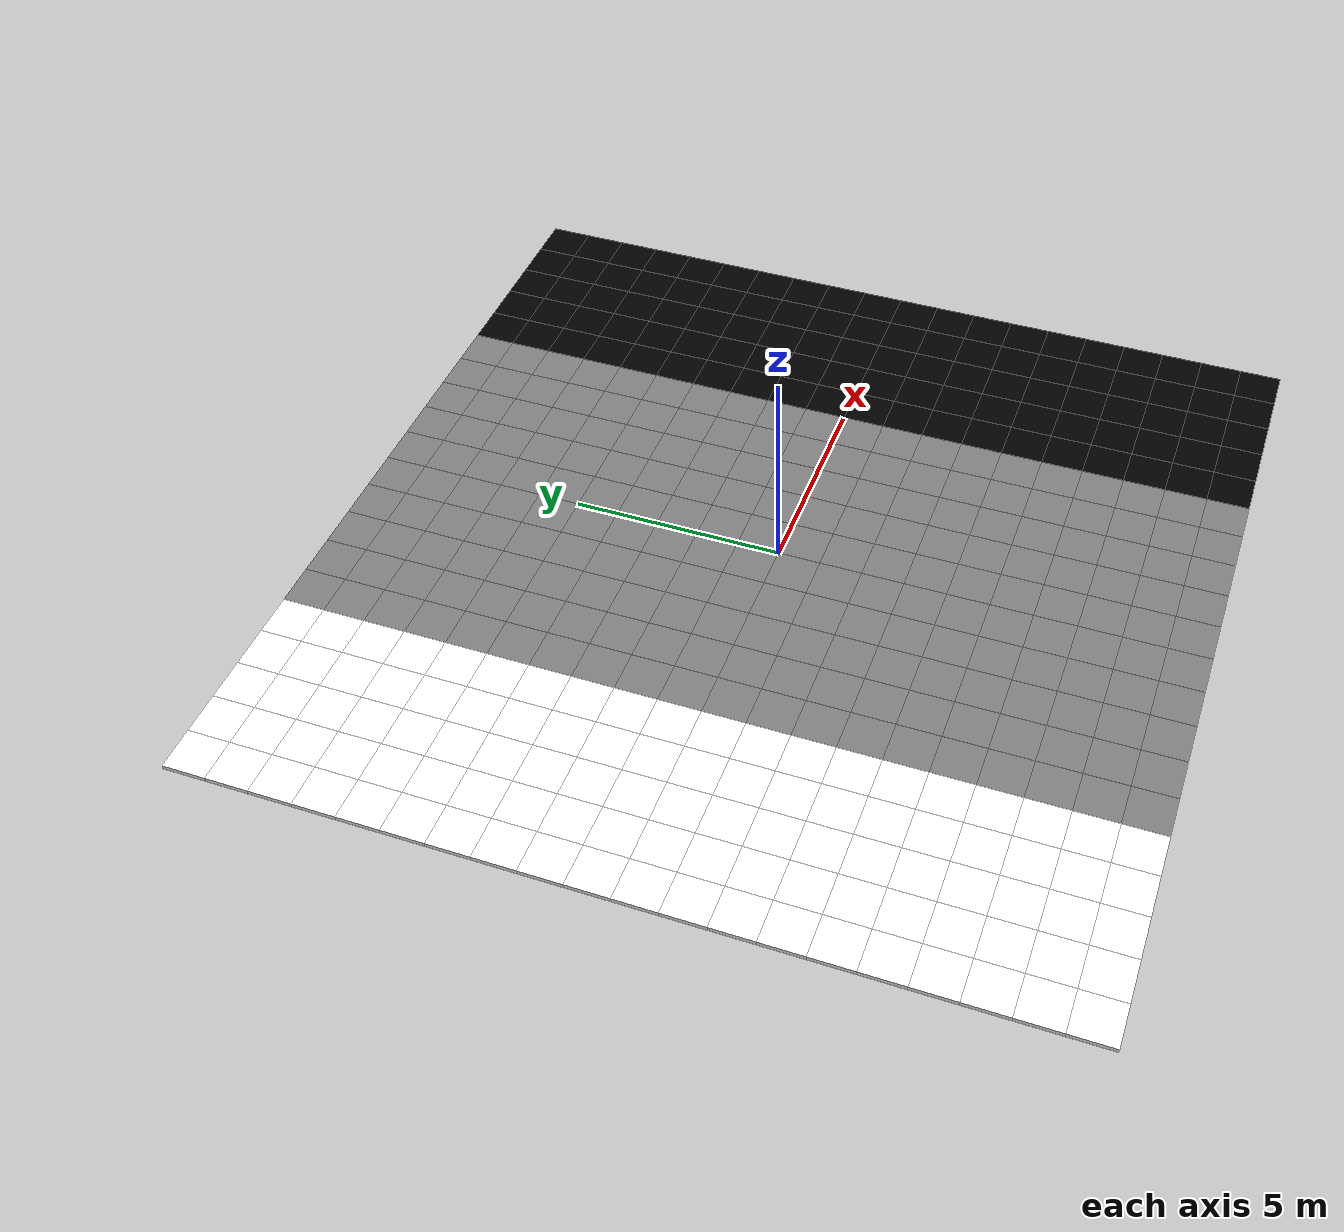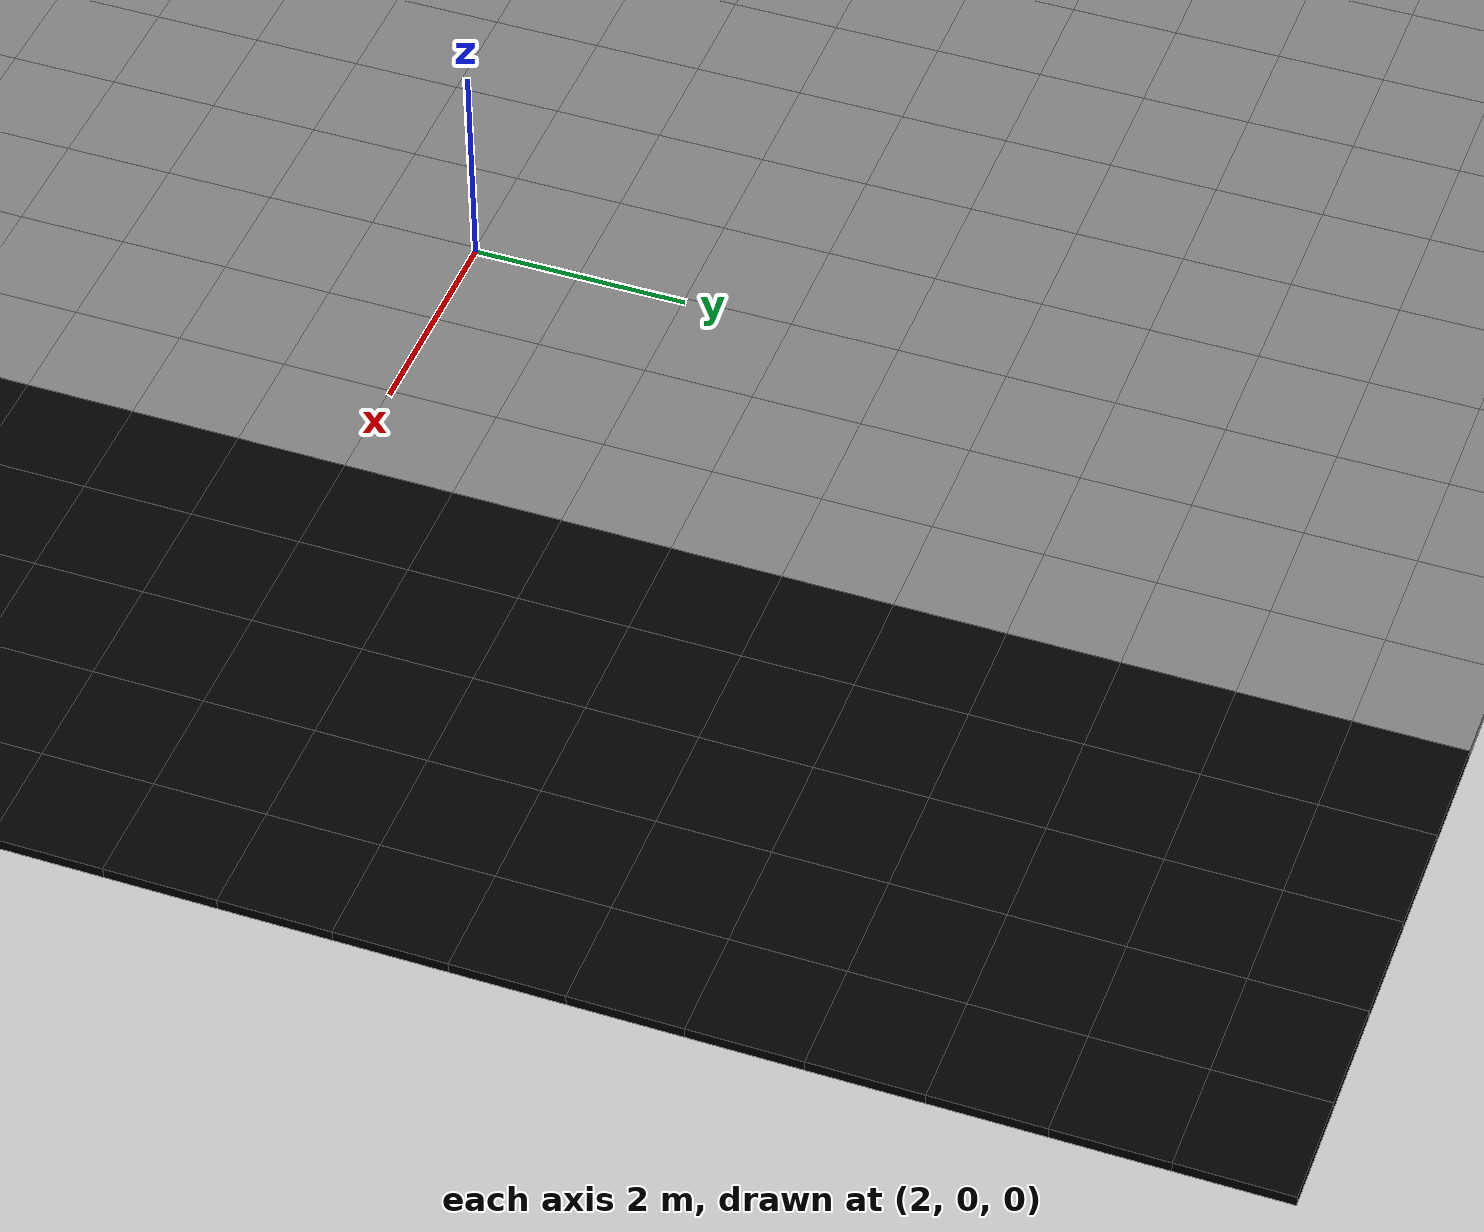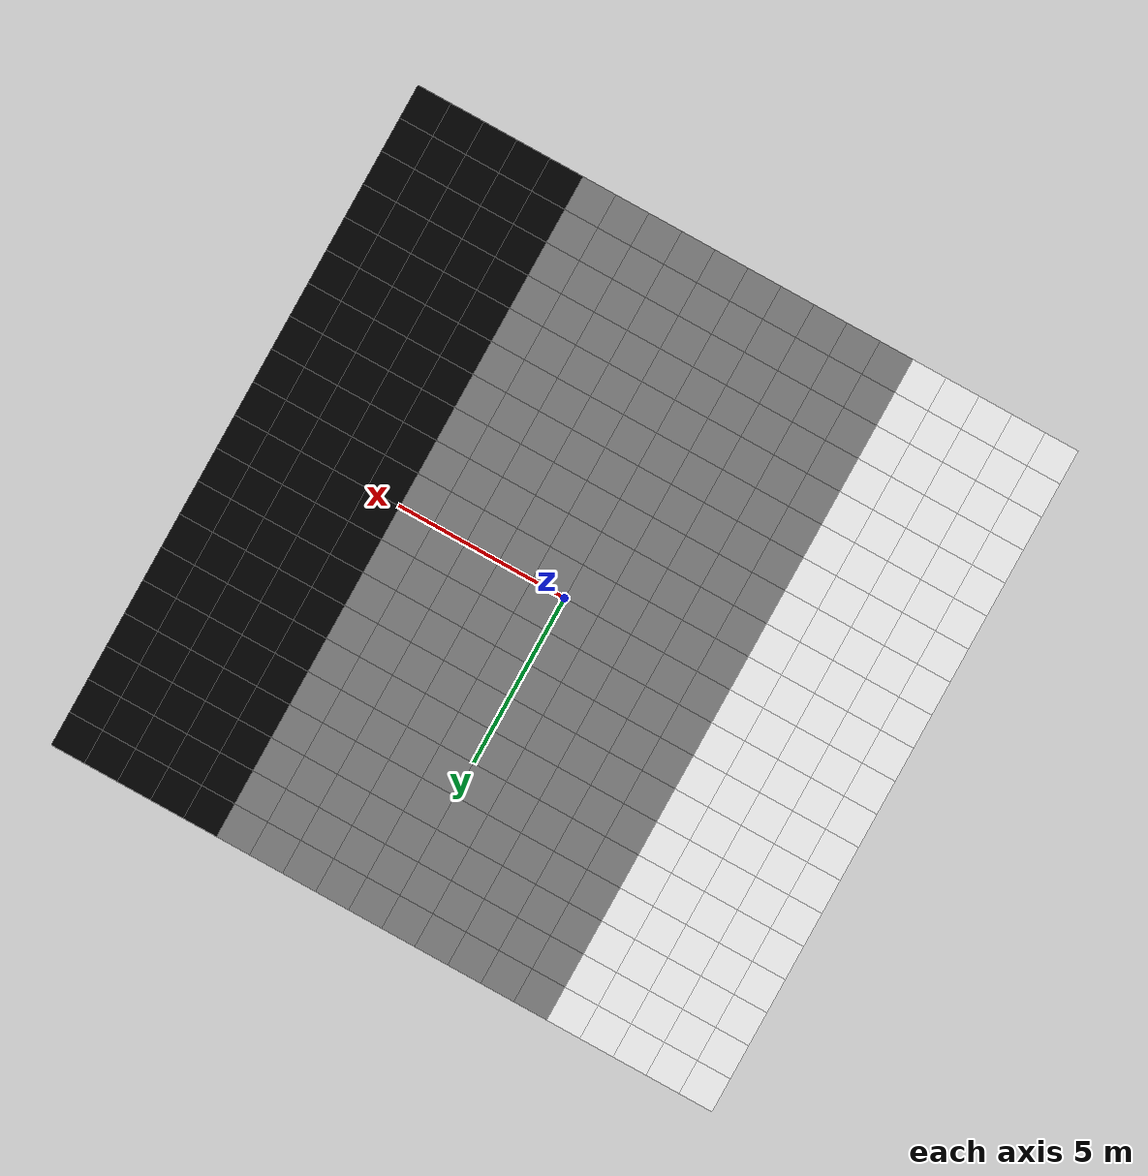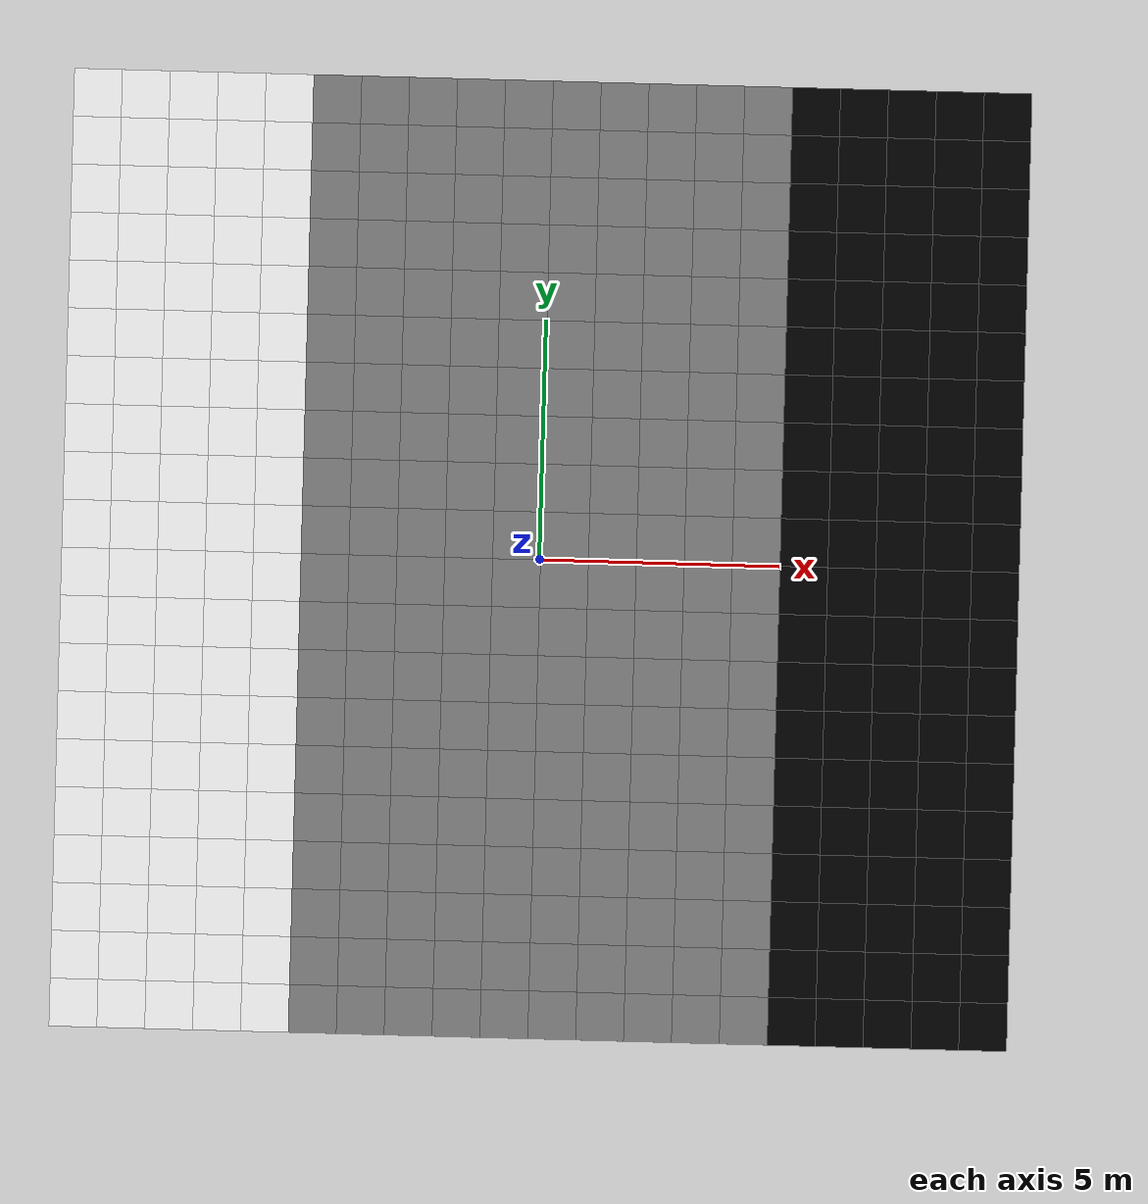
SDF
<?xml version="1.0"?>
<sdf version="1.8">
    <world name="binary_discrimination_world">
      <physics type="ode">
        <max_step_size>0.003</max_step_size>
        <real_time_factor>1.0</real_time_factor>
      </physics>
    <plugin filename="ignition-gazebo-physics-system" name="ignition::gazebo::systems::Physics"></plugin>
    <plugin filename="ignition-gazebo-user-commands-system" name="ignition::gazebo::systems::UserCommands"></plugin>
    <plugin filename="ignition-gazebo-scene-broadcaster-system" name="ignition::gazebo::systems::SceneBroadcaster"></plugin>
    <plugin filename="ignition-gazebo-contact-system" name="ignition::gazebo::systems::Contact"></plugin>
    <light type="directional" name="sun">
        <cast_shadows>true</cast_shadows>
        <pose>0 0 10 0 0 0</pose>
        <diffuse>0.8 0.8 0.8 1</diffuse>
        <specular>0.2 0.2 0.2 1</specular>
        <attenuation>
            <range>1000</range>
            <constant>0.9</constant>
            <linear>0.01</linear>
            <quadratic>0.001</quadratic>
        </attenuation>
        <direction>-0.5 0.1 -0.9</direction>
    </light>

    <model name='tile_-9.5_-9.5'>
      <static>true</static>
      <pose>-9.5 -9.5 0 0 0 0</pose>
      <link name='link'>
        <collision name='collision'>
          <geometry>
            <box>
              <size>1 1 0.1</size>
            </box>
          </geometry>
        </collision>
        <visual name='visual'>
          <geometry>
            <box>
              <size>1 1 0.1</size>
            </box>
          </geometry>
          <material>
            <ambient>1 1 1 1</ambient>
            <diffuse>1 1 1 1</diffuse>
          </material>
        </visual>
      </link>
    </model>
<model name='tile_-9.5_-8.5'>
      <static>true</static>
      <pose>-9.5 -8.5 0 0 0 0</pose>
      <link name='link'>
        <collision name='collision'>
          <geometry>
            <box>
              <size>1 1 0.1</size>
            </box>
          </geometry>
        </collision>
        <visual name='visual'>
          <geometry>
            <box>
              <size>1 1 0.1</size>
            </box>
          </geometry>
          <material>
            <ambient>1 1 1 1</ambient>
            <diffuse>1 1 1 1</diffuse>
          </material>
        </visual>
      </link>
    </model>
<model name='tile_-9.5_-7.5'>
      <static>true</static>
      <pose>-9.5 -7.5 0 0 0 0</pose>
      <link name='link'>
        <collision name='collision'>
          <geometry>
            <box>
              <size>1 1 0.1</size>
            </box>
          </geometry>
        </collision>
        <visual name='visual'>
          <geometry>
            <box>
              <size>1 1 0.1</size>
            </box>
          </geometry>
          <material>
            <ambient>1 1 1 1</ambient>
            <diffuse>1 1 1 1</diffuse>
          </material>
        </visual>
      </link>
    </model>
<model name='tile_-9.5_-6.5'>
      <static>true</static>
      <pose>-9.5 -6.5 0 0 0 0</pose>
      <link name='link'>
        <collision name='collision'>
          <geometry>
            <box>
              <size>1 1 0.1</size>
            </box>
          </geometry>
        </collision>
        <visual name='visual'>
          <geometry>
            <box>
              <size>1 1 0.1</size>
            </box>
          </geometry>
          <material>
            <ambient>1 1 1 1</ambient>
            <diffuse>1 1 1 1</diffuse>
          </material>
        </visual>
      </link>
    </model>
<model name='tile_-9.5_-5.5'>
      <static>true</static>
      <pose>-9.5 -5.5 0 0 0 0</pose>
      <link name='link'>
        <collision name='collision'>
          <geometry>
            <box>
              <size>1 1 0.1</size>
            </box>
          </geometry>
        </collision>
        <visual name='visual'>
          <geometry>
            <box>
              <size>1 1 0.1</size>
            </box>
          </geometry>
          <material>
            <ambient>1 1 1 1</ambient>
            <diffuse>1 1 1 1</diffuse>
          </material>
        </visual>
      </link>
    </model>
<model name='tile_-9.5_-4.5'>
      <static>true</static>
      <pose>-9.5 -4.5 0 0 0 0</pose>
      <link name='link'>
        <collision name='collision'>
          <geometry>
            <box>
              <size>1 1 0.1</size>
            </box>
          </geometry>
        </collision>
        <visual name='visual'>
          <geometry>
            <box>
              <size>1 1 0.1</size>
            </box>
          </geometry>
          <material>
            <ambient>1 1 1 1</ambient>
            <diffuse>1 1 1 1</diffuse>
          </material>
        </visual>
      </link>
    </model>
<model name='tile_-9.5_-3.5'>
      <static>true</static>
      <pose>-9.5 -3.5 0 0 0 0</pose>
      <link name='link'>
        <collision name='collision'>
          <geometry>
            <box>
              <size>1 1 0.1</size>
            </box>
          </geometry>
        </collision>
        <visual name='visual'>
          <geometry>
            <box>
              <size>1 1 0.1</size>
            </box>
          </geometry>
          <material>
            <ambient>1 1 1 1</ambient>
            <diffuse>1 1 1 1</diffuse>
          </material>
        </visual>
      </link>
    </model>
<model name='tile_-9.5_-2.5'>
      <static>true</static>
      <pose>-9.5 -2.5 0 0 0 0</pose>
      <link name='link'>
        <collision name='collision'>
          <geometry>
            <box>
              <size>1 1 0.1</size>
            </box>
          </geometry>
        </collision>
        <visual name='visual'>
          <geometry>
            <box>
              <size>1 1 0.1</size>
            </box>
          </geometry>
          <material>
            <ambient>1 1 1 1</ambient>
            <diffuse>1 1 1 1</diffuse>
          </material>
        </visual>
      </link>
    </model>
<model name='tile_-9.5_-1.5'>
      <static>true</static>
      <pose>-9.5 -1.5 0 0 0 0</pose>
      <link name='link'>
        <collision name='collision'>
          <geometry>
            <box>
              <size>1 1 0.1</size>
            </box>
          </geometry>
        </collision>
        <visual name='visual'>
          <geometry>
            <box>
              <size>1 1 0.1</size>
            </box>
          </geometry>
          <material>
            <ambient>1 1 1 1</ambient>
            <diffuse>1 1 1 1</diffuse>
          </material>
        </visual>
      </link>
    </model>
<model name='tile_-9.5_-0.5'>
      <static>true</static>
      <pose>-9.5 -0.5 0 0 0 0</pose>
      <link name='link'>
        <collision name='collision'>
          <geometry>
            <box>
              <size>1 1 0.1</size>
            </box>
          </geometry>
        </collision>
        <visual name='visual'>
          <geometry>
            <box>
              <size>1 1 0.1</size>
            </box>
          </geometry>
          <material>
            <ambient>1 1 1 1</ambient>
            <diffuse>1 1 1 1</diffuse>
          </material>
        </visual>
      </link>
    </model>
<model name='tile_-9.5_0.5'>
      <static>true</static>
      <pose>-9.5 0.5 0 0 0 0</pose>
      <link name='link'>
        <collision name='collision'>
          <geometry>
            <box>
              <size>1 1 0.1</size>
            </box>
          </geometry>
        </collision>
        <visual name='visual'>
          <geometry>
            <box>
              <size>1 1 0.1</size>
            </box>
          </geometry>
          <material>
            <ambient>1 1 1 1</ambient>
            <diffuse>1 1 1 1</diffuse>
          </material>
        </visual>
      </link>
    </model>
<model name='tile_-9.5_1.5'>
      <static>true</static>
      <pose>-9.5 1.5 0 0 0 0</pose>
      <link name='link'>
        <collision name='collision'>
          <geometry>
            <box>
              <size>1 1 0.1</size>
            </box>
          </geometry>
        </collision>
        <visual name='visual'>
          <geometry>
            <box>
              <size>1 1 0.1</size>
            </box>
          </geometry>
          <material>
            <ambient>1 1 1 1</ambient>
            <diffuse>1 1 1 1</diffuse>
          </material>
        </visual>
      </link>
    </model>
<model name='tile_-9.5_2.5'>
      <static>true</static>
      <pose>-9.5 2.5 0 0 0 0</pose>
      <link name='link'>
        <collision name='collision'>
          <geometry>
            <box>
              <size>1 1 0.1</size>
            </box>
          </geometry>
        </collision>
        <visual name='visual'>
          <geometry>
            <box>
              <size>1 1 0.1</size>
            </box>
          </geometry>
          <material>
            <ambient>1 1 1 1</ambient>
            <diffuse>1 1 1 1</diffuse>
          </material>
        </visual>
      </link>
    </model>
<model name='tile_-9.5_3.5'>
      <static>true</static>
      <pose>-9.5 3.5 0 0 0 0</pose>
      <link name='link'>
        <collision name='collision'>
          <geometry>
            <box>
              <size>1 1 0.1</size>
            </box>
          </geometry>
        </collision>
        <visual name='visual'>
          <geometry>
            <box>
              <size>1 1 0.1</size>
            </box>
          </geometry>
          <material>
            <ambient>1 1 1 1</ambient>
            <diffuse>1 1 1 1</diffuse>
          </material>
        </visual>
      </link>
    </model>
<model name='tile_-9.5_4.5'>
      <static>true</static>
      <pose>-9.5 4.5 0 0 0 0</pose>
      <link name='link'>
        <collision name='collision'>
          <geometry>
            <box>
              <size>1 1 0.1</size>
            </box>
          </geometry>
        </collision>
        <visual name='visual'>
          <geometry>
            <box>
              <size>1 1 0.1</size>
            </box>
          </geometry>
          <material>
            <ambient>1 1 1 1</ambient>
            <diffuse>1 1 1 1</diffuse>
          </material>
        </visual>
      </link>
    </model>
<model name='tile_-9.5_5.5'>
      <static>true</static>
      <pose>-9.5 5.5 0 0 0 0</pose>
      <link name='link'>
        <collision name='collision'>
          <geometry>
            <box>
              <size>1 1 0.1</size>
            </box>
          </geometry>
        </collision>
        <visual name='visual'>
          <geometry>
            <box>
              <size>1 1 0.1</size>
            </box>
          </geometry>
          <material>
            <ambient>1 1 1 1</ambient>
            <diffuse>1 1 1 1</diffuse>
          </material>
        </visual>
      </link>
    </model>
<model name='tile_-9.5_6.5'>
      <static>true</static>
      <pose>-9.5 6.5 0 0 0 0</pose>
      <link name='link'>
        <collision name='collision'>
          <geometry>
            <box>
              <size>1 1 0.1</size>
            </box>
          </geometry>
        </collision>
        <visual name='visual'>
          <geometry>
            <box>
              <size>1 1 0.1</size>
            </box>
          </geometry>
          <material>
            <ambient>1 1 1 1</ambient>
            <diffuse>1 1 1 1</diffuse>
          </material>
        </visual>
      </link>
    </model>
<model name='tile_-9.5_7.5'>
      <static>true</static>
      <pose>-9.5 7.5 0 0 0 0</pose>
      <link name='link'>
        <collision name='collision'>
          <geometry>
            <box>
              <size>1 1 0.1</size>
            </box>
          </geometry>
        </collision>
        <visual name='visual'>
          <geometry>
            <box>
              <size>1 1 0.1</size>
            </box>
          </geometry>
          <material>
            <ambient>1 1 1 1</ambient>
            <diffuse>1 1 1 1</diffuse>
          </material>
        </visual>
      </link>
    </model>
<model name='tile_-9.5_8.5'>
      <static>true</static>
      <pose>-9.5 8.5 0 0 0 0</pose>
      <link name='link'>
        <collision name='collision'>
          <geometry>
            <box>
              <size>1 1 0.1</size>
            </box>
          </geometry>
        </collision>
        <visual name='visual'>
          <geometry>
            <box>
              <size>1 1 0.1</size>
            </box>
          </geometry>
          <material>
            <ambient>1 1 1 1</ambient>
            <diffuse>1 1 1 1</diffuse>
          </material>
        </visual>
      </link>
    </model>
<model name='tile_-9.5_9.5'>
      <static>true</static>
      <pose>-9.5 9.5 0 0 0 0</pose>
      <link name='link'>
        <collision name='collision'>
          <geometry>
            <box>
              <size>1 1 0.1</size>
            </box>
          </geometry>
        </collision>
        <visual name='visual'>
          <geometry>
            <box>
              <size>1 1 0.1</size>
            </box>
          </geometry>
          <material>
            <ambient>1 1 1 1</ambient>
            <diffuse>1 1 1 1</diffuse>
          </material>
        </visual>
      </link>
    </model>
<model name='tile_-8.5_-9.5'>
      <static>true</static>
      <pose>-8.5 -9.5 0 0 0 0</pose>
      <link name='link'>
        <collision name='collision'>
          <geometry>
            <box>
              <size>1 1 0.1</size>
            </box>
          </geometry>
        </collision>
        <visual name='visual'>
          <geometry>
            <box>
              <size>1 1 0.1</size>
            </box>
          </geometry>
          <material>
            <ambient>1 1 1 1</ambient>
            <diffuse>1 1 1 1</diffuse>
          </material>
        </visual>
      </link>
    </model>
<model name='tile_-8.5_-8.5'>
      <static>true</static>
      <pose>-8.5 -8.5 0 0 0 0</pose>
      <link name='link'>
        <collision name='collision'>
          <geometry>
            <box>
              <size>1 1 0.1</size>
            </box>
          </geometry>
        </collision>
        <visual name='visual'>
          <geometry>
            <box>
              <size>1 1 0.1</size>
            </box>
          </geometry>
          <material>
            <ambient>1 1 1 1</ambient>
            <diffuse>1 1 1 1</diffuse>
          </material>
        </visual>
      </link>
    </model>
<model name='tile_-8.5_-7.5'>
      <static>true</static>
      <pose>-8.5 -7.5 0 0 0 0</pose>
      <link name='link'>
        <collision name='collision'>
          <geometry>
            <box>
              <size>1 1 0.1</size>
            </box>
          </geometry>
        </collision>
        <visual name='visual'>
          <geometry>
            <box>
              <size>1 1 0.1</size>
            </box>
          </geometry>
          <material>
            <ambient>1 1 1 1</ambient>
            <diffuse>1 1 1 1</diffuse>
          </material>
        </visual>
      </link>
    </model>
<model name='tile_-8.5_-6.5'>
      <static>true</static>
      <pose>-8.5 -6.5 0 0 0 0</pose>
      <link name='link'>
        <collision name='collision'>
          <geometry>
            <box>
              <size>1 1 0.1</size>
            </box>
          </geometry>
        </collision>
        <visual name='visual'>
          <geometry>
            <box>
              <size>1 1 0.1</size>
            </box>
          </geometry>
          <material>
            <ambient>1 1 1 1</ambient>
            <diffuse>1 1 1 1</diffuse>
          </material>
        </visual>
      </link>
    </model>
<model name='tile_-8.5_-5.5'>
      <static>true</static>
      <pose>-8.5 -5.5 0 0 0 0</pose>
      <link name='link'>
        <collision name='collision'>
          <geometry>
            <box>
              <size>1 1 0.1</size>
            </box>
          </geometry>
        </collision>
        <visual name='visual'>
          <geometry>
            <box>
              <size>1 1 0.1</size>
            </box>
          </geometry>
          <material>
            <ambient>1 1 1 1</ambient>
            <diffuse>1 1 1 1</diffuse>
          </material>
        </visual>
      </link>
    </model>
<model name='tile_-8.5_-4.5'>
      <static>true</static>
      <pose>-8.5 -4.5 0 0 0 0</pose>
      <link name='link'>
        <collision name='collision'>
          <geometry>
            <box>
              <size>1 1 0.1</size>
            </box>
          </geometry>
        </collision>
        <visual name='visual'>
          <geometry>
            <box>
              <size>1 1 0.1</size>
            </box>
          </geometry>
          <material>
            <ambient>1 1 1 1</ambient>
            <diffuse>1 1 1 1</diffuse>
          </material>
        </visual>
      </link>
    </model>
<model name='tile_-8.5_-3.5'>
      <static>true</static>
      <pose>-8.5 -3.5 0 0 0 0</pose>
      <link name='link'>
        <collision name='collision'>
          <geometry>
            <box>
              <size>1 1 0.1</size>
            </box>
          </geometry>
        </collision>
        <visual name='visual'>
          <geometry>
            <box>
              <size>1 1 0.1</size>
            </box>
          </geometry>
          <material>
            <ambient>1 1 1 1</ambient>
            <diffuse>1 1 1 1</diffuse>
          </material>
        </visual>
      </link>
    </model>
<model name='tile_-8.5_-2.5'>
      <static>true</static>
      <pose>-8.5 -2.5 0 0 0 0</pose>
      <link name='link'>
        <collision name='collision'>
          <geometry>
            <box>
              <size>1 1 0.1</size>
            </box>
          </geometry>
        </collision>
        <visual name='visual'>
          <geometry>
            <box>
              <size>1 1 0.1</size>
            </box>
          </geometry>
          <material>
            <ambient>1 1 1 1</ambient>
            <diffuse>1 1 1 1</diffuse>
          </material>
        </visual>
      </link>
    </model>
<model name='tile_-8.5_-1.5'>
      <static>true</static>
      <pose>-8.5 -1.5 0 0 0 0</pose>
      <link name='link'>
        <collision name='collision'>
          <geometry>
            <box>
              <size>1 1 0.1</size>
            </box>
          </geometry>
        </collision>
        <visual name='visual'>
          <geometry>
            <box>
              <size>1 1 0.1</size>
            </box>
          </geometry>
          <material>
            <ambient>1 1 1 1</ambient>
            <diffuse>1 1 1 1</diffuse>
          </material>
        </visual>
      </link>
    </model>
<model name='tile_-8.5_-0.5'>
      <static>true</static>
      <pose>-8.5 -0.5 0 0 0 0</pose>
      <link name='link'>
        <collision name='collision'>
          <geometry>
            <box>
              <size>1 1 0.1</size>
            </box>
          </geometry>
        </collision>
        <visual name='visual'>
          <geometry>
            <box>
              <size>1 1 0.1</size>
            </box>
          </geometry>
          <material>
            <ambient>1 1 1 1</ambient>
            <diffuse>1 1 1 1</diffuse>
          </material>
        </visual>
      </link>
    </model>
<model name='tile_-8.5_0.5'>
      <static>true</static>
      <pose>-8.5 0.5 0 0 0 0</pose>
      <link name='link'>
        <collision name='collision'>
          <geometry>
            <box>
              <size>1 1 0.1</size>
            </box>
          </geometry>
        </collision>
        <visual name='visual'>
          <geometry>
            <box>
              <size>1 1 0.1</size>
            </box>
          </geometry>
          <material>
            <ambient>1 1 1 1</ambient>
            <diffuse>1 1 1 1</diffuse>
          </material>
        </visual>
      </link>
    </model>
<model name='tile_-8.5_1.5'>
      <static>true</static>
      <pose>-8.5 1.5 0 0 0 0</pose>
      <link name='link'>
        <collision name='collision'>
          <geometry>
            <box>
              <size>1 1 0.1</size>
            </box>
          </geometry>
        </collision>
        <visual name='visual'>
          <geometry>
            <box>
              <size>1 1 0.1</size>
            </box>
          </geometry>
          <material>
            <ambient>1 1 1 1</ambient>
            <diffuse>1 1 1 1</diffuse>
          </material>
        </visual>
      </link>
    </model>
<model name='tile_-8.5_2.5'>
      <static>true</static>
      <pose>-8.5 2.5 0 0 0 0</pose>
      <link name='link'>
        <collision name='collision'>
          <geometry>
            <box>
              <size>1 1 0.1</size>
            </box>
          </geometry>
        </collision>
        <visual name='visual'>
          <geometry>
            <box>
              <size>1 1 0.1</size>
            </box>
          </geometry>
          <material>
            <ambient>1 1 1 1</ambient>
            <diffuse>1 1 1 1</diffuse>
          </material>
        </visual>
      </link>
    </model>
<model name='tile_-8.5_3.5'>
      <static>true</static>
      <pose>-8.5 3.5 0 0 0 0</pose>
      <link name='link'>
        <collision name='collision'>
          <geometry>
            <box>
              <size>1 1 0.1</size>
            </box>
          </geometry>
        </collision>
        <visual name='visual'>
          <geometry>
            <box>
              <size>1 1 0.1</size>
            </box>
          </geometry>
          <material>
            <ambient>1 1 1 1</ambient>
            <diffuse>1 1 1 1</diffuse>
          </material>
        </visual>
      </link>
    </model>
<model name='tile_-8.5_4.5'>
      <static>true</static>
      <pose>-8.5 4.5 0 0 0 0</pose>
      <link name='link'>
        <collision name='collision'>
          <geometry>
            <box>
              <size>1 1 0.1</size>
            </box>
          </geometry>
        </collision>
        <visual name='visual'>
          <geometry>
            <box>
              <size>1 1 0.1</size>
            </box>
          </geometry>
          <material>
            <ambient>1 1 1 1</ambient>
            <diffuse>1 1 1 1</diffuse>
          </material>
        </visual>
      </link>
    </model>
<model name='tile_-8.5_5.5'>
      <static>true</static>
      <pose>-8.5 5.5 0 0 0 0</pose>
      <link name='link'>
        <collision name='collision'>
          <geometry>
            <box>
              <size>1 1 0.1</size>
            </box>
          </geometry>
        </collision>
        <visual name='visual'>
          <geometry>
            <box>
              <size>1 1 0.1</size>
            </box>
          </geometry>
          <material>
            <ambient>1 1 1 1</ambient>
            <diffuse>1 1 1 1</diffuse>
          </material>
        </visual>
      </link>
    </model>
<model name='tile_-8.5_6.5'>
      <static>true</static>
      <pose>-8.5 6.5 0 0 0 0</pose>
      <link name='link'>
        <collision name='collision'>
          <geometry>
            <box>
              <size>1 1 0.1</size>
            </box>
          </geometry>
        </collision>
        <visual name='visual'>
          <geometry>
            <box>
              <size>1 1 0.1</size>
            </box>
          </geometry>
          <material>
            <ambient>1 1 1 1</ambient>
            <diffuse>1 1 1 1</diffuse>
          </material>
        </visual>
      </link>
    </model>
<model name='tile_-8.5_7.5'>
      <static>true</static>
      <pose>-8.5 7.5 0 0 0 0</pose>
      <link name='link'>
        <collision name='collision'>
          <geometry>
            <box>
              <size>1 1 0.1</size>
            </box>
          </geometry>
        </collision>
        <visual name='visual'>
          <geometry>
            <box>
              <size>1 1 0.1</size>
            </box>
          </geometry>
          <material>
            <ambient>1 1 1 1</ambient>
            <diffuse>1 1 1 1</diffuse>
          </material>
        </visual>
      </link>
    </model>
<model name='tile_-8.5_8.5'>
      <static>true</static>
      <pose>-8.5 8.5 0 0 0 0</pose>
      <link name='link'>
        <collision name='collision'>
          <geometry>
            <box>
              <size>1 1 0.1</size>
            </box>
          </geometry>
        </collision>
        <visual name='visual'>
          <geometry>
            <box>
              <size>1 1 0.1</size>
            </box>
          </geometry>
          <material>
            <ambient>1 1 1 1</ambient>
            <diffuse>1 1 1 1</diffuse>
          </material>
        </visual>
      </link>
    </model>
<model name='tile_-8.5_9.5'>
      <static>true</static>
      <pose>-8.5 9.5 0 0 0 0</pose>
      <link name='link'>
        <collision name='collision'>
          <geometry>
            <box>
              <size>1 1 0.1</size>
            </box>
          </geometry>
        </collision>
        <visual name='visual'>
          <geometry>
            <box>
              <size>1 1 0.1</size>
            </box>
          </geometry>
          <material>
            <ambient>1 1 1 1</ambient>
            <diffuse>1 1 1 1</diffuse>
          </material>
        </visual>
      </link>
    </model>
<model name='tile_-7.5_-9.5'>
      <static>true</static>
      <pose>-7.5 -9.5 0 0 0 0</pose>
      <link name='link'>
        <collision name='collision'>
          <geometry>
            <box>
              <size>1 1 0.1</size>
            </box>
          </geometry>
        </collision>
        <visual name='visual'>
          <geometry>
            <box>
              <size>1 1 0.1</size>
            </box>
          </geometry>
          <material>
            <ambient>1 1 1 1</ambient>
            <diffuse>1 1 1 1</diffuse>
          </material>
        </visual>
      </link>
    </model>
<model name='tile_-7.5_-8.5'>
      <static>true</static>
      <pose>-7.5 -8.5 0 0 0 0</pose>
      <link name='link'>
        <collision name='collision'>
          <geometry>
            <box>
              <size>1 1 0.1</size>
            </box>
          </geometry>
        </collision>
        <visual name='visual'>
          <geometry>
            <box>
              <size>1 1 0.1</size>
            </box>
          </geometry>
          <material>
            <ambient>1 1 1 1</ambient>
            <diffuse>1 1 1 1</diffuse>
          </material>
        </visual>
      </link>
    </model>
<model name='tile_-7.5_-7.5'>
      <static>true</static>
      <pose>-7.5 -7.5 0 0 0 0</pose>
      <link name='link'>
        <collision name='collision'>
          <geometry>
            <box>
              <size>1 1 0.1</size>
            </box>
          </geometry>
        </collision>
        <visual name='visual'>
          <geometry>
            <box>
              <size>1 1 0.1</size>
            </box>
          </geometry>
          <material>
            <ambient>1 1 1 1</ambient>
            <diffuse>1 1 1 1</diffuse>
          </material>
        </visual>
      </link>
    </model>
<model name='tile_-7.5_-6.5'>
      <static>true</static>
      <pose>-7.5 -6.5 0 0 0 0</pose>
      <link name='link'>
        <collision name='collision'>
          <geometry>
            <box>
              <size>1 1 0.1</size>
            </box>
          </geometry>
        </collision>
        <visual name='visual'>
          <geometry>
            <box>
              <size>1 1 0.1</size>
            </box>
          </geometry>
          <material>
            <ambient>1 1 1 1</ambient>
            <diffuse>1 1 1 1</diffuse>
          </material>
        </visual>
      </link>
    </model>
<model name='tile_-7.5_-5.5'>
      <static>true</static>
      <pose>-7.5 -5.5 0 0 0 0</pose>
      <link name='link'>
        <collision name='collision'>
          <geometry>
            <box>
              <size>1 1 0.1</size>
            </box>
          </geometry>
        </collision>
        <visual name='visual'>
          <geometry>
            <box>
              <size>1 1 0.1</size>
            </box>
          </geometry>
          <material>
            <ambient>1 1 1 1</ambient>
            <diffuse>1 1 1 1</diffuse>
          </material>
        </visual>
      </link>
    </model>
<model name='tile_-7.5_-4.5'>
      <static>true</static>
      <pose>-7.5 -4.5 0 0 0 0</pose>
      <link name='link'>
        <collision name='collision'>
          <geometry>
            <box>
              <size>1 1 0.1</size>
            </box>
          </geometry>
        </collision>
        <visual name='visual'>
          <geometry>
            <box>
              <size>1 1 0.1</size>
            </box>
          </geometry>
          <material>
            <ambient>1 1 1 1</ambient>
            <diffuse>1 1 1 1</diffuse>
          </material>
        </visual>
      </link>
    </model>
<model name='tile_-7.5_-3.5'>
      <static>true</static>
      <pose>-7.5 -3.5 0 0 0 0</pose>
      <link name='link'>
        <collision name='collision'>
          <geometry>
            <box>
              <size>1 1 0.1</size>
            </box>
          </geometry>
        </collision>
        <visual name='visual'>
          <geometry>
            <box>
              <size>1 1 0.1</size>
            </box>
          </geometry>
          <material>
            <ambient>1 1 1 1</ambient>
            <diffuse>1 1 1 1</diffuse>
          </material>
        </visual>
      </link>
    </model>
<model name='tile_-7.5_-2.5'>
      <static>true</static>
      <pose>-7.5 -2.5 0 0 0 0</pose>
      <link name='link'>
        <collision name='collision'>
          <geometry>
            <box>
              <size>1 1 0.1</size>
            </box>
          </geometry>
        </collision>
        <visual name='visual'>
          <geometry>
            <box>
              <size>1 1 0.1</size>
            </box>
          </geometry>
          <material>
            <ambient>1 1 1 1</ambient>
            <diffuse>1 1 1 1</diffuse>
          </material>
        </visual>
      </link>
    </model>
<model name='tile_-7.5_-1.5'>
      <static>true</static>
      <pose>-7.5 -1.5 0 0 0 0</pose>
      <link name='link'>
        <collision name='collision'>
          <geometry>
            <box>
              <size>1 1 0.1</size>
            </box>
          </geometry>
        </collision>
        <visual name='visual'>
          <geometry>
            <box>
              <size>1 1 0.1</size>
            </box>
          </geometry>
          <material>
            <ambient>1 1 1 1</ambient>
            <diffuse>1 1 1 1</diffuse>
          </material>
        </visual>
      </link>
    </model>
<model name='tile_-7.5_-0.5'>
      <static>true</static>
      <pose>-7.5 -0.5 0 0 0 0</pose>
      <link name='link'>
        <collision name='collision'>
          <geometry>
            <box>
              <size>1 1 0.1</size>
            </box>
          </geometry>
        </collision>
        <visual name='visual'>
          <geometry>
            <box>
              <size>1 1 0.1</size>
            </box>
          </geometry>
          <material>
            <ambient>1 1 1 1</ambient>
            <diffuse>1 1 1 1</diffuse>
          </material>
        </visual>
      </link>
    </model>
<model name='tile_-7.5_0.5'>
      <static>true</static>
      <pose>-7.5 0.5 0 0 0 0</pose>
      <link name='link'>
        <collision name='collision'>
          <geometry>
            <box>
              <size>1 1 0.1</size>
            </box>
          </geometry>
        </collision>
        <visual name='visual'>
          <geometry>
            <box>
              <size>1 1 0.1</size>
            </box>
          </geometry>
          <material>
            <ambient>1 1 1 1</ambient>
            <diffuse>1 1 1 1</diffuse>
          </material>
        </visual>
      </link>
    </model>
<model name='tile_-7.5_1.5'>
      <static>true</static>
      <pose>-7.5 1.5 0 0 0 0</pose>
      <link name='link'>
        <collision name='collision'>
          <geometry>
            <box>
              <size>1 1 0.1</size>
            </box>
          </geometry>
        </collision>
        <visual name='visual'>
          <geometry>
            <box>
              <size>1 1 0.1</size>
            </box>
          </geometry>
          <material>
            <ambient>1 1 1 1</ambient>
            <diffuse>1 1 1 1</diffuse>
          </material>
        </visual>
      </link>
    </model>
<model name='tile_-7.5_2.5'>
      <static>true</static>
      <pose>-7.5 2.5 0 0 0 0</pose>
      <link name='link'>
        <collision name='collision'>
          <geometry>
            <box>
              <size>1 1 0.1</size>
            </box>
          </geometry>
        </collision>
        <visual name='visual'>
          <geometry>
            <box>
              <size>1 1 0.1</size>
            </box>
          </geometry>
          <material>
            <ambient>1 1 1 1</ambient>
            <diffuse>1 1 1 1</diffuse>
          </material>
        </visual>
      </link>
    </model>
<model name='tile_-7.5_3.5'>
      <static>true</static>
      <pose>-7.5 3.5 0 0 0 0</pose>
      <link name='link'>
        <collision name='collision'>
          <geometry>
            <box>
              <size>1 1 0.1</size>
            </box>
          </geometry>
        </collision>
        <visual name='visual'>
          <geometry>
            <box>
              <size>1 1 0.1</size>
            </box>
          </geometry>
          <material>
            <ambient>1 1 1 1</ambient>
            <diffuse>1 1 1 1</diffuse>
          </material>
        </visual>
      </link>
    </model>
<model name='tile_-7.5_4.5'>
      <static>true</static>
      <pose>-7.5 4.5 0 0 0 0</pose>
      <link name='link'>
        <collision name='collision'>
          <geometry>
            <box>
              <size>1 1 0.1</size>
            </box>
          </geometry>
        </collision>
        <visual name='visual'>
          <geometry>
            <box>
              <size>1 1 0.1</size>
            </box>
          </geometry>
          <material>
            <ambient>1 1 1 1</ambient>
            <diffuse>1 1 1 1</diffuse>
          </material>
        </visual>
      </link>
    </model>
<model name='tile_-7.5_5.5'>
      <static>true</static>
      <pose>-7.5 5.5 0 0 0 0</pose>
      <link name='link'>
        <collision name='collision'>
          <geometry>
            <box>
              <size>1 1 0.1</size>
            </box>
          </geometry>
        </collision>
        <visual name='visual'>
          <geometry>
            <box>
              <size>1 1 0.1</size>
            </box>
          </geometry>
          <material>
            <ambient>1 1 1 1</ambient>
            <diffuse>1 1 1 1</diffuse>
          </material>
        </visual>
      </link>
    </model>
<model name='tile_-7.5_6.5'>
      <static>true</static>
      <pose>-7.5 6.5 0 0 0 0</pose>
      <link name='link'>
        <collision name='collision'>
          <geometry>
            <box>
              <size>1 1 0.1</size>
            </box>
          </geometry>
        </collision>
        <visual name='visual'>
          <geometry>
            <box>
              <size>1 1 0.1</size>
            </box>
          </geometry>
          <material>
            <ambient>1 1 1 1</ambient>
            <diffuse>1 1 1 1</diffuse>
          </material>
        </visual>
      </link>
    </model>
<model name='tile_-7.5_7.5'>
      <static>true</static>
      <pose>-7.5 7.5 0 0 0 0</pose>
      <link name='link'>
        <collision name='collision'>
          <geometry>
            <box>
              <size>1 1 0.1</size>
            </box>
          </geometry>
        </collision>
        <visual name='visual'>
          <geometry>
            <box>
              <size>1 1 0.1</size>
            </box>
          </geometry>
          <material>
            <ambient>1 1 1 1</ambient>
            <diffuse>1 1 1 1</diffuse>
          </material>
        </visual>
      </link>
    </model>
<model name='tile_-7.5_8.5'>
      <static>true</static>
      <pose>-7.5 8.5 0 0 0 0</pose>
      <link name='link'>
        <collision name='collision'>
          <geometry>
            <box>
              <size>1 1 0.1</size>
            </box>
          </geometry>
        </collision>
        <visual name='visual'>
          <geometry>
            <box>
              <size>1 1 0.1</size>
            </box>
          </geometry>
          <material>
            <ambient>1 1 1 1</ambient>
            <diffuse>1 1 1 1</diffuse>
          </material>
        </visual>
      </link>
    </model>
<model name='tile_-7.5_9.5'>
      <static>true</static>
      <pose>-7.5 9.5 0 0 0 0</pose>
      <link name='link'>
        <collision name='collision'>
          <geometry>
            <box>
              <size>1 1 0.1</size>
            </box>
          </geometry>
        </collision>
        <visual name='visual'>
          <geometry>
            <box>
              <size>1 1 0.1</size>
            </box>
          </geometry>
          <material>
            <ambient>1 1 1 1</ambient>
            <diffuse>1 1 1 1</diffuse>
          </material>
        </visual>
      </link>
    </model>
<model name='tile_-6.5_-9.5'>
      <static>true</static>
      <pose>-6.5 -9.5 0 0 0 0</pose>
      <link name='link'>
        <collision name='collision'>
          <geometry>
            <box>
              <size>1 1 0.1</size>
            </box>
          </geometry>
        </collision>
        <visual name='visual'>
          <geometry>
            <box>
              <size>1 1 0.1</size>
            </box>
          </geometry>
          <material>
            <ambient>1 1 1 1</ambient>
            <diffuse>1 1 1 1</diffuse>
          </material>
        </visual>
      </link>
    </model>
<model name='tile_-6.5_-8.5'>
      <static>true</static>
      <pose>-6.5 -8.5 0 0 0 0</pose>
      <link name='link'>
        <collision name='collision'>
          <geometry>
            <box>
              <size>1 1 0.1</size>
            </box>
          </geometry>
        </collision>
        <visual name='visual'>
          <geometry>
            <box>
              <size>1 1 0.1</size>
            </box>
          </geometry>
          <material>
            <ambient>1 1 1 1</ambient>
            <diffuse>1 1 1 1</diffuse>
          </material>
        </visual>
      </link>
    </model>
<model name='tile_-6.5_-7.5'>
      <static>true</static>
      <pose>-6.5 -7.5 0 0 0 0</pose>
      <link name='link'>
        <collision name='collision'>
          <geometry>
            <box>
              <size>1 1 0.1</size>
            </box>
          </geometry>
        </collision>
        <visual name='visual'>
          <geometry>
            <box>
              <size>1 1 0.1</size>
            </box>
          </geometry>
          <material>
            <ambient>1 1 1 1</ambient>
            <diffuse>1 1 1 1</diffuse>
          </material>
        </visual>
      </link>
    </model>
<model name='tile_-6.5_-6.5'>
      <static>true</static>
      <pose>-6.5 -6.5 0 0 0 0</pose>
      <link name='link'>
        <collision name='collision'>
          <geometry>
            <box>
              <size>1 1 0.1</size>
            </box>
          </geometry>
        </collision>
        <visual name='visual'>
          <geometry>
            <box>
              <size>1 1 0.1</size>
            </box>
          </geometry>
          <material>
            <ambient>1 1 1 1</ambient>
            <diffuse>1 1 1 1</diffuse>
          </material>
        </visual>
      </link>
    </model>
<model name='tile_-6.5_-5.5'>
      <static>true</static>
      <pose>-6.5 -5.5 0 0 0 0</pose>
      <link name='link'>
        <collision name='collision'>
          <geometry>
            <box>
              <size>1 1 0.1</size>
            </box>
          </geometry>
        </collision>
        <visual name='visual'>
          <geometry>
            <box>
              <size>1 1 0.1</size>
            </box>
          </geometry>
          <material>
            <ambient>1 1 1 1</ambient>
            <diffuse>1 1 1 1</diffuse>
          </material>
        </visual>
      </link>
    </model>
<model name='tile_-6.5_-4.5'>
      <static>true</static>
      <pose>-6.5 -4.5 0 0 0 0</pose>
      <link name='link'>
        <collision name='collision'>
          <geometry>
            <box>
              <size>1 1 0.1</size>
            </box>
          </geometry>
        </collision>
        <visual name='visual'>
          <geometry>
            <box>
              <size>1 1 0.1</size>
            </box>
          </geometry>
          <material>
            <ambient>1 1 1 1</ambient>
            <diffuse>1 1 1 1</diffuse>
          </material>
        </visual>
      </link>
    </model>
<model name='tile_-6.5_-3.5'>
      <static>true</static>
      <pose>-6.5 -3.5 0 0 0 0</pose>
      <link name='link'>
        <collision name='collision'>
          <geometry>
            <box>
              <size>1 1 0.1</size>
            </box>
          </geometry>
        </collision>
        <visual name='visual'>
          <geometry>
            <box>
              <size>1 1 0.1</size>
            </box>
          </geometry>
          <material>
            <ambient>1 1 1 1</ambient>
            <diffuse>1 1 1 1</diffuse>
          </material>
        </visual>
      </link>
    </model>
<model name='tile_-6.5_-2.5'>
      <static>true</static>
      <pose>-6.5 -2.5 0 0 0 0</pose>
      <link name='link'>
        <collision name='collision'>
          <geometry>
            <box>
              <size>1 1 0.1</size>
            </box>
          </geometry>
        </collision>
        <visual name='visual'>
          <geometry>
            <box>
              <size>1 1 0.1</size>
            </box>
          </geometry>
          <material>
            <ambient>1 1 1 1</ambient>
            <diffuse>1 1 1 1</diffuse>
          </material>
        </visual>
      </link>
    </model>
<model name='tile_-6.5_-1.5'>
      <static>true</static>
      <pose>-6.5 -1.5 0 0 0 0</pose>
      <link name='link'>
        <collision name='collision'>
          <geometry>
            <box>
              <size>1 1 0.1</size>
            </box>
          </geometry>
        </collision>
        <visual name='visual'>
          <geometry>
            <box>
              <size>1 1 0.1</size>
            </box>
          </geometry>
          <material>
            <ambient>1 1 1 1</ambient>
            <diffuse>1 1 1 1</diffuse>
          </material>
        </visual>
      </link>
    </model>
<model name='tile_-6.5_-0.5'>
      <static>true</static>
      <pose>-6.5 -0.5 0 0 0 0</pose>
      <link name='link'>
        <collision name='collision'>
          <geometry>
            <box>
              <size>1 1 0.1</size>
            </box>
          </geometry>
        </collision>
        <visual name='visual'>
          <geometry>
            <box>
              <size>1 1 0.1</size>
            </box>
          </geometry>
          <material>
            <ambient>1 1 1 1</ambient>
            <diffuse>1 1 1 1</diffuse>
          </material>
        </visual>
      </link>
    </model>
<model name='tile_-6.5_0.5'>
      <static>true</static>
      <pose>-6.5 0.5 0 0 0 0</pose>
      <link name='link'>
        <collision name='collision'>
          <geometry>
            <box>
              <size>1 1 0.1</size>
            </box>
          </geometry>
        </collision>
        <visual name='visual'>
          <geometry>
            <box>
              <size>1 1 0.1</size>
            </box>
          </geometry>
          <material>
            <ambient>1 1 1 1</ambient>
            <diffuse>1 1 1 1</diffuse>
          </material>
        </visual>
      </link>
    </model>
<model name='tile_-6.5_1.5'>
      <static>true</static>
      <pose>-6.5 1.5 0 0 0 0</pose>
      <link name='link'>
        <collision name='collision'>
          <geometry>
            <box>
              <size>1 1 0.1</size>
            </box>
          </geometry>
        </collision>
        <visual name='visual'>
          <geometry>
            <box>
              <size>1 1 0.1</size>
            </box>
          </geometry>
          <material>
            <ambient>1 1 1 1</ambient>
            <diffuse>1 1 1 1</diffuse>
          </material>
        </visual>
      </link>
    </model>
<model name='tile_-6.5_2.5'>
      <static>true</static>
      <pose>-6.5 2.5 0 0 0 0</pose>
      <link name='link'>
        <collision name='collision'>
          <geometry>
            <box>
              <size>1 1 0.1</size>
            </box>
          </geometry>
        </collision>
        <visual name='visual'>
          <geometry>
            <box>
              <size>1 1 0.1</size>
            </box>
          </geometry>
          <material>
            <ambient>1 1 1 1</ambient>
            <diffuse>1 1 1 1</diffuse>
          </material>
        </visual>
      </link>
    </model>
<model name='tile_-6.5_3.5'>
      <static>true</static>
      <pose>-6.5 3.5 0 0 0 0</pose>
      <link name='link'>
        <collision name='collision'>
          <geometry>
            <box>
              <size>1 1 0.1</size>
            </box>
          </geometry>
        </collision>
        <visual name='visual'>
          <geometry>
            <box>
              <size>1 1 0.1</size>
            </box>
          </geometry>
          <material>
            <ambient>1 1 1 1</ambient>
            <diffuse>1 1 1 1</diffuse>
          </material>
        </visual>
      </link>
    </model>
<model name='tile_-6.5_4.5'>
      <static>true</static>
      <pose>-6.5 4.5 0 0 0 0</pose>
      <link name='link'>
        <collision name='collision'>
          <geometry>
            <box>
              <size>1 1 0.1</size>
            </box>
          </geometry>
        </collision>
        <visual name='visual'>
          <geometry>
            <box>
              <size>1 1 0.1</size>
            </box>
          </geometry>
          <material>
            <ambient>1 1 1 1</ambient>
            <diffuse>1 1 1 1</diffuse>
          </material>
        </visual>
      </link>
    </model>
<model name='tile_-6.5_5.5'>
      <static>true</static>
      <pose>-6.5 5.5 0 0 0 0</pose>
      <link name='link'>
        <collision name='collision'>
          <geometry>
            <box>
              <size>1 1 0.1</size>
            </box>
          </geometry>
        </collision>
        <visual name='visual'>
          <geometry>
            <box>
              <size>1 1 0.1</size>
            </box>
          </geometry>
          <material>
            <ambient>1 1 1 1</ambient>
            <diffuse>1 1 1 1</diffuse>
          </material>
        </visual>
      </link>
    </model>
<model name='tile_-6.5_6.5'>
      <static>true</static>
      <pose>-6.5 6.5 0 0 0 0</pose>
      <link name='link'>
        <collision name='collision'>
          <geometry>
            <box>
              <size>1 1 0.1</size>
            </box>
          </geometry>
        </collision>
        <visual name='visual'>
          <geometry>
            <box>
              <size>1 1 0.1</size>
            </box>
          </geometry>
          <material>
            <ambient>1 1 1 1</ambient>
            <diffuse>1 1 1 1</diffuse>
          </material>
        </visual>
      </link>
    </model>
<model name='tile_-6.5_7.5'>
      <static>true</static>
      <pose>-6.5 7.5 0 0 0 0</pose>
      <link name='link'>
        <collision name='collision'>
          <geometry>
            <box>
              <size>1 1 0.1</size>
            </box>
          </geometry>
        </collision>
        <visual name='visual'>
          <geometry>
            <box>
              <size>1 1 0.1</size>
            </box>
          </geometry>
          <material>
            <ambient>1 1 1 1</ambient>
            <diffuse>1 1 1 1</diffuse>
          </material>
        </visual>
      </link>
    </model>
<model name='tile_-6.5_8.5'>
      <static>true</static>
      <pose>-6.5 8.5 0 0 0 0</pose>
      <link name='link'>
        <collision name='collision'>
          <geometry>
            <box>
              <size>1 1 0.1</size>
            </box>
          </geometry>
        </collision>
        <visual name='visual'>
          <geometry>
            <box>
              <size>1 1 0.1</size>
            </box>
          </geometry>
          <material>
            <ambient>1 1 1 1</ambient>
            <diffuse>1 1 1 1</diffuse>
          </material>
        </visual>
      </link>
    </model>
<model name='tile_-6.5_9.5'>
      <static>true</static>
      <pose>-6.5 9.5 0 0 0 0</pose>
      <link name='link'>
        <collision name='collision'>
          <geometry>
            <box>
              <size>1 1 0.1</size>
            </box>
          </geometry>
        </collision>
        <visual name='visual'>
          <geometry>
            <box>
              <size>1 1 0.1</size>
            </box>
          </geometry>
          <material>
            <ambient>1 1 1 1</ambient>
            <diffuse>1 1 1 1</diffuse>
          </material>
        </visual>
      </link>
    </model>
<model name='tile_-5.5_-9.5'>
      <static>true</static>
      <pose>-5.5 -9.5 0 0 0 0</pose>
      <link name='link'>
        <collision name='collision'>
          <geometry>
            <box>
              <size>1 1 0.1</size>
            </box>
          </geometry>
        </collision>
        <visual name='visual'>
          <geometry>
            <box>
              <size>1 1 0.1</size>
            </box>
          </geometry>
          <material>
            <ambient>1 1 1 1</ambient>
            <diffuse>1 1 1 1</diffuse>
          </material>
        </visual>
      </link>
    </model>
<model name='tile_-5.5_-8.5'>
      <static>true</static>
      <pose>-5.5 -8.5 0 0 0 0</pose>
      <link name='link'>
        <collision name='collision'>
          <geometry>
            <box>
              <size>1 1 0.1</size>
            </box>
          </geometry>
        </collision>
        <visual name='visual'>
          <geometry>
            <box>
              <size>1 1 0.1</size>
            </box>
          </geometry>
          <material>
            <ambient>1 1 1 1</ambient>
            <diffuse>1 1 1 1</diffuse>
          </material>
        </visual>
      </link>
    </model>
<model name='tile_-5.5_-7.5'>
      <static>true</static>
      <pose>-5.5 -7.5 0 0 0 0</pose>
      <link name='link'>
        <collision name='collision'>
          <geometry>
            <box>
              <size>1 1 0.1</size>
            </box>
          </geometry>
        </collision>
        <visual name='visual'>
          <geometry>
            <box>
              <size>1 1 0.1</size>
            </box>
          </geometry>
          <material>
            <ambient>1 1 1 1</ambient>
            <diffuse>1 1 1 1</diffuse>
          </material>
        </visual>
      </link>
    </model>
<model name='tile_-5.5_-6.5'>
      <static>true</static>
      <pose>-5.5 -6.5 0 0 0 0</pose>
      <link name='link'>
        <collision name='collision'>
          <geometry>
            <box>
              <size>1 1 0.1</size>
            </box>
          </geometry>
        </collision>
        <visual name='visual'>
          <geometry>
            <box>
              <size>1 1 0.1</size>
            </box>
          </geometry>
          <material>
            <ambient>1 1 1 1</ambient>
            <diffuse>1 1 1 1</diffuse>
          </material>
        </visual>
      </link>
    </model>
<model name='tile_-5.5_-5.5'>
      <static>true</static>
      <pose>-5.5 -5.5 0 0 0 0</pose>
      <link name='link'>
        <collision name='collision'>
          <geometry>
            <box>
              <size>1 1 0.1</size>
            </box>
          </geometry>
        </collision>
        <visual name='visual'>
          <geometry>
            <box>
              <size>1 1 0.1</size>
            </box>
          </geometry>
          <material>
            <ambient>1 1 1 1</ambient>
            <diffuse>1 1 1 1</diffuse>
          </material>
        </visual>
      </link>
    </model>
<model name='tile_-5.5_-4.5'>
      <static>true</static>
      <pose>-5.5 -4.5 0 0 0 0</pose>
      <link name='link'>
        <collision name='collision'>
          <geometry>
            <box>
              <size>1 1 0.1</size>
            </box>
          </geometry>
        </collision>
        <visual name='visual'>
          <geometry>
            <box>
              <size>1 1 0.1</size>
            </box>
          </geometry>
          <material>
            <ambient>1 1 1 1</ambient>
            <diffuse>1 1 1 1</diffuse>
          </material>
        </visual>
      </link>
    </model>
<model name='tile_-5.5_-3.5'>
      <static>true</static>
      <pose>-5.5 -3.5 0 0 0 0</pose>
      <link name='link'>
        <collision name='collision'>
          <geometry>
            <box>
              <size>1 1 0.1</size>
            </box>
          </geometry>
        </collision>
        <visual name='visual'>
          <geometry>
            <box>
              <size>1 1 0.1</size>
            </box>
          </geometry>
          <material>
            <ambient>1 1 1 1</ambient>
            <diffuse>1 1 1 1</diffuse>
          </material>
        </visual>
      </link>
    </model>
<model name='tile_-5.5_-2.5'>
      <static>true</static>
      <pose>-5.5 -2.5 0 0 0 0</pose>
      <link name='link'>
        <collision name='collision'>
          <geometry>
            <box>
              <size>1 1 0.1</size>
            </box>
          </geometry>
        </collision>
        <visual name='visual'>
          <geometry>
            <box>
              <size>1 1 0.1</size>
            </box>
          </geometry>
          <material>
            <ambient>1 1 1 1</ambient>
            <diffuse>1 1 1 1</diffuse>
          </material>
        </visual>
      </link>
    </model>
<model name='tile_-5.5_-1.5'>
      <static>true</static>
      <pose>-5.5 -1.5 0 0 0 0</pose>
      <link name='link'>
        <collision name='collision'>
          <geometry>
            <box>
              <size>1 1 0.1</size>
            </box>
          </geometry>
        </collision>
        <visual name='visual'>
          <geometry>
            <box>
              <size>1 1 0.1</size>
            </box>
          </geometry>
          <material>
            <ambient>1 1 1 1</ambient>
            <diffuse>1 1 1 1</diffuse>
          </material>
        </visual>
      </link>
    </model>
<model name='tile_-5.5_-0.5'>
      <static>true</static>
      <pose>-5.5 -0.5 0 0 0 0</pose>
      <link name='link'>
        <collision name='collision'>
          <geometry>
            <box>
              <size>1 1 0.1</size>
            </box>
          </geometry>
        </collision>
        <visual name='visual'>
          <geometry>
            <box>
              <size>1 1 0.1</size>
            </box>
          </geometry>
          <material>
            <ambient>1 1 1 1</ambient>
            <diffuse>1 1 1 1</diffuse>
          </material>
        </visual>
      </link>
    </model>
<model name='tile_-5.5_0.5'>
      <static>true</static>
      <pose>-5.5 0.5 0 0 0 0</pose>
      <link name='link'>
        <collision name='collision'>
          <geometry>
            <box>
              <size>1 1 0.1</size>
            </box>
          </geometry>
        </collision>
        <visual name='visual'>
          <geometry>
            <box>
              <size>1 1 0.1</size>
            </box>
          </geometry>
          <material>
            <ambient>1 1 1 1</ambient>
            <diffuse>1 1 1 1</diffuse>
          </material>
        </visual>
      </link>
    </model>
<model name='tile_-5.5_1.5'>
      <static>true</static>
      <pose>-5.5 1.5 0 0 0 0</pose>
      <link name='link'>
        <collision name='collision'>
          <geometry>
            <box>
              <size>1 1 0.1</size>
            </box>
          </geometry>
        </collision>
        <visual name='visual'>
          <geometry>
            <box>
              <size>1 1 0.1</size>
            </box>
          </geometry>
          <material>
            <ambient>1 1 1 1</ambient>
            <diffuse>1 1 1 1</diffuse>
          </material>
        </visual>
      </link>
    </model>
<model name='tile_-5.5_2.5'>
      <static>true</static>
      <pose>-5.5 2.5 0 0 0 0</pose>
      <link name='link'>
        <collision name='collision'>
          <geometry>
            <box>
              <size>1 1 0.1</size>
            </box>
          </geometry>
        </collision>
        <visual name='visual'>
          <geometry>
            <box>
              <size>1 1 0.1</size>
            </box>
          </geometry>
          <material>
            <ambient>1 1 1 1</ambient>
            <diffuse>1 1 1 1</diffuse>
          </material>
        </visual>
      </link>
    </model>
<model name='tile_-5.5_3.5'>
      <static>true</static>
      <pose>-5.5 3.5 0 0 0 0</pose>
      <link name='link'>
        <collision name='collision'>
          <geometry>
            <box>
              <size>1 1 0.1</size>
            </box>
          </geometry>
        </collision>
        <visual name='visual'>
          <geometry>
            <box>
              <size>1 1 0.1</size>
            </box>
          </geometry>
          <material>
            <ambient>1 1 1 1</ambient>
            <diffuse>1 1 1 1</diffuse>
          </material>
        </visual>
      </link>
    </model>
<model name='tile_-5.5_4.5'>
      <static>true</static>
      <pose>-5.5 4.5 0 0 0 0</pose>
      <link name='link'>
        <collision name='collision'>
          <geometry>
            <box>
              <size>1 1 0.1</size>
            </box>
          </geometry>
        </collision>
        <visual name='visual'>
          <geometry>
            <box>
              <size>1 1 0.1</size>
            </box>
          </geometry>
          <material>
            <ambient>1 1 1 1</ambient>
            <diffuse>1 1 1 1</diffuse>
          </material>
        </visual>
      </link>
    </model>
<model name='tile_-5.5_5.5'>
      <static>true</static>
      <pose>-5.5 5.5 0 0 0 0</pose>
      <link name='link'>
        <collision name='collision'>
          <geometry>
            <box>
              <size>1 1 0.1</size>
            </box>
          </geometry>
        </collision>
        <visual name='visual'>
          <geometry>
            <box>
              <size>1 1 0.1</size>
            </box>
          </geometry>
          <material>
            <ambient>1 1 1 1</ambient>
            <diffuse>1 1 1 1</diffuse>
          </material>
        </visual>
      </link>
    </model>
<model name='tile_-5.5_6.5'>
      <static>true</static>
      <pose>-5.5 6.5 0 0 0 0</pose>
      <link name='link'>
        <collision name='collision'>
          <geometry>
            <box>
              <size>1 1 0.1</size>
            </box>
          </geometry>
        </collision>
        <visual name='visual'>
          <geometry>
            <box>
              <size>1 1 0.1</size>
            </box>
          </geometry>
          <material>
            <ambient>1 1 1 1</ambient>
            <diffuse>1 1 1 1</diffuse>
          </material>
        </visual>
      </link>
    </model>
<model name='tile_-5.5_7.5'>
      <static>true</static>
      <pose>-5.5 7.5 0 0 0 0</pose>
      <link name='link'>
        <collision name='collision'>
          <geometry>
            <box>
              <size>1 1 0.1</size>
            </box>
          </geometry>
        </collision>
        <visual name='visual'>
          <geometry>
            <box>
              <size>1 1 0.1</size>
            </box>
          </geometry>
          <material>
            <ambient>1 1 1 1</ambient>
            <diffuse>1 1 1 1</diffuse>
          </material>
        </visual>
      </link>
    </model>
<model name='tile_-5.5_8.5'>
      <static>true</static>
      <pose>-5.5 8.5 0 0 0 0</pose>
      <link name='link'>
        <collision name='collision'>
          <geometry>
            <box>
              <size>1 1 0.1</size>
            </box>
          </geometry>
        </collision>
        <visual name='visual'>
          <geometry>
            <box>
              <size>1 1 0.1</size>
            </box>
          </geometry>
          <material>
            <ambient>1 1 1 1</ambient>
            <diffuse>1 1 1 1</diffuse>
          </material>
        </visual>
      </link>
    </model>
<model name='tile_-5.5_9.5'>
      <static>true</static>
      <pose>-5.5 9.5 0 0 0 0</pose>
      <link name='link'>
        <collision name='collision'>
          <geometry>
            <box>
              <size>1 1 0.1</size>
            </box>
          </geometry>
        </collision>
        <visual name='visual'>
          <geometry>
            <box>
              <size>1 1 0.1</size>
            </box>
          </geometry>
          <material>
            <ambient>1 1 1 1</ambient>
            <diffuse>1 1 1 1</diffuse>
          </material>
        </visual>
      </link>
    </model>
<model name='tile_-4.5_-9.5'>
      <static>true</static>
      <pose>-4.5 -9.5 0 0 0 0</pose>
      <link name='link'>
        <collision name='collision'>
          <geometry>
            <box>
              <size>1 1 0.1</size>
            </box>
          </geometry>
        </collision>
        <visual name='visual'>
          <geometry>
            <box>
              <size>1 1 0.1</size>
            </box>
          </geometry>
          <material>
            <ambient>0.5 0.5 0.5 1</ambient>
            <diffuse>0.5 0.5 0.5 1</diffuse>
          </material>
        </visual>
      </link>
    </model>
<model name='tile_-4.5_-8.5'>
      <static>true</static>
      <pose>-4.5 -8.5 0 0 0 0</pose>
      <link name='link'>
        <collision name='collision'>
          <geometry>
            <box>
              <size>1 1 0.1</size>
            </box>
          </geometry>
        </collision>
        <visual name='visual'>
          <geometry>
            <box>
              <size>1 1 0.1</size>
            </box>
          </geometry>
          <material>
            <ambient>0.5 0.5 0.5 1</ambient>
            <diffuse>0.5 0.5 0.5 1</diffuse>
          </material>
        </visual>
      </link>
    </model>
<model name='tile_-4.5_-7.5'>
      <static>true</static>
      <pose>-4.5 -7.5 0 0 0 0</pose>
      <link name='link'>
        <collision name='collision'>
          <geometry>
            <box>
              <size>1 1 0.1</size>
            </box>
          </geometry>
        </collision>
        <visual name='visual'>
          <geometry>
            <box>
              <size>1 1 0.1</size>
            </box>
          </geometry>
          <material>
            <ambient>0.5 0.5 0.5 1</ambient>
            <diffuse>0.5 0.5 0.5 1</diffuse>
          </material>
        </visual>
      </link>
    </model>
<model name='tile_-4.5_-6.5'>
      <static>true</static>
      <pose>-4.5 -6.5 0 0 0 0</pose>
      <link name='link'>
        <collision name='collision'>
          <geometry>
            <box>
              <size>1 1 0.1</size>
            </box>
          </geometry>
        </collision>
        <visual name='visual'>
          <geometry>
            <box>
              <size>1 1 0.1</size>
            </box>
          </geometry>
          <material>
            <ambient>0.5 0.5 0.5 1</ambient>
            <diffuse>0.5 0.5 0.5 1</diffuse>
          </material>
        </visual>
      </link>
    </model>
<model name='tile_-4.5_-5.5'>
      <static>true</static>
      <pose>-4.5 -5.5 0 0 0 0</pose>
      <link name='link'>
        <collision name='collision'>
          <geometry>
            <box>
              <size>1 1 0.1</size>
            </box>
          </geometry>
        </collision>
        <visual name='visual'>
          <geometry>
            <box>
              <size>1 1 0.1</size>
            </box>
          </geometry>
          <material>
            <ambient>0.5 0.5 0.5 1</ambient>
            <diffuse>0.5 0.5 0.5 1</diffuse>
          </material>
        </visual>
      </link>
    </model>
<model name='tile_-4.5_-4.5'>
      <static>true</static>
      <pose>-4.5 -4.5 0 0 0 0</pose>
      <link name='link'>
        <collision name='collision'>
          <geometry>
            <box>
              <size>1 1 0.1</size>
            </box>
          </geometry>
        </collision>
        <visual name='visual'>
          <geometry>
            <box>
              <size>1 1 0.1</size>
            </box>
          </geometry>
          <material>
            <ambient>0.5 0.5 0.5 1</ambient>
            <diffuse>0.5 0.5 0.5 1</diffuse>
          </material>
        </visual>
      </link>
    </model>
<model name='tile_-4.5_-3.5'>
      <static>true</static>
      <pose>-4.5 -3.5 0 0 0 0</pose>
      <link name='link'>
        <collision name='collision'>
          <geometry>
            <box>
              <size>1 1 0.1</size>
            </box>
          </geometry>
        </collision>
        <visual name='visual'>
          <geometry>
            <box>
              <size>1 1 0.1</size>
            </box>
          </geometry>
          <material>
            <ambient>0.5 0.5 0.5 1</ambient>
            <diffuse>0.5 0.5 0.5 1</diffuse>
          </material>
        </visual>
      </link>
    </model>
<model name='tile_-4.5_-2.5'>
      <static>true</static>
      <pose>-4.5 -2.5 0 0 0 0</pose>
      <link name='link'>
        <collision name='collision'>
          <geometry>
            <box>
              <size>1 1 0.1</size>
            </box>
          </geometry>
        </collision>
        <visual name='visual'>
          <geometry>
            <box>
              <size>1 1 0.1</size>
            </box>
          </geometry>
          <material>
            <ambient>0.5 0.5 0.5 1</ambient>
            <diffuse>0.5 0.5 0.5 1</diffuse>
          </material>
        </visual>
      </link>
    </model>
<model name='tile_-4.5_-1.5'>
      <static>true</static>
      <pose>-4.5 -1.5 0 0 0 0</pose>
      <link name='link'>
        <collision name='collision'>
          <geometry>
            <box>
              <size>1 1 0.1</size>
            </box>
          </geometry>
        </collision>
        <visual name='visual'>
          <geometry>
            <box>
              <size>1 1 0.1</size>
            </box>
          </geometry>
          <material>
            <ambient>0.5 0.5 0.5 1</ambient>
            <diffuse>0.5 0.5 0.5 1</diffuse>
          </material>
        </visual>
      </link>
    </model>
<model name='tile_-4.5_-0.5'>
      <static>true</static>
      <pose>-4.5 -0.5 0 0 0 0</pose>
      <link name='link'>
        <collision name='collision'>
          <geometry>
            <box>
              <size>1 1 0.1</size>
            </box>
          </geometry>
        </collision>
        <visual name='visual'>
          <geometry>
            <box>
              <size>1 1 0.1</size>
            </box>
          </geometry>
          <material>
            <ambient>0.5 0.5 0.5 1</ambient>
            <diffuse>0.5 0.5 0.5 1</diffuse>
          </material>
        </visual>
      </link>
    </model>
<model name='tile_-4.5_0.5'>
      <static>true</static>
      <pose>-4.5 0.5 0 0 0 0</pose>
      <link name='link'>
        <collision name='collision'>
          <geometry>
            <box>
              <size>1 1 0.1</size>
            </box>
          </geometry>
        </collision>
        <visual name='visual'>
          <geometry>
            <box>
              <size>1 1 0.1</size>
            </box>
          </geometry>
          <material>
            <ambient>0.5 0.5 0.5 1</ambient>
            <diffuse>0.5 0.5 0.5 1</diffuse>
          </material>
        </visual>
      </link>
    </model>
<model name='tile_-4.5_1.5'>
      <static>true</static>
      <pose>-4.5 1.5 0 0 0 0</pose>
      <link name='link'>
        <collision name='collision'>
          <geometry>
            <box>
              <size>1 1 0.1</size>
            </box>
          </geometry>
        </collision>
        <visual name='visual'>
          <geometry>
            <box>
              <size>1 1 0.1</size>
            </box>
          </geometry>
          <material>
            <ambient>0.5 0.5 0.5 1</ambient>
            <diffuse>0.5 0.5 0.5 1</diffuse>
          </material>
        </visual>
      </link>
    </model>
<model name='tile_-4.5_2.5'>
      <static>true</static>
      <pose>-4.5 2.5 0 0 0 0</pose>
      <link name='link'>
        <collision name='collision'>
          <geometry>
            <box>
              <size>1 1 0.1</size>
            </box>
          </geometry>
        </collision>
        <visual name='visual'>
          <geometry>
            <box>
              <size>1 1 0.1</size>
            </box>
          </geometry>
          <material>
            <ambient>0.5 0.5 0.5 1</ambient>
            <diffuse>0.5 0.5 0.5 1</diffuse>
          </material>
        </visual>
      </link>
    </model>
<model name='tile_-4.5_3.5'>
      <static>true</static>
      <pose>-4.5 3.5 0 0 0 0</pose>
      <link name='link'>
        <collision name='collision'>
          <geometry>
            <box>
              <size>1 1 0.1</size>
            </box>
          </geometry>
        </collision>
        <visual name='visual'>
          <geometry>
            <box>
              <size>1 1 0.1</size>
            </box>
          </geometry>
          <material>
            <ambient>0.5 0.5 0.5 1</ambient>
            <diffuse>0.5 0.5 0.5 1</diffuse>
          </material>
        </visual>
      </link>
    </model>
<model name='tile_-4.5_4.5'>
      <static>true</static>
      <pose>-4.5 4.5 0 0 0 0</pose>
      <link name='link'>
        <collision name='collision'>
          <geometry>
            <box>
              <size>1 1 0.1</size>
            </box>
          </geometry>
        </collision>
        <visual name='visual'>
          <geometry>
            <box>
              <size>1 1 0.1</size>
            </box>
          </geometry>
          <material>
            <ambient>0.5 0.5 0.5 1</ambient>
            <diffuse>0.5 0.5 0.5 1</diffuse>
          </material>
        </visual>
      </link>
    </model>
<model name='tile_-4.5_5.5'>
      <static>true</static>
      <pose>-4.5 5.5 0 0 0 0</pose>
      <link name='link'>
        <collision name='collision'>
          <geometry>
            <box>
              <size>1 1 0.1</size>
            </box>
          </geometry>
        </collision>
        <visual name='visual'>
          <geometry>
            <box>
              <size>1 1 0.1</size>
            </box>
          </geometry>
          <material>
            <ambient>0.5 0.5 0.5 1</ambient>
            <diffuse>0.5 0.5 0.5 1</diffuse>
          </material>
        </visual>
      </link>
    </model>
<model name='tile_-4.5_6.5'>
      <static>true</static>
      <pose>-4.5 6.5 0 0 0 0</pose>
      <link name='link'>
        <collision name='collision'>
          <geometry>
            <box>
              <size>1 1 0.1</size>
            </box>
          </geometry>
        </collision>
        <visual name='visual'>
          <geometry>
            <box>
              <size>1 1 0.1</size>
            </box>
          </geometry>
          <material>
            <ambient>0.5 0.5 0.5 1</ambient>
            <diffuse>0.5 0.5 0.5 1</diffuse>
          </material>
        </visual>
      </link>
    </model>
<model name='tile_-4.5_7.5'>
      <static>true</static>
      <pose>-4.5 7.5 0 0 0 0</pose>
      <link name='link'>
        <collision name='collision'>
          <geometry>
            <box>
              <size>1 1 0.1</size>
            </box>
          </geometry>
        </collision>
        <visual name='visual'>
          <geometry>
            <box>
              <size>1 1 0.1</size>
            </box>
          </geometry>
          <material>
            <ambient>0.5 0.5 0.5 1</ambient>
            <diffuse>0.5 0.5 0.5 1</diffuse>
          </material>
        </visual>
      </link>
    </model>
<model name='tile_-4.5_8.5'>
      <static>true</static>
      <pose>-4.5 8.5 0 0 0 0</pose>
      <link name='link'>
        <collision name='collision'>
          <geometry>
            <box>
              <size>1 1 0.1</size>
            </box>
          </geometry>
        </collision>
        <visual name='visual'>
          <geometry>
            <box>
              <size>1 1 0.1</size>
            </box>
          </geometry>
          <material>
            <ambient>0.5 0.5 0.5 1</ambient>
            <diffuse>0.5 0.5 0.5 1</diffuse>
          </material>
        </visual>
      </link>
    </model>
<model name='tile_-4.5_9.5'>
      <static>true</static>
      <pose>-4.5 9.5 0 0 0 0</pose>
      <link name='link'>
        <collision name='collision'>
          <geometry>
            <box>
              <size>1 1 0.1</size>
            </box>
          </geometry>
        </collision>
        <visual name='visual'>
          <geometry>
            <box>
              <size>1 1 0.1</size>
            </box>
          </geometry>
          <material>
            <ambient>0.5 0.5 0.5 1</ambient>
            <diffuse>0.5 0.5 0.5 1</diffuse>
          </material>
        </visual>
      </link>
    </model>
<model name='tile_-3.5_-9.5'>
      <static>true</static>
      <pose>-3.5 -9.5 0 0 0 0</pose>
      <link name='link'>
        <collision name='collision'>
          <geometry>
            <box>
              <size>1 1 0.1</size>
            </box>
          </geometry>
        </collision>
        <visual name='visual'>
          <geometry>
            <box>
              <size>1 1 0.1</size>
            </box>
          </geometry>
          <material>
            <ambient>0.5 0.5 0.5 1</ambient>
            <diffuse>0.5 0.5 0.5 1</diffuse>
          </material>
        </visual>
      </link>
    </model>
<model name='tile_-3.5_-8.5'>
      <static>true</static>
      <pose>-3.5 -8.5 0 0 0 0</pose>
      <link name='link'>
        <collision name='collision'>
          <geometry>
            <box>
              <size>1 1 0.1</size>
            </box>
          </geometry>
        </collision>
        <visual name='visual'>
          <geometry>
            <box>
              <size>1 1 0.1</size>
            </box>
          </geometry>
          <material>
            <ambient>0.5 0.5 0.5 1</ambient>
            <diffuse>0.5 0.5 0.5 1</diffuse>
          </material>
        </visual>
      </link>
    </model>
<model name='tile_-3.5_-7.5'>
      <static>true</static>
      <pose>-3.5 -7.5 0 0 0 0</pose>
      <link name='link'>
        <collision name='collision'>
          <geometry>
            <box>
              <size>1 1 0.1</size>
            </box>
          </geometry>
        </collision>
        <visual name='visual'>
          <geometry>
            <box>
              <size>1 1 0.1</size>
            </box>
          </geometry>
          <material>
            <ambient>0.5 0.5 0.5 1</ambient>
            <diffuse>0.5 0.5 0.5 1</diffuse>
          </material>
        </visual>
      </link>
    </model>
<model name='tile_-3.5_-6.5'>
      <static>true</static>
      <pose>-3.5 -6.5 0 0 0 0</pose>
      <link name='link'>
        <collision name='collision'>
          <geometry>
            <box>
              <size>1 1 0.1</size>
            </box>
          </geometry>
        </collision>
        <visual name='visual'>
          <geometry>
            <box>
              <size>1 1 0.1</size>
            </box>
          </geometry>
          <material>
            <ambient>0.5 0.5 0.5 1</ambient>
            <diffuse>0.5 0.5 0.5 1</diffuse>
          </material>
        </visual>
      </link>
    </model>
<model name='tile_-3.5_-5.5'>
      <static>true</static>
      <pose>-3.5 -5.5 0 0 0 0</pose>
      <link name='link'>
        <collision name='collision'>
          <geometry>
            <box>
              <size>1 1 0.1</size>
            </box>
          </geometry>
        </collision>
        <visual name='visual'>
          <geometry>
            <box>
              <size>1 1 0.1</size>
            </box>
          </geometry>
          <material>
            <ambient>0.5 0.5 0.5 1</ambient>
            <diffuse>0.5 0.5 0.5 1</diffuse>
          </material>
        </visual>
      </link>
    </model>
<model name='tile_-3.5_-4.5'>
      <static>true</static>
      <pose>-3.5 -4.5 0 0 0 0</pose>
      <link name='link'>
        <collision name='collision'>
          <geometry>
            <box>
              <size>1 1 0.1</size>
            </box>
          </geometry>
        </collision>
        <visual name='visual'>
          <geometry>
            <box>
              <size>1 1 0.1</size>
            </box>
          </geometry>
          <material>
            <ambient>0.5 0.5 0.5 1</ambient>
            <diffuse>0.5 0.5 0.5 1</diffuse>
          </material>
        </visual>
      </link>
    </model>
<model name='tile_-3.5_-3.5'>
      <static>true</static>
      <pose>-3.5 -3.5 0 0 0 0</pose>
      <link name='link'>
        <collision name='collision'>
          <geometry>
            <box>
              <size>1 1 0.1</size>
            </box>
          </geometry>
        </collision>
        <visual name='visual'>
          <geometry>
            <box>
              <size>1 1 0.1</size>
            </box>
          </geometry>
          <material>
            <ambient>0.5 0.5 0.5 1</ambient>
            <diffuse>0.5 0.5 0.5 1</diffuse>
          </material>
        </visual>
      </link>
    </model>
<model name='tile_-3.5_-2.5'>
      <static>true</static>
      <pose>-3.5 -2.5 0 0 0 0</pose>
      <link name='link'>
        <collision name='collision'>
          <geometry>
            <box>
              <size>1 1 0.1</size>
            </box>
          </geometry>
        </collision>
        <visual name='visual'>
          <geometry>
            <box>
              <size>1 1 0.1</size>
            </box>
          </geometry>
          <material>
            <ambient>0.5 0.5 0.5 1</ambient>
            <diffuse>0.5 0.5 0.5 1</diffuse>
          </material>
        </visual>
      </link>
    </model>
<model name='tile_-3.5_-1.5'>
      <static>true</static>
      <pose>-3.5 -1.5 0 0 0 0</pose>
      <link name='link'>
        <collision name='collision'>
          <geometry>
            <box>
              <size>1 1 0.1</size>
            </box>
          </geometry>
        </collision>
        <visual name='visual'>
          <geometry>
            <box>
              <size>1 1 0.1</size>
            </box>
          </geometry>
          <material>
            <ambient>0.5 0.5 0.5 1</ambient>
            <diffuse>0.5 0.5 0.5 1</diffuse>
          </material>
        </visual>
      </link>
    </model>
<model name='tile_-3.5_-0.5'>
      <static>true</static>
      <pose>-3.5 -0.5 0 0 0 0</pose>
      <link name='link'>
        <collision name='collision'>
          <geometry>
            <box>
              <size>1 1 0.1</size>
            </box>
          </geometry>
        </collision>
        <visual name='visual'>
          <geometry>
            <box>
              <size>1 1 0.1</size>
            </box>
          </geometry>
          <material>
            <ambient>0.5 0.5 0.5 1</ambient>
            <diffuse>0.5 0.5 0.5 1</diffuse>
          </material>
        </visual>
      </link>
    </model>
<model name='tile_-3.5_0.5'>
      <static>true</static>
      <pose>-3.5 0.5 0 0 0 0</pose>
      <link name='link'>
        <collision name='collision'>
          <geometry>
            <box>
              <size>1 1 0.1</size>
            </box>
          </geometry>
        </collision>
        <visual name='visual'>
          <geometry>
            <box>
              <size>1 1 0.1</size>
            </box>
          </geometry>
          <material>
            <ambient>0.5 0.5 0.5 1</ambient>
            <diffuse>0.5 0.5 0.5 1</diffuse>
          </material>
        </visual>
      </link>
    </model>
<model name='tile_-3.5_1.5'>
      <static>true</static>
      <pose>-3.5 1.5 0 0 0 0</pose>
      <link name='link'>
        <collision name='collision'>
          <geometry>
            <box>
              <size>1 1 0.1</size>
            </box>
          </geometry>
        </collision>
        <visual name='visual'>
          <geometry>
            <box>
              <size>1 1 0.1</size>
            </box>
          </geometry>
          <material>
            <ambient>0.5 0.5 0.5 1</ambient>
            <diffuse>0.5 0.5 0.5 1</diffuse>
          </material>
        </visual>
      </link>
    </model>
<model name='tile_-3.5_2.5'>
      <static>true</static>
      <pose>-3.5 2.5 0 0 0 0</pose>
      <link name='link'>
        <collision name='collision'>
          <geometry>
            <box>
              <size>1 1 0.1</size>
            </box>
          </geometry>
        </collision>
        <visual name='visual'>
          <geometry>
            <box>
              <size>1 1 0.1</size>
            </box>
          </geometry>
          <material>
            <ambient>0.5 0.5 0.5 1</ambient>
            <diffuse>0.5 0.5 0.5 1</diffuse>
          </material>
        </visual>
      </link>
    </model>
<model name='tile_-3.5_3.5'>
      <static>true</static>
      <pose>-3.5 3.5 0 0 0 0</pose>
      <link name='link'>
        <collision name='collision'>
          <geometry>
            <box>
              <size>1 1 0.1</size>
            </box>
          </geometry>
        </collision>
        <visual name='visual'>
          <geometry>
            <box>
              <size>1 1 0.1</size>
            </box>
          </geometry>
          <material>
            <ambient>0.5 0.5 0.5 1</ambient>
            <diffuse>0.5 0.5 0.5 1</diffuse>
          </material>
        </visual>
      </link>
    </model>
<model name='tile_-3.5_4.5'>
      <static>true</static>
      <pose>-3.5 4.5 0 0 0 0</pose>
      <link name='link'>
        <collision name='collision'>
          <geometry>
            <box>
              <size>1 1 0.1</size>
            </box>
          </geometry>
        </collision>
        <visual name='visual'>
          <geometry>
            <box>
              <size>1 1 0.1</size>
            </box>
          </geometry>
          <material>
            <ambient>0.5 0.5 0.5 1</ambient>
            <diffuse>0.5 0.5 0.5 1</diffuse>
          </material>
        </visual>
      </link>
    </model>
<model name='tile_-3.5_5.5'>
      <static>true</static>
      <pose>-3.5 5.5 0 0 0 0</pose>
      <link name='link'>
        <collision name='collision'>
          <geometry>
            <box>
              <size>1 1 0.1</size>
            </box>
          </geometry>
        </collision>
        <visual name='visual'>
          <geometry>
            <box>
              <size>1 1 0.1</size>
            </box>
          </geometry>
          <material>
            <ambient>0.5 0.5 0.5 1</ambient>
            <diffuse>0.5 0.5 0.5 1</diffuse>
          </material>
        </visual>
      </link>
    </model>
<model name='tile_-3.5_6.5'>
      <static>true</static>
      <pose>-3.5 6.5 0 0 0 0</pose>
      <link name='link'>
        <collision name='collision'>
          <geometry>
            <box>
              <size>1 1 0.1</size>
            </box>
          </geometry>
        </collision>
        <visual name='visual'>
          <geometry>
            <box>
              <size>1 1 0.1</size>
            </box>
          </geometry>
          <material>
            <ambient>0.5 0.5 0.5 1</ambient>
            <diffuse>0.5 0.5 0.5 1</diffuse>
          </material>
        </visual>
      </link>
    </model>
<model name='tile_-3.5_7.5'>
      <static>true</static>
      <pose>-3.5 7.5 0 0 0 0</pose>
      <link name='link'>
        <collision name='collision'>
          <geometry>
            <box>
              <size>1 1 0.1</size>
            </box>
          </geometry>
        </collision>
        <visual name='visual'>
          <geometry>
            <box>
              <size>1 1 0.1</size>
            </box>
          </geometry>
          <material>
            <ambient>0.5 0.5 0.5 1</ambient>
            <diffuse>0.5 0.5 0.5 1</diffuse>
          </material>
        </visual>
      </link>
    </model>
<model name='tile_-3.5_8.5'>
      <static>true</static>
      <pose>-3.5 8.5 0 0 0 0</pose>
      <link name='link'>
        <collision name='collision'>
          <geometry>
            <box>
              <size>1 1 0.1</size>
            </box>
          </geometry>
        </collision>
        <visual name='visual'>
          <geometry>
            <box>
              <size>1 1 0.1</size>
            </box>
          </geometry>
          <material>
            <ambient>0.5 0.5 0.5 1</ambient>
            <diffuse>0.5 0.5 0.5 1</diffuse>
          </material>
        </visual>
      </link>
    </model>
<model name='tile_-3.5_9.5'>
      <static>true</static>
      <pose>-3.5 9.5 0 0 0 0</pose>
      <link name='link'>
        <collision name='collision'>
          <geometry>
            <box>
              <size>1 1 0.1</size>
            </box>
          </geometry>
        </collision>
        <visual name='visual'>
          <geometry>
            <box>
              <size>1 1 0.1</size>
            </box>
          </geometry>
          <material>
            <ambient>0.5 0.5 0.5 1</ambient>
            <diffuse>0.5 0.5 0.5 1</diffuse>
          </material>
        </visual>
      </link>
    </model>
<model name='tile_-2.5_-9.5'>
      <static>true</static>
      <pose>-2.5 -9.5 0 0 0 0</pose>
      <link name='link'>
        <collision name='collision'>
          <geometry>
            <box>
              <size>1 1 0.1</size>
            </box>
          </geometry>
        </collision>
        <visual name='visual'>
          <geometry>
            <box>
              <size>1 1 0.1</size>
            </box>
          </geometry>
          <material>
            <ambient>0.5 0.5 0.5 1</ambient>
            <diffuse>0.5 0.5 0.5 1</diffuse>
          </material>
        </visual>
      </link>
    </model>
<model name='tile_-2.5_-8.5'>
      <static>true</static>
      <pose>-2.5 -8.5 0 0 0 0</pose>
      <link name='link'>
        <collision name='collision'>
          <geometry>
            <box>
              <size>1 1 0.1</size>
            </box>
          </geometry>
        </collision>
        <visual name='visual'>
          <geometry>
            <box>
              <size>1 1 0.1</size>
            </box>
          </geometry>
          <material>
            <ambient>0.5 0.5 0.5 1</ambient>
            <diffuse>0.5 0.5 0.5 1</diffuse>
          </material>
        </visual>
      </link>
    </model>
<model name='tile_-2.5_-7.5'>
      <static>true</static>
      <pose>-2.5 -7.5 0 0 0 0</pose>
      <link name='link'>
        <collision name='collision'>
          <geometry>
            <box>
              <size>1 1 0.1</size>
            </box>
          </geometry>
        </collision>
        <visual name='visual'>
          <geometry>
            <box>
              <size>1 1 0.1</size>
            </box>
          </geometry>
          <material>
            <ambient>0.5 0.5 0.5 1</ambient>
            <diffuse>0.5 0.5 0.5 1</diffuse>
          </material>
        </visual>
      </link>
    </model>
<model name='tile_-2.5_-6.5'>
      <static>true</static>
      <pose>-2.5 -6.5 0 0 0 0</pose>
      <link name='link'>
        <collision name='collision'>
          <geometry>
            <box>
              <size>1 1 0.1</size>
            </box>
          </geometry>
        </collision>
        <visual name='visual'>
          <geometry>
            <box>
              <size>1 1 0.1</size>
            </box>
          </geometry>
          <material>
            <ambient>0.5 0.5 0.5 1</ambient>
            <diffuse>0.5 0.5 0.5 1</diffuse>
          </material>
        </visual>
      </link>
    </model>
<model name='tile_-2.5_-5.5'>
      <static>true</static>
      <pose>-2.5 -5.5 0 0 0 0</pose>
      <link name='link'>
        <collision name='collision'>
          <geometry>
            <box>
              <size>1 1 0.1</size>
            </box>
          </geometry>
        </collision>
        <visual name='visual'>
          <geometry>
            <box>
              <size>1 1 0.1</size>
            </box>
          </geometry>
          <material>
            <ambient>0.5 0.5 0.5 1</ambient>
            <diffuse>0.5 0.5 0.5 1</diffuse>
          </material>
        </visual>
      </link>
    </model>
<model name='tile_-2.5_-4.5'>
      <static>true</static>
      <pose>-2.5 -4.5 0 0 0 0</pose>
      <link name='link'>
        <collision name='collision'>
          <geometry>
            <box>
              <size>1 1 0.1</size>
            </box>
          </geometry>
        </collision>
        <visual name='visual'>
          <geometry>
            <box>
              <size>1 1 0.1</size>
            </box>
          </geometry>
          <material>
            <ambient>0.5 0.5 0.5 1</ambient>
            <diffuse>0.5 0.5 0.5 1</diffuse>
          </material>
        </visual>
      </link>
    </model>
<model name='tile_-2.5_-3.5'>
      <static>true</static>
      <pose>-2.5 -3.5 0 0 0 0</pose>
      <link name='link'>
        <collision name='collision'>
          <geometry>
            <box>
              <size>1 1 0.1</size>
            </box>
          </geometry>
        </collision>
        <visual name='visual'>
          <geometry>
            <box>
              <size>1 1 0.1</size>
            </box>
          </geometry>
          <material>
            <ambient>0.5 0.5 0.5 1</ambient>
            <diffuse>0.5 0.5 0.5 1</diffuse>
          </material>
        </visual>
      </link>
    </model>
<model name='tile_-2.5_-2.5'>
      <static>true</static>
      <pose>-2.5 -2.5 0 0 0 0</pose>
      <link name='link'>
        <collision name='collision'>
          <geometry>
            <box>
              <size>1 1 0.1</size>
            </box>
          </geometry>
        </collision>
        <visual name='visual'>
          <geometry>
            <box>
              <size>1 1 0.1</size>
            </box>
          </geometry>
          <material>
            <ambient>0.5 0.5 0.5 1</ambient>
            <diffuse>0.5 0.5 0.5 1</diffuse>
          </material>
        </visual>
      </link>
    </model>
<model name='tile_-2.5_-1.5'>
      <static>true</static>
      <pose>-2.5 -1.5 0 0 0 0</pose>
      <link name='link'>
        <collision name='collision'>
          <geometry>
            <box>
              <size>1 1 0.1</size>
            </box>
          </geometry>
        </collision>
        <visual name='visual'>
          <geometry>
            <box>
              <size>1 1 0.1</size>
            </box>
          </geometry>
          <material>
            <ambient>0.5 0.5 0.5 1</ambient>
            <diffuse>0.5 0.5 0.5 1</diffuse>
          </material>
        </visual>
      </link>
    </model>
<model name='tile_-2.5_-0.5'>
      <static>true</static>
      <pose>-2.5 -0.5 0 0 0 0</pose>
      <link name='link'>
        <collision name='collision'>
          <geometry>
            <box>
              <size>1 1 0.1</size>
            </box>
          </geometry>
        </collision>
        <visual name='visual'>
          <geometry>
            <box>
              <size>1 1 0.1</size>
            </box>
          </geometry>
          <material>
            <ambient>0.5 0.5 0.5 1</ambient>
            <diffuse>0.5 0.5 0.5 1</diffuse>
          </material>
        </visual>
      </link>
    </model>
<model name='tile_-2.5_0.5'>
      <static>true</static>
      <pose>-2.5 0.5 0 0 0 0</pose>
      <link name='link'>
        <collision name='collision'>
          <geometry>
            <box>
              <size>1 1 0.1</size>
            </box>
          </geometry>
        </collision>
        <visual name='visual'>
          <geometry>
            <box>
              <size>1 1 0.1</size>
            </box>
          </geometry>
          <material>
            <ambient>0.5 0.5 0.5 1</ambient>
            <diffuse>0.5 0.5 0.5 1</diffuse>
          </material>
        </visual>
      </link>
    </model>
<model name='tile_-2.5_1.5'>
      <static>true</static>
      <pose>-2.5 1.5 0 0 0 0</pose>
      <link name='link'>
        <collision name='collision'>
          <geometry>
            <box>
              <size>1 1 0.1</size>
            </box>
          </geometry>
        </collision>
        <visual name='visual'>
          <geometry>
            <box>
              <size>1 1 0.1</size>
            </box>
          </geometry>
          <material>
            <ambient>0.5 0.5 0.5 1</ambient>
            <diffuse>0.5 0.5 0.5 1</diffuse>
          </material>
        </visual>
      </link>
    </model>
<model name='tile_-2.5_2.5'>
      <static>true</static>
      <pose>-2.5 2.5 0 0 0 0</pose>
      <link name='link'>
        <collision name='collision'>
          <geometry>
            <box>
              <size>1 1 0.1</size>
            </box>
          </geometry>
        </collision>
        <visual name='visual'>
          <geometry>
            <box>
              <size>1 1 0.1</size>
            </box>
          </geometry>
          <material>
            <ambient>0.5 0.5 0.5 1</ambient>
            <diffuse>0.5 0.5 0.5 1</diffuse>
          </material>
        </visual>
      </link>
    </model>
<model name='tile_-2.5_3.5'>
      <static>true</static>
      <pose>-2.5 3.5 0 0 0 0</pose>
      <link name='link'>
        <collision name='collision'>
          <geometry>
            <box>
              <size>1 1 0.1</size>
            </box>
          </geometry>
        </collision>
        <visual name='visual'>
          <geometry>
            <box>
              <size>1 1 0.1</size>
            </box>
          </geometry>
          <material>
            <ambient>0.5 0.5 0.5 1</ambient>
            <diffuse>0.5 0.5 0.5 1</diffuse>
          </material>
        </visual>
      </link>
    </model>
<model name='tile_-2.5_4.5'>
      <static>true</static>
      <pose>-2.5 4.5 0 0 0 0</pose>
      <link name='link'>
        <collision name='collision'>
          <geometry>
            <box>
              <size>1 1 0.1</size>
            </box>
          </geometry>
        </collision>
        <visual name='visual'>
          <geometry>
            <box>
              <size>1 1 0.1</size>
            </box>
          </geometry>
          <material>
            <ambient>0.5 0.5 0.5 1</ambient>
            <diffuse>0.5 0.5 0.5 1</diffuse>
          </material>
        </visual>
      </link>
    </model>
<model name='tile_-2.5_5.5'>
      <static>true</static>
      <pose>-2.5 5.5 0 0 0 0</pose>
      <link name='link'>
        <collision name='collision'>
          <geometry>
            <box>
              <size>1 1 0.1</size>
            </box>
          </geometry>
        </collision>
        <visual name='visual'>
          <geometry>
            <box>
              <size>1 1 0.1</size>
            </box>
          </geometry>
          <material>
            <ambient>0.5 0.5 0.5 1</ambient>
            <diffuse>0.5 0.5 0.5 1</diffuse>
          </material>
        </visual>
      </link>
    </model>
<model name='tile_-2.5_6.5'>
      <static>true</static>
      <pose>-2.5 6.5 0 0 0 0</pose>
      <link name='link'>
        <collision name='collision'>
          <geometry>
            <box>
              <size>1 1 0.1</size>
            </box>
          </geometry>
        </collision>
        <visual name='visual'>
          <geometry>
            <box>
              <size>1 1 0.1</size>
            </box>
          </geometry>
          <material>
            <ambient>0.5 0.5 0.5 1</ambient>
            <diffuse>0.5 0.5 0.5 1</diffuse>
          </material>
        </visual>
      </link>
    </model>
<model name='tile_-2.5_7.5'>
      <static>true</static>
      <pose>-2.5 7.5 0 0 0 0</pose>
      <link name='link'>
        <collision name='collision'>
          <geometry>
            <box>
              <size>1 1 0.1</size>
            </box>
          </geometry>
        </collision>
        <visual name='visual'>
          <geometry>
            <box>
              <size>1 1 0.1</size>
            </box>
          </geometry>
          <material>
            <ambient>0.5 0.5 0.5 1</ambient>
            <diffuse>0.5 0.5 0.5 1</diffuse>
          </material>
        </visual>
      </link>
    </model>
<model name='tile_-2.5_8.5'>
      <static>true</static>
      <pose>-2.5 8.5 0 0 0 0</pose>
      <link name='link'>
        <collision name='collision'>
          <geometry>
            <box>
              <size>1 1 0.1</size>
            </box>
          </geometry>
        </collision>
        <visual name='visual'>
          <geometry>
            <box>
              <size>1 1 0.1</size>
            </box>
          </geometry>
          <material>
            <ambient>0.5 0.5 0.5 1</ambient>
            <diffuse>0.5 0.5 0.5 1</diffuse>
          </material>
        </visual>
      </link>
    </model>
<model name='tile_-2.5_9.5'>
      <static>true</static>
      <pose>-2.5 9.5 0 0 0 0</pose>
      <link name='link'>
        <collision name='collision'>
          <geometry>
            <box>
              <size>1 1 0.1</size>
            </box>
          </geometry>
        </collision>
        <visual name='visual'>
          <geometry>
            <box>
              <size>1 1 0.1</size>
            </box>
          </geometry>
          <material>
            <ambient>0.5 0.5 0.5 1</ambient>
            <diffuse>0.5 0.5 0.5 1</diffuse>
          </material>
        </visual>
      </link>
    </model>
<model name='tile_-1.5_-9.5'>
      <static>true</static>
      <pose>-1.5 -9.5 0 0 0 0</pose>
      <link name='link'>
        <collision name='collision'>
          <geometry>
            <box>
              <size>1 1 0.1</size>
            </box>
          </geometry>
        </collision>
        <visual name='visual'>
          <geometry>
            <box>
              <size>1 1 0.1</size>
            </box>
          </geometry>
          <material>
            <ambient>0.5 0.5 0.5 1</ambient>
            <diffuse>0.5 0.5 0.5 1</diffuse>
          </material>
        </visual>
      </link>
    </model>
<model name='tile_-1.5_-8.5'>
      <static>true</static>
      <pose>-1.5 -8.5 0 0 0 0</pose>
      <link name='link'>
        <collision name='collision'>
          <geometry>
            <box>
              <size>1 1 0.1</size>
            </box>
          </geometry>
        </collision>
        <visual name='visual'>
          <geometry>
            <box>
              <size>1 1 0.1</size>
            </box>
          </geometry>
          <material>
            <ambient>0.5 0.5 0.5 1</ambient>
            <diffuse>0.5 0.5 0.5 1</diffuse>
          </material>
        </visual>
      </link>
    </model>
<model name='tile_-1.5_-7.5'>
      <static>true</static>
      <pose>-1.5 -7.5 0 0 0 0</pose>
      <link name='link'>
        <collision name='collision'>
          <geometry>
            <box>
              <size>1 1 0.1</size>
            </box>
          </geometry>
        </collision>
        <visual name='visual'>
          <geometry>
            <box>
              <size>1 1 0.1</size>
            </box>
          </geometry>
          <material>
            <ambient>0.5 0.5 0.5 1</ambient>
            <diffuse>0.5 0.5 0.5 1</diffuse>
          </material>
        </visual>
      </link>
    </model>
<model name='tile_-1.5_-6.5'>
      <static>true</static>
      <pose>-1.5 -6.5 0 0 0 0</pose>
      <link name='link'>
        <collision name='collision'>
          <geometry>
            <box>
              <size>1 1 0.1</size>
            </box>
          </geometry>
        </collision>
        <visual name='visual'>
          <geometry>
            <box>
              <size>1 1 0.1</size>
            </box>
          </geometry>
          <material>
            <ambient>0.5 0.5 0.5 1</ambient>
            <diffuse>0.5 0.5 0.5 1</diffuse>
          </material>
        </visual>
      </link>
    </model>
<model name='tile_-1.5_-5.5'>
      <static>true</static>
      <pose>-1.5 -5.5 0 0 0 0</pose>
      <link name='link'>
        <collision name='collision'>
          <geometry>
            <box>
              <size>1 1 0.1</size>
            </box>
          </geometry>
        </collision>
        <visual name='visual'>
          <geometry>
            <box>
              <size>1 1 0.1</size>
            </box>
          </geometry>
          <material>
            <ambient>0.5 0.5 0.5 1</ambient>
            <diffuse>0.5 0.5 0.5 1</diffuse>
          </material>
        </visual>
      </link>
    </model>
<model name='tile_-1.5_-4.5'>
      <static>true</static>
      <pose>-1.5 -4.5 0 0 0 0</pose>
      <link name='link'>
        <collision name='collision'>
          <geometry>
            <box>
              <size>1 1 0.1</size>
            </box>
          </geometry>
        </collision>
        <visual name='visual'>
          <geometry>
            <box>
              <size>1 1 0.1</size>
            </box>
          </geometry>
          <material>
            <ambient>0.5 0.5 0.5 1</ambient>
            <diffuse>0.5 0.5 0.5 1</diffuse>
          </material>
        </visual>
      </link>
    </model>
<model name='tile_-1.5_-3.5'>
      <static>true</static>
      <pose>-1.5 -3.5 0 0 0 0</pose>
      <link name='link'>
        <collision name='collision'>
          <geometry>
            <box>
              <size>1 1 0.1</size>
            </box>
          </geometry>
        </collision>
        <visual name='visual'>
          <geometry>
            <box>
              <size>1 1 0.1</size>
            </box>
          </geometry>
          <material>
            <ambient>0.5 0.5 0.5 1</ambient>
            <diffuse>0.5 0.5 0.5 1</diffuse>
          </material>
        </visual>
      </link>
    </model>
<model name='tile_-1.5_-2.5'>
      <static>true</static>
      <pose>-1.5 -2.5 0 0 0 0</pose>
      <link name='link'>
        <collision name='collision'>
          <geometry>
            <box>
              <size>1 1 0.1</size>
            </box>
          </geometry>
        </collision>
        <visual name='visual'>
          <geometry>
            <box>
              <size>1 1 0.1</size>
            </box>
          </geometry>
          <material>
            <ambient>0.5 0.5 0.5 1</ambient>
            <diffuse>0.5 0.5 0.5 1</diffuse>
          </material>
        </visual>
      </link>
    </model>
<model name='tile_-1.5_-1.5'>
      <static>true</static>
      <pose>-1.5 -1.5 0 0 0 0</pose>
      <link name='link'>
        <collision name='collision'>
          <geometry>
            <box>
              <size>1 1 0.1</size>
            </box>
          </geometry>
        </collision>
        <visual name='visual'>
          <geometry>
            <box>
              <size>1 1 0.1</size>
            </box>
          </geometry>
          <material>
            <ambient>0.5 0.5 0.5 1</ambient>
            <diffuse>0.5 0.5 0.5 1</diffuse>
          </material>
        </visual>
      </link>
    </model>
<model name='tile_-1.5_-0.5'>
      <static>true</static>
      <pose>-1.5 -0.5 0 0 0 0</pose>
      <link name='link'>
        <collision name='collision'>
          <geometry>
            <box>
              <size>1 1 0.1</size>
            </box>
          </geometry>
        </collision>
        <visual name='visual'>
          <geometry>
            <box>
              <size>1 1 0.1</size>
            </box>
          </geometry>
          <material>
            <ambient>0.5 0.5 0.5 1</ambient>
            <diffuse>0.5 0.5 0.5 1</diffuse>
          </material>
        </visual>
      </link>
    </model>
<model name='tile_-1.5_0.5'>
      <static>true</static>
      <pose>-1.5 0.5 0 0 0 0</pose>
      <link name='link'>
        <collision name='collision'>
          <geometry>
            <box>
              <size>1 1 0.1</size>
            </box>
          </geometry>
        </collision>
        <visual name='visual'>
          <geometry>
            <box>
              <size>1 1 0.1</size>
            </box>
          </geometry>
          <material>
            <ambient>0.5 0.5 0.5 1</ambient>
            <diffuse>0.5 0.5 0.5 1</diffuse>
          </material>
        </visual>
      </link>
    </model>
<model name='tile_-1.5_1.5'>
      <static>true</static>
      <pose>-1.5 1.5 0 0 0 0</pose>
      <link name='link'>
        <collision name='collision'>
          <geometry>
            <box>
              <size>1 1 0.1</size>
            </box>
          </geometry>
        </collision>
        <visual name='visual'>
          <geometry>
            <box>
              <size>1 1 0.1</size>
            </box>
          </geometry>
          <material>
            <ambient>0.5 0.5 0.5 1</ambient>
            <diffuse>0.5 0.5 0.5 1</diffuse>
          </material>
        </visual>
      </link>
    </model>
<model name='tile_-1.5_2.5'>
      <static>true</static>
      <pose>-1.5 2.5 0 0 0 0</pose>
      <link name='link'>
        <collision name='collision'>
          <geometry>
            <box>
              <size>1 1 0.1</size>
            </box>
          </geometry>
        </collision>
        <visual name='visual'>
          <geometry>
            <box>
              <size>1 1 0.1</size>
            </box>
          </geometry>
          <material>
            <ambient>0.5 0.5 0.5 1</ambient>
            <diffuse>0.5 0.5 0.5 1</diffuse>
          </material>
        </visual>
      </link>
    </model>
<model name='tile_-1.5_3.5'>
      <static>true</static>
      <pose>-1.5 3.5 0 0 0 0</pose>
      <link name='link'>
        <collision name='collision'>
          <geometry>
            <box>
              <size>1 1 0.1</size>
            </box>
          </geometry>
        </collision>
        <visual name='visual'>
          <geometry>
            <box>
              <size>1 1 0.1</size>
            </box>
          </geometry>
          <material>
            <ambient>0.5 0.5 0.5 1</ambient>
            <diffuse>0.5 0.5 0.5 1</diffuse>
          </material>
        </visual>
      </link>
    </model>
<model name='tile_-1.5_4.5'>
      <static>true</static>
      <pose>-1.5 4.5 0 0 0 0</pose>
      <link name='link'>
        <collision name='collision'>
          <geometry>
            <box>
              <size>1 1 0.1</size>
            </box>
          </geometry>
        </collision>
        <visual name='visual'>
          <geometry>
            <box>
              <size>1 1 0.1</size>
            </box>
          </geometry>
          <material>
            <ambient>0.5 0.5 0.5 1</ambient>
            <diffuse>0.5 0.5 0.5 1</diffuse>
          </material>
        </visual>
      </link>
    </model>
<model name='tile_-1.5_5.5'>
      <static>true</static>
      <pose>-1.5 5.5 0 0 0 0</pose>
      <link name='link'>
        <collision name='collision'>
          <geometry>
            <box>
              <size>1 1 0.1</size>
            </box>
          </geometry>
        </collision>
        <visual name='visual'>
          <geometry>
            <box>
              <size>1 1 0.1</size>
            </box>
          </geometry>
          <material>
            <ambient>0.5 0.5 0.5 1</ambient>
            <diffuse>0.5 0.5 0.5 1</diffuse>
          </material>
        </visual>
      </link>
    </model>
<model name='tile_-1.5_6.5'>
      <static>true</static>
      <pose>-1.5 6.5 0 0 0 0</pose>
      <link name='link'>
        <collision name='collision'>
          <geometry>
            <box>
              <size>1 1 0.1</size>
            </box>
          </geometry>
        </collision>
        <visual name='visual'>
          <geometry>
            <box>
              <size>1 1 0.1</size>
            </box>
          </geometry>
          <material>
            <ambient>0.5 0.5 0.5 1</ambient>
            <diffuse>0.5 0.5 0.5 1</diffuse>
          </material>
        </visual>
      </link>
    </model>
<model name='tile_-1.5_7.5'>
      <static>true</static>
      <pose>-1.5 7.5 0 0 0 0</pose>
      <link name='link'>
        <collision name='collision'>
          <geometry>
            <box>
              <size>1 1 0.1</size>
            </box>
          </geometry>
        </collision>
        <visual name='visual'>
          <geometry>
            <box>
              <size>1 1 0.1</size>
            </box>
          </geometry>
          <material>
            <ambient>0.5 0.5 0.5 1</ambient>
            <diffuse>0.5 0.5 0.5 1</diffuse>
          </material>
        </visual>
      </link>
    </model>
<model name='tile_-1.5_8.5'>
      <static>true</static>
      <pose>-1.5 8.5 0 0 0 0</pose>
      <link name='link'>
        <collision name='collision'>
          <geometry>
            <box>
              <size>1 1 0.1</size>
            </box>
          </geometry>
        </collision>
        <visual name='visual'>
          <geometry>
            <box>
              <size>1 1 0.1</size>
            </box>
          </geometry>
          <material>
            <ambient>0.5 0.5 0.5 1</ambient>
            <diffuse>0.5 0.5 0.5 1</diffuse>
          </material>
        </visual>
      </link>
    </model>
<model name='tile_-1.5_9.5'>
      <static>true</static>
      <pose>-1.5 9.5 0 0 0 0</pose>
      <link name='link'>
        <collision name='collision'>
          <geometry>
            <box>
              <size>1 1 0.1</size>
            </box>
          </geometry>
        </collision>
        <visual name='visual'>
          <geometry>
            <box>
              <size>1 1 0.1</size>
            </box>
          </geometry>
          <material>
            <ambient>0.5 0.5 0.5 1</ambient>
            <diffuse>0.5 0.5 0.5 1</diffuse>
          </material>
        </visual>
      </link>
    </model>
<model name='tile_-0.5_-9.5'>
      <static>true</static>
      <pose>-0.5 -9.5 0 0 0 0</pose>
      <link name='link'>
        <collision name='collision'>
          <geometry>
            <box>
              <size>1 1 0.1</size>
            </box>
          </geometry>
        </collision>
        <visual name='visual'>
          <geometry>
            <box>
              <size>1 1 0.1</size>
            </box>
          </geometry>
          <material>
            <ambient>0.5 0.5 0.5 1</ambient>
            <diffuse>0.5 0.5 0.5 1</diffuse>
          </material>
        </visual>
      </link>
    </model>
<model name='tile_-0.5_-8.5'>
      <static>true</static>
      <pose>-0.5 -8.5 0 0 0 0</pose>
      <link name='link'>
        <collision name='collision'>
          <geometry>
            <box>
              <size>1 1 0.1</size>
            </box>
          </geometry>
        </collision>
        <visual name='visual'>
          <geometry>
            <box>
              <size>1 1 0.1</size>
            </box>
          </geometry>
          <material>
            <ambient>0.5 0.5 0.5 1</ambient>
            <diffuse>0.5 0.5 0.5 1</diffuse>
          </material>
        </visual>
      </link>
    </model>
<model name='tile_-0.5_-7.5'>
      <static>true</static>
      <pose>-0.5 -7.5 0 0 0 0</pose>
      <link name='link'>
        <collision name='collision'>
          <geometry>
            <box>
              <size>1 1 0.1</size>
            </box>
          </geometry>
        </collision>
        <visual name='visual'>
          <geometry>
            <box>
              <size>1 1 0.1</size>
            </box>
          </geometry>
          <material>
            <ambient>0.5 0.5 0.5 1</ambient>
            <diffuse>0.5 0.5 0.5 1</diffuse>
          </material>
        </visual>
      </link>
    </model>
<model name='tile_-0.5_-6.5'>
      <static>true</static>
      <pose>-0.5 -6.5 0 0 0 0</pose>
      <link name='link'>
        <collision name='collision'>
          <geometry>
            <box>
              <size>1 1 0.1</size>
            </box>
          </geometry>
        </collision>
        <visual name='visual'>
          <geometry>
            <box>
              <size>1 1 0.1</size>
            </box>
          </geometry>
          <material>
            <ambient>0.5 0.5 0.5 1</ambient>
            <diffuse>0.5 0.5 0.5 1</diffuse>
          </material>
        </visual>
      </link>
    </model>
<model name='tile_-0.5_-5.5'>
      <static>true</static>
      <pose>-0.5 -5.5 0 0 0 0</pose>
      <link name='link'>
        <collision name='collision'>
          <geometry>
            <box>
              <size>1 1 0.1</size>
            </box>
          </geometry>
        </collision>
        <visual name='visual'>
          <geometry>
            <box>
              <size>1 1 0.1</size>
            </box>
          </geometry>
          <material>
            <ambient>0.5 0.5 0.5 1</ambient>
            <diffuse>0.5 0.5 0.5 1</diffuse>
          </material>
        </visual>
      </link>
    </model>
<model name='tile_-0.5_-4.5'>
      <static>true</static>
      <pose>-0.5 -4.5 0 0 0 0</pose>
      <link name='link'>
        <collision name='collision'>
          <geometry>
            <box>
              <size>1 1 0.1</size>
            </box>
          </geometry>
        </collision>
        <visual name='visual'>
          <geometry>
            <box>
              <size>1 1 0.1</size>
            </box>
          </geometry>
          <material>
            <ambient>0.5 0.5 0.5 1</ambient>
            <diffuse>0.5 0.5 0.5 1</diffuse>
          </material>
        </visual>
      </link>
    </model>
<model name='tile_-0.5_-3.5'>
      <static>true</static>
      <pose>-0.5 -3.5 0 0 0 0</pose>
      <link name='link'>
        <collision name='collision'>
          <geometry>
            <box>
              <size>1 1 0.1</size>
            </box>
          </geometry>
        </collision>
        <visual name='visual'>
          <geometry>
            <box>
              <size>1 1 0.1</size>
            </box>
          </geometry>
          <material>
            <ambient>0.5 0.5 0.5 1</ambient>
            <diffuse>0.5 0.5 0.5 1</diffuse>
          </material>
        </visual>
      </link>
    </model>
<model name='tile_-0.5_-2.5'>
      <static>true</static>
      <pose>-0.5 -2.5 0 0 0 0</pose>
      <link name='link'>
        <collision name='collision'>
          <geometry>
            <box>
              <size>1 1 0.1</size>
            </box>
          </geometry>
        </collision>
        <visual name='visual'>
          <geometry>
            <box>
              <size>1 1 0.1</size>
            </box>
          </geometry>
          <material>
            <ambient>0.5 0.5 0.5 1</ambient>
            <diffuse>0.5 0.5 0.5 1</diffuse>
          </material>
        </visual>
      </link>
    </model>
<model name='tile_-0.5_-1.5'>
      <static>true</static>
      <pose>-0.5 -1.5 0 0 0 0</pose>
      <link name='link'>
        <collision name='collision'>
          <geometry>
            <box>
              <size>1 1 0.1</size>
            </box>
          </geometry>
        </collision>
        <visual name='visual'>
          <geometry>
            <box>
              <size>1 1 0.1</size>
            </box>
          </geometry>
          <material>
            <ambient>0.5 0.5 0.5 1</ambient>
            <diffuse>0.5 0.5 0.5 1</diffuse>
          </material>
        </visual>
      </link>
    </model>
<model name='tile_-0.5_-0.5'>
      <static>true</static>
      <pose>-0.5 -0.5 0 0 0 0</pose>
      <link name='link'>
        <collision name='collision'>
          <geometry>
            <box>
              <size>1 1 0.1</size>
            </box>
          </geometry>
        </collision>
        <visual name='visual'>
          <geometry>
            <box>
              <size>1 1 0.1</size>
            </box>
          </geometry>
          <material>
            <ambient>0.5 0.5 0.5 1</ambient>
            <diffuse>0.5 0.5 0.5 1</diffuse>
          </material>
        </visual>
      </link>
    </model>
<model name='tile_-0.5_0.5'>
      <static>true</static>
      <pose>-0.5 0.5 0 0 0 0</pose>
      <link name='link'>
        <collision name='collision'>
          <geometry>
            <box>
              <size>1 1 0.1</size>
            </box>
          </geometry>
        </collision>
        <visual name='visual'>
          <geometry>
            <box>
              <size>1 1 0.1</size>
            </box>
          </geometry>
          <material>
            <ambient>0.5 0.5 0.5 1</ambient>
            <diffuse>0.5 0.5 0.5 1</diffuse>
          </material>
        </visual>
      </link>
    </model>
<model name='tile_-0.5_1.5'>
      <static>true</static>
      <pose>-0.5 1.5 0 0 0 0</pose>
      <link name='link'>
        <collision name='collision'>
          <geometry>
            <box>
              <size>1 1 0.1</size>
            </box>
          </geometry>
        </collision>
        <visual name='visual'>
          <geometry>
            <box>
              <size>1 1 0.1</size>
            </box>
          </geometry>
          <material>
            <ambient>0.5 0.5 0.5 1</ambient>
            <diffuse>0.5 0.5 0.5 1</diffuse>
          </material>
        </visual>
      </link>
    </model>
<model name='tile_-0.5_2.5'>
      <static>true</static>
      <pose>-0.5 2.5 0 0 0 0</pose>
      <link name='link'>
        <collision name='collision'>
          <geometry>
            <box>
              <size>1 1 0.1</size>
            </box>
          </geometry>
        </collision>
        <visual name='visual'>
          <geometry>
            <box>
              <size>1 1 0.1</size>
            </box>
          </geometry>
          <material>
            <ambient>0.5 0.5 0.5 1</ambient>
            <diffuse>0.5 0.5 0.5 1</diffuse>
          </material>
        </visual>
      </link>
    </model>
<model name='tile_-0.5_3.5'>
      <static>true</static>
      <pose>-0.5 3.5 0 0 0 0</pose>
      <link name='link'>
        <collision name='collision'>
          <geometry>
            <box>
              <size>1 1 0.1</size>
            </box>
          </geometry>
        </collision>
        <visual name='visual'>
          <geometry>
            <box>
              <size>1 1 0.1</size>
            </box>
          </geometry>
          <material>
            <ambient>0.5 0.5 0.5 1</ambient>
            <diffuse>0.5 0.5 0.5 1</diffuse>
          </material>
        </visual>
      </link>
    </model>
<model name='tile_-0.5_4.5'>
      <static>true</static>
      <pose>-0.5 4.5 0 0 0 0</pose>
      <link name='link'>
        <collision name='collision'>
          <geometry>
            <box>
              <size>1 1 0.1</size>
            </box>
          </geometry>
        </collision>
        <visual name='visual'>
          <geometry>
            <box>
              <size>1 1 0.1</size>
            </box>
          </geometry>
          <material>
            <ambient>0.5 0.5 0.5 1</ambient>
            <diffuse>0.5 0.5 0.5 1</diffuse>
          </material>
        </visual>
      </link>
    </model>
<model name='tile_-0.5_5.5'>
      <static>true</static>
      <pose>-0.5 5.5 0 0 0 0</pose>
      <link name='link'>
        <collision name='collision'>
          <geometry>
            <box>
              <size>1 1 0.1</size>
            </box>
          </geometry>
        </collision>
        <visual name='visual'>
          <geometry>
            <box>
              <size>1 1 0.1</size>
            </box>
          </geometry>
          <material>
            <ambient>0.5 0.5 0.5 1</ambient>
            <diffuse>0.5 0.5 0.5 1</diffuse>
          </material>
        </visual>
      </link>
    </model>
<model name='tile_-0.5_6.5'>
      <static>true</static>
      <pose>-0.5 6.5 0 0 0 0</pose>
      <link name='link'>
        <collision name='collision'>
          <geometry>
            <box>
              <size>1 1 0.1</size>
            </box>
          </geometry>
        </collision>
        <visual name='visual'>
          <geometry>
            <box>
              <size>1 1 0.1</size>
            </box>
          </geometry>
          <material>
            <ambient>0.5 0.5 0.5 1</ambient>
            <diffuse>0.5 0.5 0.5 1</diffuse>
          </material>
        </visual>
      </link>
    </model>
<model name='tile_-0.5_7.5'>
      <static>true</static>
      <pose>-0.5 7.5 0 0 0 0</pose>
      <link name='link'>
        <collision name='collision'>
          <geometry>
            <box>
              <size>1 1 0.1</size>
            </box>
          </geometry>
        </collision>
        <visual name='visual'>
          <geometry>
            <box>
              <size>1 1 0.1</size>
            </box>
          </geometry>
          <material>
            <ambient>0.5 0.5 0.5 1</ambient>
            <diffuse>0.5 0.5 0.5 1</diffuse>
          </material>
        </visual>
      </link>
    </model>
<model name='tile_-0.5_8.5'>
      <static>true</static>
      <pose>-0.5 8.5 0 0 0 0</pose>
      <link name='link'>
        <collision name='collision'>
          <geometry>
            <box>
              <size>1 1 0.1</size>
            </box>
          </geometry>
        </collision>
        <visual name='visual'>
          <geometry>
            <box>
              <size>1 1 0.1</size>
            </box>
          </geometry>
          <material>
            <ambient>0.5 0.5 0.5 1</ambient>
            <diffuse>0.5 0.5 0.5 1</diffuse>
          </material>
        </visual>
      </link>
    </model>
<model name='tile_-0.5_9.5'>
      <static>true</static>
      <pose>-0.5 9.5 0 0 0 0</pose>
      <link name='link'>
        <collision name='collision'>
          <geometry>
            <box>
              <size>1 1 0.1</size>
            </box>
          </geometry>
        </collision>
        <visual name='visual'>
          <geometry>
            <box>
              <size>1 1 0.1</size>
            </box>
          </geometry>
          <material>
            <ambient>0.5 0.5 0.5 1</ambient>
            <diffuse>0.5 0.5 0.5 1</diffuse>
          </material>
        </visual>
      </link>
    </model>
<model name='tile_0.5_-9.5'>
      <static>true</static>
      <pose>0.5 -9.5 0 0 0 0</pose>
      <link name='link'>
        <collision name='collision'>
          <geometry>
            <box>
              <size>1 1 0.1</size>
            </box>
          </geometry>
        </collision>
        <visual name='visual'>
          <geometry>
            <box>
              <size>1 1 0.1</size>
            </box>
          </geometry>
          <material>
            <ambient>0.5 0.5 0.5 1</ambient>
            <diffuse>0.5 0.5 0.5 1</diffuse>
          </material>
        </visual>
      </link>
    </model>
<model name='tile_0.5_-8.5'>
      <static>true</static>
      <pose>0.5 -8.5 0 0 0 0</pose>
      <link name='link'>
        <collision name='collision'>
          <geometry>
            <box>
              <size>1 1 0.1</size>
            </box>
          </geometry>
        </collision>
        <visual name='visual'>
          <geometry>
            <box>
              <size>1 1 0.1</size>
            </box>
          </geometry>
          <material>
            <ambient>0.5 0.5 0.5 1</ambient>
            <diffuse>0.5 0.5 0.5 1</diffuse>
          </material>
        </visual>
      </link>
    </model>
<model name='tile_0.5_-7.5'>
      <static>true</static>
      <pose>0.5 -7.5 0 0 0 0</pose>
      <link name='link'>
        <collision name='collision'>
          <geometry>
            <box>
              <size>1 1 0.1</size>
            </box>
          </geometry>
        </collision>
        <visual name='visual'>
          <geometry>
            <box>
              <size>1 1 0.1</size>
            </box>
          </geometry>
          <material>
            <ambient>0.5 0.5 0.5 1</ambient>
            <diffuse>0.5 0.5 0.5 1</diffuse>
          </material>
        </visual>
      </link>
    </model>
<model name='tile_0.5_-6.5'>
      <static>true</static>
      <pose>0.5 -6.5 0 0 0 0</pose>
      <link name='link'>
        <collision name='collision'>
          <geometry>
            <box>
              <size>1 1 0.1</size>
            </box>
          </geometry>
        </collision>
        <visual name='visual'>
          <geometry>
            <box>
              <size>1 1 0.1</size>
            </box>
          </geometry>
          <material>
            <ambient>0.5 0.5 0.5 1</ambient>
            <diffuse>0.5 0.5 0.5 1</diffuse>
          </material>
        </visual>
      </link>
    </model>
<model name='tile_0.5_-5.5'>
      <static>true</static>
      <pose>0.5 -5.5 0 0 0 0</pose>
      <link name='link'>
        <collision name='collision'>
          <geometry>
            <box>
              <size>1 1 0.1</size>
            </box>
          </geometry>
        </collision>
        <visual name='visual'>
          <geometry>
            <box>
              <size>1 1 0.1</size>
            </box>
          </geometry>
          <material>
            <ambient>0.5 0.5 0.5 1</ambient>
            <diffuse>0.5 0.5 0.5 1</diffuse>
          </material>
        </visual>
      </link>
    </model>
<model name='tile_0.5_-4.5'>
      <static>true</static>
      <pose>0.5 -4.5 0 0 0 0</pose>
      <link name='link'>
        <collision name='collision'>
          <geometry>
            <box>
              <size>1 1 0.1</size>
            </box>
          </geometry>
        </collision>
        <visual name='visual'>
          <geometry>
            <box>
              <size>1 1 0.1</size>
            </box>
          </geometry>
          <material>
            <ambient>0.5 0.5 0.5 1</ambient>
            <diffuse>0.5 0.5 0.5 1</diffuse>
          </material>
        </visual>
      </link>
    </model>
<model name='tile_0.5_-3.5'>
      <static>true</static>
      <pose>0.5 -3.5 0 0 0 0</pose>
      <link name='link'>
        <collision name='collision'>
          <geometry>
            <box>
              <size>1 1 0.1</size>
            </box>
          </geometry>
        </collision>
        <visual name='visual'>
          <geometry>
            <box>
              <size>1 1 0.1</size>
            </box>
          </geometry>
          <material>
            <ambient>0.5 0.5 0.5 1</ambient>
            <diffuse>0.5 0.5 0.5 1</diffuse>
          </material>
        </visual>
      </link>
    </model>
<model name='tile_0.5_-2.5'>
      <static>true</static>
      <pose>0.5 -2.5 0 0 0 0</pose>
      <link name='link'>
        <collision name='collision'>
          <geometry>
            <box>
              <size>1 1 0.1</size>
            </box>
          </geometry>
        </collision>
        <visual name='visual'>
          <geometry>
            <box>
              <size>1 1 0.1</size>
            </box>
          </geometry>
          <material>
            <ambient>0.5 0.5 0.5 1</ambient>
            <diffuse>0.5 0.5 0.5 1</diffuse>
          </material>
        </visual>
      </link>
    </model>
<model name='tile_0.5_-1.5'>
      <static>true</static>
      <pose>0.5 -1.5 0 0 0 0</pose>
      <link name='link'>
        <collision name='collision'>
          <geometry>
            <box>
              <size>1 1 0.1</size>
            </box>
          </geometry>
        </collision>
        <visual name='visual'>
          <geometry>
            <box>
              <size>1 1 0.1</size>
            </box>
          </geometry>
          <material>
            <ambient>0.5 0.5 0.5 1</ambient>
            <diffuse>0.5 0.5 0.5 1</diffuse>
          </material>
        </visual>
      </link>
    </model>
<model name='tile_0.5_-0.5'>
      <static>true</static>
      <pose>0.5 -0.5 0 0 0 0</pose>
      <link name='link'>
        <collision name='collision'>
          <geometry>
            <box>
              <size>1 1 0.1</size>
            </box>
          </geometry>
        </collision>
        <visual name='visual'>
          <geometry>
            <box>
              <size>1 1 0.1</size>
            </box>
          </geometry>
          <material>
            <ambient>0.5 0.5 0.5 1</ambient>
            <diffuse>0.5 0.5 0.5 1</diffuse>
          </material>
        </visual>
      </link>
    </model>
<model name='tile_0.5_0.5'>
      <static>true</static>
      <pose>0.5 0.5 0 0 0 0</pose>
      <link name='link'>
        <collision name='collision'>
          <geometry>
            <box>
              <size>1 1 0.1</size>
            </box>
          </geometry>
        </collision>
        <visual name='visual'>
          <geometry>
            <box>
              <size>1 1 0.1</size>
            </box>
          </geometry>
          <material>
            <ambient>0.5 0.5 0.5 1</ambient>
            <diffuse>0.5 0.5 0.5 1</diffuse>
          </material>
        </visual>
      </link>
    </model>
<model name='tile_0.5_1.5'>
      <static>true</static>
      <pose>0.5 1.5 0 0 0 0</pose>
      <link name='link'>
        <collision name='collision'>
          <geometry>
            <box>
              <size>1 1 0.1</size>
            </box>
          </geometry>
        </collision>
        <visual name='visual'>
          <geometry>
            <box>
              <size>1 1 0.1</size>
            </box>
          </geometry>
          <material>
            <ambient>0.5 0.5 0.5 1</ambient>
            <diffuse>0.5 0.5 0.5 1</diffuse>
          </material>
        </visual>
      </link>
    </model>
<model name='tile_0.5_2.5'>
      <static>true</static>
      <pose>0.5 2.5 0 0 0 0</pose>
      <link name='link'>
        <collision name='collision'>
          <geometry>
            <box>
              <size>1 1 0.1</size>
            </box>
          </geometry>
        </collision>
        <visual name='visual'>
          <geometry>
            <box>
              <size>1 1 0.1</size>
            </box>
          </geometry>
          <material>
            <ambient>0.5 0.5 0.5 1</ambient>
            <diffuse>0.5 0.5 0.5 1</diffuse>
          </material>
        </visual>
      </link>
    </model>
<model name='tile_0.5_3.5'>
      <static>true</static>
      <pose>0.5 3.5 0 0 0 0</pose>
      <link name='link'>
        <collision name='collision'>
          <geometry>
            <box>
              <size>1 1 0.1</size>
            </box>
          </geometry>
        </collision>
        <visual name='visual'>
          <geometry>
            <box>
              <size>1 1 0.1</size>
            </box>
          </geometry>
          <material>
            <ambient>0.5 0.5 0.5 1</ambient>
            <diffuse>0.5 0.5 0.5 1</diffuse>
          </material>
        </visual>
      </link>
    </model>
<model name='tile_0.5_4.5'>
      <static>true</static>
      <pose>0.5 4.5 0 0 0 0</pose>
      <link name='link'>
        <collision name='collision'>
          <geometry>
            <box>
              <size>1 1 0.1</size>
            </box>
          </geometry>
        </collision>
        <visual name='visual'>
          <geometry>
            <box>
              <size>1 1 0.1</size>
            </box>
          </geometry>
          <material>
            <ambient>0.5 0.5 0.5 1</ambient>
            <diffuse>0.5 0.5 0.5 1</diffuse>
          </material>
        </visual>
      </link>
    </model>
<model name='tile_0.5_5.5'>
      <static>true</static>
      <pose>0.5 5.5 0 0 0 0</pose>
      <link name='link'>
        <collision name='collision'>
          <geometry>
            <box>
              <size>1 1 0.1</size>
            </box>
          </geometry>
        </collision>
        <visual name='visual'>
          <geometry>
            <box>
              <size>1 1 0.1</size>
            </box>
          </geometry>
          <material>
            <ambient>0.5 0.5 0.5 1</ambient>
            <diffuse>0.5 0.5 0.5 1</diffuse>
          </material>
        </visual>
      </link>
    </model>
<model name='tile_0.5_6.5'>
      <static>true</static>
      <pose>0.5 6.5 0 0 0 0</pose>
      <link name='link'>
        <collision name='collision'>
          <geometry>
            <box>
              <size>1 1 0.1</size>
            </box>
          </geometry>
        </collision>
        <visual name='visual'>
          <geometry>
            <box>
              <size>1 1 0.1</size>
            </box>
          </geometry>
          <material>
            <ambient>0.5 0.5 0.5 1</ambient>
            <diffuse>0.5 0.5 0.5 1</diffuse>
          </material>
        </visual>
      </link>
    </model>
<model name='tile_0.5_7.5'>
      <static>true</static>
      <pose>0.5 7.5 0 0 0 0</pose>
      <link name='link'>
        <collision name='collision'>
          <geometry>
            <box>
              <size>1 1 0.1</size>
            </box>
          </geometry>
        </collision>
        <visual name='visual'>
          <geometry>
            <box>
              <size>1 1 0.1</size>
            </box>
          </geometry>
          <material>
            <ambient>0.5 0.5 0.5 1</ambient>
            <diffuse>0.5 0.5 0.5 1</diffuse>
          </material>
        </visual>
      </link>
    </model>
<model name='tile_0.5_8.5'>
      <static>true</static>
      <pose>0.5 8.5 0 0 0 0</pose>
      <link name='link'>
        <collision name='collision'>
          <geometry>
            <box>
              <size>1 1 0.1</size>
            </box>
          </geometry>
        </collision>
        <visual name='visual'>
          <geometry>
            <box>
              <size>1 1 0.1</size>
            </box>
          </geometry>
          <material>
            <ambient>0.5 0.5 0.5 1</ambient>
            <diffuse>0.5 0.5 0.5 1</diffuse>
          </material>
        </visual>
      </link>
    </model>
<model name='tile_0.5_9.5'>
      <static>true</static>
      <pose>0.5 9.5 0 0 0 0</pose>
      <link name='link'>
        <collision name='collision'>
          <geometry>
            <box>
              <size>1 1 0.1</size>
            </box>
          </geometry>
        </collision>
        <visual name='visual'>
          <geometry>
            <box>
              <size>1 1 0.1</size>
            </box>
          </geometry>
          <material>
            <ambient>0.5 0.5 0.5 1</ambient>
            <diffuse>0.5 0.5 0.5 1</diffuse>
          </material>
        </visual>
      </link>
    </model>
<model name='tile_1.5_-9.5'>
      <static>true</static>
      <pose>1.5 -9.5 0 0 0 0</pose>
      <link name='link'>
        <collision name='collision'>
          <geometry>
            <box>
              <size>1 1 0.1</size>
            </box>
          </geometry>
        </collision>
        <visual name='visual'>
          <geometry>
            <box>
              <size>1 1 0.1</size>
            </box>
          </geometry>
          <material>
            <ambient>0.5 0.5 0.5 1</ambient>
            <diffuse>0.5 0.5 0.5 1</diffuse>
          </material>
        </visual>
      </link>
    </model>
<model name='tile_1.5_-8.5'>
      <static>true</static>
      <pose>1.5 -8.5 0 0 0 0</pose>
      <link name='link'>
        <collision name='collision'>
          <geometry>
            <box>
              <size>1 1 0.1</size>
            </box>
          </geometry>
        </collision>
        <visual name='visual'>
          <geometry>
            <box>
              <size>1 1 0.1</size>
            </box>
          </geometry>
          <material>
            <ambient>0.5 0.5 0.5 1</ambient>
            <diffuse>0.5 0.5 0.5 1</diffuse>
          </material>
        </visual>
      </link>
    </model>
<model name='tile_1.5_-7.5'>
      <static>true</static>
      <pose>1.5 -7.5 0 0 0 0</pose>
      <link name='link'>
        <collision name='collision'>
          <geometry>
            <box>
              <size>1 1 0.1</size>
            </box>
          </geometry>
        </collision>
        <visual name='visual'>
          <geometry>
            <box>
              <size>1 1 0.1</size>
            </box>
          </geometry>
          <material>
            <ambient>0.5 0.5 0.5 1</ambient>
            <diffuse>0.5 0.5 0.5 1</diffuse>
          </material>
        </visual>
      </link>
    </model>
<model name='tile_1.5_-6.5'>
      <static>true</static>
      <pose>1.5 -6.5 0 0 0 0</pose>
      <link name='link'>
        <collision name='collision'>
          <geometry>
            <box>
              <size>1 1 0.1</size>
            </box>
          </geometry>
        </collision>
        <visual name='visual'>
          <geometry>
            <box>
              <size>1 1 0.1</size>
            </box>
          </geometry>
          <material>
            <ambient>0.5 0.5 0.5 1</ambient>
            <diffuse>0.5 0.5 0.5 1</diffuse>
          </material>
        </visual>
      </link>
    </model>
<model name='tile_1.5_-5.5'>
      <static>true</static>
      <pose>1.5 -5.5 0 0 0 0</pose>
      <link name='link'>
        <collision name='collision'>
          <geometry>
            <box>
              <size>1 1 0.1</size>
            </box>
          </geometry>
        </collision>
        <visual name='visual'>
          <geometry>
            <box>
              <size>1 1 0.1</size>
            </box>
          </geometry>
          <material>
            <ambient>0.5 0.5 0.5 1</ambient>
            <diffuse>0.5 0.5 0.5 1</diffuse>
          </material>
        </visual>
      </link>
    </model>
<model name='tile_1.5_-4.5'>
      <static>true</static>
      <pose>1.5 -4.5 0 0 0 0</pose>
      <link name='link'>
        <collision name='collision'>
          <geometry>
            <box>
              <size>1 1 0.1</size>
            </box>
          </geometry>
        </collision>
        <visual name='visual'>
          <geometry>
            <box>
              <size>1 1 0.1</size>
            </box>
          </geometry>
          <material>
            <ambient>0.5 0.5 0.5 1</ambient>
            <diffuse>0.5 0.5 0.5 1</diffuse>
          </material>
        </visual>
      </link>
    </model>
<model name='tile_1.5_-3.5'>
      <static>true</static>
      <pose>1.5 -3.5 0 0 0 0</pose>
      <link name='link'>
        <collision name='collision'>
          <geometry>
            <box>
              <size>1 1 0.1</size>
            </box>
          </geometry>
        </collision>
        <visual name='visual'>
          <geometry>
            <box>
              <size>1 1 0.1</size>
            </box>
          </geometry>
          <material>
            <ambient>0.5 0.5 0.5 1</ambient>
            <diffuse>0.5 0.5 0.5 1</diffuse>
          </material>
        </visual>
      </link>
    </model>
<model name='tile_1.5_-2.5'>
      <static>true</static>
      <pose>1.5 -2.5 0 0 0 0</pose>
      <link name='link'>
        <collision name='collision'>
          <geometry>
            <box>
              <size>1 1 0.1</size>
            </box>
          </geometry>
        </collision>
        <visual name='visual'>
          <geometry>
            <box>
              <size>1 1 0.1</size>
            </box>
          </geometry>
          <material>
            <ambient>0.5 0.5 0.5 1</ambient>
            <diffuse>0.5 0.5 0.5 1</diffuse>
          </material>
        </visual>
      </link>
    </model>
<model name='tile_1.5_-1.5'>
      <static>true</static>
      <pose>1.5 -1.5 0 0 0 0</pose>
      <link name='link'>
        <collision name='collision'>
          <geometry>
            <box>
              <size>1 1 0.1</size>
            </box>
          </geometry>
        </collision>
        <visual name='visual'>
          <geometry>
            <box>
              <size>1 1 0.1</size>
            </box>
          </geometry>
          <material>
            <ambient>0.5 0.5 0.5 1</ambient>
            <diffuse>0.5 0.5 0.5 1</diffuse>
          </material>
        </visual>
      </link>
    </model>
<model name='tile_1.5_-0.5'>
      <static>true</static>
      <pose>1.5 -0.5 0 0 0 0</pose>
      <link name='link'>
        <collision name='collision'>
          <geometry>
            <box>
              <size>1 1 0.1</size>
            </box>
          </geometry>
        </collision>
        <visual name='visual'>
          <geometry>
            <box>
              <size>1 1 0.1</size>
            </box>
          </geometry>
          <material>
            <ambient>0.5 0.5 0.5 1</ambient>
            <diffuse>0.5 0.5 0.5 1</diffuse>
          </material>
        </visual>
      </link>
    </model>
<model name='tile_1.5_0.5'>
      <static>true</static>
      <pose>1.5 0.5 0 0 0 0</pose>
      <link name='link'>
        <collision name='collision'>
          <geometry>
            <box>
              <size>1 1 0.1</size>
            </box>
          </geometry>
        </collision>
        <visual name='visual'>
          <geometry>
            <box>
              <size>1 1 0.1</size>
            </box>
          </geometry>
          <material>
            <ambient>0.5 0.5 0.5 1</ambient>
            <diffuse>0.5 0.5 0.5 1</diffuse>
          </material>
        </visual>
      </link>
    </model>
<model name='tile_1.5_1.5'>
      <static>true</static>
      <pose>1.5 1.5 0 0 0 0</pose>
      <link name='link'>
        <collision name='collision'>
          <geometry>
            <box>
              <size>1 1 0.1</size>
            </box>
          </geometry>
        </collision>
        <visual name='visual'>
          <geometry>
            <box>
              <size>1 1 0.1</size>
            </box>
          </geometry>
          <material>
            <ambient>0.5 0.5 0.5 1</ambient>
            <diffuse>0.5 0.5 0.5 1</diffuse>
          </material>
        </visual>
      </link>
    </model>
<model name='tile_1.5_2.5'>
      <static>true</static>
      <pose>1.5 2.5 0 0 0 0</pose>
      <link name='link'>
        <collision name='collision'>
          <geometry>
            <box>
              <size>1 1 0.1</size>
            </box>
          </geometry>
        </collision>
        <visual name='visual'>
          <geometry>
            <box>
              <size>1 1 0.1</size>
            </box>
          </geometry>
          <material>
            <ambient>0.5 0.5 0.5 1</ambient>
            <diffuse>0.5 0.5 0.5 1</diffuse>
          </material>
        </visual>
      </link>
    </model>
<model name='tile_1.5_3.5'>
      <static>true</static>
      <pose>1.5 3.5 0 0 0 0</pose>
      <link name='link'>
        <collision name='collision'>
          <geometry>
            <box>
              <size>1 1 0.1</size>
            </box>
          </geometry>
        </collision>
        <visual name='visual'>
          <geometry>
            <box>
              <size>1 1 0.1</size>
            </box>
          </geometry>
          <material>
            <ambient>0.5 0.5 0.5 1</ambient>
            <diffuse>0.5 0.5 0.5 1</diffuse>
          </material>
        </visual>
      </link>
    </model>
<model name='tile_1.5_4.5'>
      <static>true</static>
      <pose>1.5 4.5 0 0 0 0</pose>
      <link name='link'>
        <collision name='collision'>
          <geometry>
            <box>
              <size>1 1 0.1</size>
            </box>
          </geometry>
        </collision>
        <visual name='visual'>
          <geometry>
            <box>
              <size>1 1 0.1</size>
            </box>
          </geometry>
          <material>
            <ambient>0.5 0.5 0.5 1</ambient>
            <diffuse>0.5 0.5 0.5 1</diffuse>
          </material>
        </visual>
      </link>
    </model>
<model name='tile_1.5_5.5'>
      <static>true</static>
      <pose>1.5 5.5 0 0 0 0</pose>
      <link name='link'>
        <collision name='collision'>
          <geometry>
            <box>
              <size>1 1 0.1</size>
            </box>
          </geometry>
        </collision>
        <visual name='visual'>
          <geometry>
            <box>
              <size>1 1 0.1</size>
            </box>
          </geometry>
          <material>
            <ambient>0.5 0.5 0.5 1</ambient>
            <diffuse>0.5 0.5 0.5 1</diffuse>
          </material>
        </visual>
      </link>
    </model>
<model name='tile_1.5_6.5'>
      <static>true</static>
      <pose>1.5 6.5 0 0 0 0</pose>
      <link name='link'>
        <collision name='collision'>
          <geometry>
            <box>
              <size>1 1 0.1</size>
            </box>
          </geometry>
        </collision>
        <visual name='visual'>
          <geometry>
            <box>
              <size>1 1 0.1</size>
            </box>
          </geometry>
          <material>
            <ambient>0.5 0.5 0.5 1</ambient>
            <diffuse>0.5 0.5 0.5 1</diffuse>
          </material>
        </visual>
      </link>
    </model>
<model name='tile_1.5_7.5'>
      <static>true</static>
      <pose>1.5 7.5 0 0 0 0</pose>
      <link name='link'>
        <collision name='collision'>
          <geometry>
            <box>
              <size>1 1 0.1</size>
            </box>
          </geometry>
        </collision>
        <visual name='visual'>
          <geometry>
            <box>
              <size>1 1 0.1</size>
            </box>
          </geometry>
          <material>
            <ambient>0.5 0.5 0.5 1</ambient>
            <diffuse>0.5 0.5 0.5 1</diffuse>
          </material>
        </visual>
      </link>
    </model>
<model name='tile_1.5_8.5'>
      <static>true</static>
      <pose>1.5 8.5 0 0 0 0</pose>
      <link name='link'>
        <collision name='collision'>
          <geometry>
            <box>
              <size>1 1 0.1</size>
            </box>
          </geometry>
        </collision>
        <visual name='visual'>
          <geometry>
            <box>
              <size>1 1 0.1</size>
            </box>
          </geometry>
          <material>
            <ambient>0.5 0.5 0.5 1</ambient>
            <diffuse>0.5 0.5 0.5 1</diffuse>
          </material>
        </visual>
      </link>
    </model>
<model name='tile_1.5_9.5'>
      <static>true</static>
      <pose>1.5 9.5 0 0 0 0</pose>
      <link name='link'>
        <collision name='collision'>
          <geometry>
            <box>
              <size>1 1 0.1</size>
            </box>
          </geometry>
        </collision>
        <visual name='visual'>
          <geometry>
            <box>
              <size>1 1 0.1</size>
            </box>
          </geometry>
          <material>
            <ambient>0.5 0.5 0.5 1</ambient>
            <diffuse>0.5 0.5 0.5 1</diffuse>
          </material>
        </visual>
      </link>
    </model>
<model name='tile_2.5_-9.5'>
      <static>true</static>
      <pose>2.5 -9.5 0 0 0 0</pose>
      <link name='link'>
        <collision name='collision'>
          <geometry>
            <box>
              <size>1 1 0.1</size>
            </box>
          </geometry>
        </collision>
        <visual name='visual'>
          <geometry>
            <box>
              <size>1 1 0.1</size>
            </box>
          </geometry>
          <material>
            <ambient>0.5 0.5 0.5 1</ambient>
            <diffuse>0.5 0.5 0.5 1</diffuse>
          </material>
        </visual>
      </link>
    </model>
<model name='tile_2.5_-8.5'>
      <static>true</static>
      <pose>2.5 -8.5 0 0 0 0</pose>
      <link name='link'>
        <collision name='collision'>
          <geometry>
            <box>
              <size>1 1 0.1</size>
            </box>
          </geometry>
        </collision>
        <visual name='visual'>
          <geometry>
            <box>
              <size>1 1 0.1</size>
            </box>
          </geometry>
          <material>
            <ambient>0.5 0.5 0.5 1</ambient>
            <diffuse>0.5 0.5 0.5 1</diffuse>
          </material>
        </visual>
      </link>
    </model>
<model name='tile_2.5_-7.5'>
      <static>true</static>
      <pose>2.5 -7.5 0 0 0 0</pose>
      <link name='link'>
        <collision name='collision'>
          <geometry>
            <box>
              <size>1 1 0.1</size>
            </box>
          </geometry>
        </collision>
        <visual name='visual'>
          <geometry>
            <box>
              <size>1 1 0.1</size>
            </box>
          </geometry>
          <material>
            <ambient>0.5 0.5 0.5 1</ambient>
            <diffuse>0.5 0.5 0.5 1</diffuse>
          </material>
        </visual>
      </link>
    </model>
<model name='tile_2.5_-6.5'>
      <static>true</static>
      <pose>2.5 -6.5 0 0 0 0</pose>
      <link name='link'>
        <collision name='collision'>
          <geometry>
            <box>
              <size>1 1 0.1</size>
            </box>
          </geometry>
        </collision>
        <visual name='visual'>
          <geometry>
            <box>
              <size>1 1 0.1</size>
            </box>
          </geometry>
          <material>
            <ambient>0.5 0.5 0.5 1</ambient>
            <diffuse>0.5 0.5 0.5 1</diffuse>
          </material>
        </visual>
      </link>
    </model>
<model name='tile_2.5_-5.5'>
      <static>true</static>
      <pose>2.5 -5.5 0 0 0 0</pose>
      <link name='link'>
        <collision name='collision'>
          <geometry>
            <box>
              <size>1 1 0.1</size>
            </box>
          </geometry>
        </collision>
        <visual name='visual'>
          <geometry>
            <box>
              <size>1 1 0.1</size>
            </box>
          </geometry>
          <material>
            <ambient>0.5 0.5 0.5 1</ambient>
            <diffuse>0.5 0.5 0.5 1</diffuse>
          </material>
        </visual>
      </link>
    </model>
<model name='tile_2.5_-4.5'>
      <static>true</static>
      <pose>2.5 -4.5 0 0 0 0</pose>
      <link name='link'>
        <collision name='collision'>
          <geometry>
            <box>
              <size>1 1 0.1</size>
            </box>
          </geometry>
        </collision>
        <visual name='visual'>
          <geometry>
            <box>
              <size>1 1 0.1</size>
            </box>
          </geometry>
          <material>
            <ambient>0.5 0.5 0.5 1</ambient>
            <diffuse>0.5 0.5 0.5 1</diffuse>
          </material>
        </visual>
      </link>
    </model>
<model name='tile_2.5_-3.5'>
      <static>true</static>
      <pose>2.5 -3.5 0 0 0 0</pose>
      <link name='link'>
        <collision name='collision'>
          <geometry>
            <box>
              <size>1 1 0.1</size>
            </box>
          </geometry>
        </collision>
        <visual name='visual'>
          <geometry>
            <box>
              <size>1 1 0.1</size>
            </box>
          </geometry>
          <material>
            <ambient>0.5 0.5 0.5 1</ambient>
            <diffuse>0.5 0.5 0.5 1</diffuse>
          </material>
        </visual>
      </link>
    </model>
<model name='tile_2.5_-2.5'>
      <static>true</static>
      <pose>2.5 -2.5 0 0 0 0</pose>
      <link name='link'>
        <collision name='collision'>
          <geometry>
            <box>
              <size>1 1 0.1</size>
            </box>
          </geometry>
        </collision>
        <visual name='visual'>
          <geometry>
            <box>
              <size>1 1 0.1</size>
            </box>
          </geometry>
          <material>
            <ambient>0.5 0.5 0.5 1</ambient>
            <diffuse>0.5 0.5 0.5 1</diffuse>
          </material>
        </visual>
      </link>
    </model>
<model name='tile_2.5_-1.5'>
      <static>true</static>
      <pose>2.5 -1.5 0 0 0 0</pose>
      <link name='link'>
        <collision name='collision'>
          <geometry>
            <box>
              <size>1 1 0.1</size>
            </box>
          </geometry>
        </collision>
        <visual name='visual'>
          <geometry>
            <box>
              <size>1 1 0.1</size>
            </box>
          </geometry>
          <material>
            <ambient>0.5 0.5 0.5 1</ambient>
            <diffuse>0.5 0.5 0.5 1</diffuse>
          </material>
        </visual>
      </link>
    </model>
<model name='tile_2.5_-0.5'>
      <static>true</static>
      <pose>2.5 -0.5 0 0 0 0</pose>
      <link name='link'>
        <collision name='collision'>
          <geometry>
            <box>
              <size>1 1 0.1</size>
            </box>
          </geometry>
        </collision>
        <visual name='visual'>
          <geometry>
            <box>
              <size>1 1 0.1</size>
            </box>
          </geometry>
          <material>
            <ambient>0.5 0.5 0.5 1</ambient>
            <diffuse>0.5 0.5 0.5 1</diffuse>
          </material>
        </visual>
      </link>
    </model>
<model name='tile_2.5_0.5'>
      <static>true</static>
      <pose>2.5 0.5 0 0 0 0</pose>
      <link name='link'>
        <collision name='collision'>
          <geometry>
            <box>
              <size>1 1 0.1</size>
            </box>
          </geometry>
        </collision>
        <visual name='visual'>
          <geometry>
            <box>
              <size>1 1 0.1</size>
            </box>
          </geometry>
          <material>
            <ambient>0.5 0.5 0.5 1</ambient>
            <diffuse>0.5 0.5 0.5 1</diffuse>
          </material>
        </visual>
      </link>
    </model>
<model name='tile_2.5_1.5'>
      <static>true</static>
      <pose>2.5 1.5 0 0 0 0</pose>
      <link name='link'>
        <collision name='collision'>
          <geometry>
            <box>
              <size>1 1 0.1</size>
            </box>
          </geometry>
        </collision>
        <visual name='visual'>
          <geometry>
            <box>
              <size>1 1 0.1</size>
            </box>
          </geometry>
          <material>
            <ambient>0.5 0.5 0.5 1</ambient>
            <diffuse>0.5 0.5 0.5 1</diffuse>
          </material>
        </visual>
      </link>
    </model>
<model name='tile_2.5_2.5'>
      <static>true</static>
      <pose>2.5 2.5 0 0 0 0</pose>
      <link name='link'>
        <collision name='collision'>
          <geometry>
            <box>
              <size>1 1 0.1</size>
            </box>
          </geometry>
        </collision>
        <visual name='visual'>
          <geometry>
            <box>
              <size>1 1 0.1</size>
            </box>
          </geometry>
          <material>
            <ambient>0.5 0.5 0.5 1</ambient>
            <diffuse>0.5 0.5 0.5 1</diffuse>
          </material>
        </visual>
      </link>
    </model>
<model name='tile_2.5_3.5'>
      <static>true</static>
      <pose>2.5 3.5 0 0 0 0</pose>
      <link name='link'>
        <collision name='collision'>
          <geometry>
            <box>
              <size>1 1 0.1</size>
            </box>
          </geometry>
        </collision>
        <visual name='visual'>
          <geometry>
            <box>
              <size>1 1 0.1</size>
            </box>
          </geometry>
          <material>
            <ambient>0.5 0.5 0.5 1</ambient>
            <diffuse>0.5 0.5 0.5 1</diffuse>
          </material>
        </visual>
      </link>
    </model>
<model name='tile_2.5_4.5'>
      <static>true</static>
      <pose>2.5 4.5 0 0 0 0</pose>
      <link name='link'>
        <collision name='collision'>
          <geometry>
            <box>
              <size>1 1 0.1</size>
            </box>
          </geometry>
        </collision>
        <visual name='visual'>
          <geometry>
            <box>
              <size>1 1 0.1</size>
            </box>
          </geometry>
          <material>
            <ambient>0.5 0.5 0.5 1</ambient>
            <diffuse>0.5 0.5 0.5 1</diffuse>
          </material>
        </visual>
      </link>
    </model>
<model name='tile_2.5_5.5'>
      <static>true</static>
      <pose>2.5 5.5 0 0 0 0</pose>
      <link name='link'>
        <collision name='collision'>
          <geometry>
            <box>
              <size>1 1 0.1</size>
            </box>
          </geometry>
        </collision>
        <visual name='visual'>
          <geometry>
            <box>
              <size>1 1 0.1</size>
            </box>
          </geometry>
          <material>
            <ambient>0.5 0.5 0.5 1</ambient>
            <diffuse>0.5 0.5 0.5 1</diffuse>
          </material>
        </visual>
      </link>
    </model>
<model name='tile_2.5_6.5'>
      <static>true</static>
      <pose>2.5 6.5 0 0 0 0</pose>
      <link name='link'>
        <collision name='collision'>
          <geometry>
            <box>
              <size>1 1 0.1</size>
            </box>
          </geometry>
        </collision>
        <visual name='visual'>
          <geometry>
            <box>
              <size>1 1 0.1</size>
            </box>
          </geometry>
          <material>
            <ambient>0.5 0.5 0.5 1</ambient>
            <diffuse>0.5 0.5 0.5 1</diffuse>
          </material>
        </visual>
      </link>
    </model>
<model name='tile_2.5_7.5'>
      <static>true</static>
      <pose>2.5 7.5 0 0 0 0</pose>
      <link name='link'>
        <collision name='collision'>
          <geometry>
            <box>
              <size>1 1 0.1</size>
            </box>
          </geometry>
        </collision>
        <visual name='visual'>
          <geometry>
            <box>
              <size>1 1 0.1</size>
            </box>
          </geometry>
          <material>
            <ambient>0.5 0.5 0.5 1</ambient>
            <diffuse>0.5 0.5 0.5 1</diffuse>
          </material>
        </visual>
      </link>
    </model>
<model name='tile_2.5_8.5'>
      <static>true</static>
      <pose>2.5 8.5 0 0 0 0</pose>
      <link name='link'>
        <collision name='collision'>
          <geometry>
            <box>
              <size>1 1 0.1</size>
            </box>
          </geometry>
        </collision>
        <visual name='visual'>
          <geometry>
            <box>
              <size>1 1 0.1</size>
            </box>
          </geometry>
          <material>
            <ambient>0.5 0.5 0.5 1</ambient>
            <diffuse>0.5 0.5 0.5 1</diffuse>
          </material>
        </visual>
      </link>
    </model>
<model name='tile_2.5_9.5'>
      <static>true</static>
      <pose>2.5 9.5 0 0 0 0</pose>
      <link name='link'>
        <collision name='collision'>
          <geometry>
            <box>
              <size>1 1 0.1</size>
            </box>
          </geometry>
        </collision>
        <visual name='visual'>
          <geometry>
            <box>
              <size>1 1 0.1</size>
            </box>
          </geometry>
          <material>
            <ambient>0.5 0.5 0.5 1</ambient>
            <diffuse>0.5 0.5 0.5 1</diffuse>
          </material>
        </visual>
      </link>
    </model>
<model name='tile_3.5_-9.5'>
      <static>true</static>
      <pose>3.5 -9.5 0 0 0 0</pose>
      <link name='link'>
        <collision name='collision'>
          <geometry>
            <box>
              <size>1 1 0.1</size>
            </box>
          </geometry>
        </collision>
        <visual name='visual'>
          <geometry>
            <box>
              <size>1 1 0.1</size>
            </box>
          </geometry>
          <material>
            <ambient>0.5 0.5 0.5 1</ambient>
            <diffuse>0.5 0.5 0.5 1</diffuse>
          </material>
        </visual>
      </link>
    </model>
<model name='tile_3.5_-8.5'>
      <static>true</static>
      <pose>3.5 -8.5 0 0 0 0</pose>
      <link name='link'>
        <collision name='collision'>
          <geometry>
            <box>
              <size>1 1 0.1</size>
            </box>
          </geometry>
        </collision>
        <visual name='visual'>
          <geometry>
            <box>
              <size>1 1 0.1</size>
            </box>
          </geometry>
          <material>
            <ambient>0.5 0.5 0.5 1</ambient>
            <diffuse>0.5 0.5 0.5 1</diffuse>
          </material>
        </visual>
      </link>
    </model>
<model name='tile_3.5_-7.5'>
      <static>true</static>
      <pose>3.5 -7.5 0 0 0 0</pose>
      <link name='link'>
        <collision name='collision'>
          <geometry>
            <box>
              <size>1 1 0.1</size>
            </box>
          </geometry>
        </collision>
        <visual name='visual'>
          <geometry>
            <box>
              <size>1 1 0.1</size>
            </box>
          </geometry>
          <material>
            <ambient>0.5 0.5 0.5 1</ambient>
            <diffuse>0.5 0.5 0.5 1</diffuse>
          </material>
        </visual>
      </link>
    </model>
<model name='tile_3.5_-6.5'>
      <static>true</static>
      <pose>3.5 -6.5 0 0 0 0</pose>
      <link name='link'>
        <collision name='collision'>
          <geometry>
            <box>
              <size>1 1 0.1</size>
            </box>
          </geometry>
        </collision>
        <visual name='visual'>
          <geometry>
            <box>
              <size>1 1 0.1</size>
            </box>
          </geometry>
          <material>
            <ambient>0.5 0.5 0.5 1</ambient>
            <diffuse>0.5 0.5 0.5 1</diffuse>
          </material>
        </visual>
      </link>
    </model>
<model name='tile_3.5_-5.5'>
      <static>true</static>
      <pose>3.5 -5.5 0 0 0 0</pose>
      <link name='link'>
        <collision name='collision'>
          <geometry>
            <box>
              <size>1 1 0.1</size>
            </box>
          </geometry>
        </collision>
        <visual name='visual'>
          <geometry>
            <box>
              <size>1 1 0.1</size>
            </box>
          </geometry>
          <material>
            <ambient>0.5 0.5 0.5 1</ambient>
            <diffuse>0.5 0.5 0.5 1</diffuse>
          </material>
        </visual>
      </link>
    </model>
<model name='tile_3.5_-4.5'>
      <static>true</static>
      <pose>3.5 -4.5 0 0 0 0</pose>
      <link name='link'>
        <collision name='collision'>
          <geometry>
            <box>
              <size>1 1 0.1</size>
            </box>
          </geometry>
        </collision>
        <visual name='visual'>
          <geometry>
            <box>
              <size>1 1 0.1</size>
            </box>
          </geometry>
          <material>
            <ambient>0.5 0.5 0.5 1</ambient>
            <diffuse>0.5 0.5 0.5 1</diffuse>
          </material>
        </visual>
      </link>
    </model>
<model name='tile_3.5_-3.5'>
      <static>true</static>
      <pose>3.5 -3.5 0 0 0 0</pose>
      <link name='link'>
        <collision name='collision'>
          <geometry>
            <box>
              <size>1 1 0.1</size>
            </box>
          </geometry>
        </collision>
        <visual name='visual'>
          <geometry>
            <box>
              <size>1 1 0.1</size>
            </box>
          </geometry>
          <material>
            <ambient>0.5 0.5 0.5 1</ambient>
            <diffuse>0.5 0.5 0.5 1</diffuse>
          </material>
        </visual>
      </link>
    </model>
<model name='tile_3.5_-2.5'>
      <static>true</static>
      <pose>3.5 -2.5 0 0 0 0</pose>
      <link name='link'>
        <collision name='collision'>
          <geometry>
            <box>
              <size>1 1 0.1</size>
            </box>
          </geometry>
        </collision>
        <visual name='visual'>
          <geometry>
            <box>
              <size>1 1 0.1</size>
            </box>
          </geometry>
          <material>
            <ambient>0.5 0.5 0.5 1</ambient>
            <diffuse>0.5 0.5 0.5 1</diffuse>
          </material>
        </visual>
      </link>
    </model>
<model name='tile_3.5_-1.5'>
      <static>true</static>
      <pose>3.5 -1.5 0 0 0 0</pose>
      <link name='link'>
        <collision name='collision'>
          <geometry>
            <box>
              <size>1 1 0.1</size>
            </box>
          </geometry>
        </collision>
        <visual name='visual'>
          <geometry>
            <box>
              <size>1 1 0.1</size>
            </box>
          </geometry>
          <material>
            <ambient>0.5 0.5 0.5 1</ambient>
            <diffuse>0.5 0.5 0.5 1</diffuse>
          </material>
        </visual>
      </link>
    </model>
<model name='tile_3.5_-0.5'>
      <static>true</static>
      <pose>3.5 -0.5 0 0 0 0</pose>
      <link name='link'>
        <collision name='collision'>
          <geometry>
            <box>
              <size>1 1 0.1</size>
            </box>
          </geometry>
        </collision>
        <visual name='visual'>
          <geometry>
            <box>
              <size>1 1 0.1</size>
            </box>
          </geometry>
          <material>
            <ambient>0.5 0.5 0.5 1</ambient>
            <diffuse>0.5 0.5 0.5 1</diffuse>
          </material>
        </visual>
      </link>
    </model>
<model name='tile_3.5_0.5'>
      <static>true</static>
      <pose>3.5 0.5 0 0 0 0</pose>
      <link name='link'>
        <collision name='collision'>
          <geometry>
            <box>
              <size>1 1 0.1</size>
            </box>
          </geometry>
        </collision>
        <visual name='visual'>
          <geometry>
            <box>
              <size>1 1 0.1</size>
            </box>
          </geometry>
          <material>
            <ambient>0.5 0.5 0.5 1</ambient>
            <diffuse>0.5 0.5 0.5 1</diffuse>
          </material>
        </visual>
      </link>
    </model>
<model name='tile_3.5_1.5'>
      <static>true</static>
      <pose>3.5 1.5 0 0 0 0</pose>
      <link name='link'>
        <collision name='collision'>
          <geometry>
            <box>
              <size>1 1 0.1</size>
            </box>
          </geometry>
        </collision>
        <visual name='visual'>
          <geometry>
            <box>
              <size>1 1 0.1</size>
            </box>
          </geometry>
          <material>
            <ambient>0.5 0.5 0.5 1</ambient>
            <diffuse>0.5 0.5 0.5 1</diffuse>
          </material>
        </visual>
      </link>
    </model>
<model name='tile_3.5_2.5'>
      <static>true</static>
      <pose>3.5 2.5 0 0 0 0</pose>
      <link name='link'>
        <collision name='collision'>
          <geometry>
            <box>
              <size>1 1 0.1</size>
            </box>
          </geometry>
        </collision>
        <visual name='visual'>
          <geometry>
            <box>
              <size>1 1 0.1</size>
            </box>
          </geometry>
          <material>
            <ambient>0.5 0.5 0.5 1</ambient>
            <diffuse>0.5 0.5 0.5 1</diffuse>
          </material>
        </visual>
      </link>
    </model>
<model name='tile_3.5_3.5'>
      <static>true</static>
      <pose>3.5 3.5 0 0 0 0</pose>
      <link name='link'>
        <collision name='collision'>
          <geometry>
            <box>
              <size>1 1 0.1</size>
            </box>
          </geometry>
        </collision>
        <visual name='visual'>
          <geometry>
            <box>
              <size>1 1 0.1</size>
            </box>
          </geometry>
          <material>
            <ambient>0.5 0.5 0.5 1</ambient>
            <diffuse>0.5 0.5 0.5 1</diffuse>
          </material>
        </visual>
      </link>
    </model>
<model name='tile_3.5_4.5'>
      <static>true</static>
      <pose>3.5 4.5 0 0 0 0</pose>
      <link name='link'>
        <collision name='collision'>
          <geometry>
            <box>
              <size>1 1 0.1</size>
            </box>
          </geometry>
        </collision>
        <visual name='visual'>
          <geometry>
            <box>
              <size>1 1 0.1</size>
            </box>
          </geometry>
          <material>
            <ambient>0.5 0.5 0.5 1</ambient>
            <diffuse>0.5 0.5 0.5 1</diffuse>
          </material>
        </visual>
      </link>
    </model>
<model name='tile_3.5_5.5'>
      <static>true</static>
      <pose>3.5 5.5 0 0 0 0</pose>
      <link name='link'>
        <collision name='collision'>
          <geometry>
            <box>
              <size>1 1 0.1</size>
            </box>
          </geometry>
        </collision>
        <visual name='visual'>
          <geometry>
            <box>
              <size>1 1 0.1</size>
            </box>
          </geometry>
          <material>
            <ambient>0.5 0.5 0.5 1</ambient>
            <diffuse>0.5 0.5 0.5 1</diffuse>
          </material>
        </visual>
      </link>
    </model>
<model name='tile_3.5_6.5'>
      <static>true</static>
      <pose>3.5 6.5 0 0 0 0</pose>
      <link name='link'>
        <collision name='collision'>
          <geometry>
            <box>
              <size>1 1 0.1</size>
            </box>
          </geometry>
        </collision>
        <visual name='visual'>
          <geometry>
            <box>
              <size>1 1 0.1</size>
            </box>
          </geometry>
          <material>
            <ambient>0.5 0.5 0.5 1</ambient>
            <diffuse>0.5 0.5 0.5 1</diffuse>
          </material>
        </visual>
      </link>
    </model>
<model name='tile_3.5_7.5'>
      <static>true</static>
      <pose>3.5 7.5 0 0 0 0</pose>
      <link name='link'>
        <collision name='collision'>
          <geometry>
            <box>
              <size>1 1 0.1</size>
            </box>
          </geometry>
        </collision>
        <visual name='visual'>
          <geometry>
            <box>
              <size>1 1 0.1</size>
            </box>
          </geometry>
          <material>
            <ambient>0.5 0.5 0.5 1</ambient>
            <diffuse>0.5 0.5 0.5 1</diffuse>
          </material>
        </visual>
      </link>
    </model>
<model name='tile_3.5_8.5'>
      <static>true</static>
      <pose>3.5 8.5 0 0 0 0</pose>
      <link name='link'>
        <collision name='collision'>
          <geometry>
            <box>
              <size>1 1 0.1</size>
            </box>
          </geometry>
        </collision>
        <visual name='visual'>
          <geometry>
            <box>
              <size>1 1 0.1</size>
            </box>
          </geometry>
          <material>
            <ambient>0.5 0.5 0.5 1</ambient>
            <diffuse>0.5 0.5 0.5 1</diffuse>
          </material>
        </visual>
      </link>
    </model>
<model name='tile_3.5_9.5'>
      <static>true</static>
      <pose>3.5 9.5 0 0 0 0</pose>
      <link name='link'>
        <collision name='collision'>
          <geometry>
            <box>
              <size>1 1 0.1</size>
            </box>
          </geometry>
        </collision>
        <visual name='visual'>
          <geometry>
            <box>
              <size>1 1 0.1</size>
            </box>
          </geometry>
          <material>
            <ambient>0.5 0.5 0.5 1</ambient>
            <diffuse>0.5 0.5 0.5 1</diffuse>
          </material>
        </visual>
      </link>
    </model>
<model name='tile_4.5_-9.5'>
      <static>true</static>
      <pose>4.5 -9.5 0 0 0 0</pose>
      <link name='link'>
        <collision name='collision'>
          <geometry>
            <box>
              <size>1 1 0.1</size>
            </box>
          </geometry>
        </collision>
        <visual name='visual'>
          <geometry>
            <box>
              <size>1 1 0.1</size>
            </box>
          </geometry>
          <material>
            <ambient>0.5 0.5 0.5 1</ambient>
            <diffuse>0.5 0.5 0.5 1</diffuse>
          </material>
        </visual>
      </link>
    </model>
<model name='tile_4.5_-8.5'>
      <static>true</static>
      <pose>4.5 -8.5 0 0 0 0</pose>
      <link name='link'>
        <collision name='collision'>
          <geometry>
            <box>
              <size>1 1 0.1</size>
            </box>
          </geometry>
        </collision>
        <visual name='visual'>
          <geometry>
            <box>
              <size>1 1 0.1</size>
            </box>
          </geometry>
          <material>
            <ambient>0.5 0.5 0.5 1</ambient>
            <diffuse>0.5 0.5 0.5 1</diffuse>
          </material>
        </visual>
      </link>
    </model>
<model name='tile_4.5_-7.5'>
      <static>true</static>
      <pose>4.5 -7.5 0 0 0 0</pose>
      <link name='link'>
        <collision name='collision'>
          <geometry>
            <box>
              <size>1 1 0.1</size>
            </box>
          </geometry>
        </collision>
        <visual name='visual'>
          <geometry>
            <box>
              <size>1 1 0.1</size>
            </box>
          </geometry>
          <material>
            <ambient>0.5 0.5 0.5 1</ambient>
            <diffuse>0.5 0.5 0.5 1</diffuse>
          </material>
        </visual>
      </link>
    </model>
<model name='tile_4.5_-6.5'>
      <static>true</static>
      <pose>4.5 -6.5 0 0 0 0</pose>
      <link name='link'>
        <collision name='collision'>
          <geometry>
            <box>
              <size>1 1 0.1</size>
            </box>
          </geometry>
        </collision>
        <visual name='visual'>
          <geometry>
            <box>
              <size>1 1 0.1</size>
            </box>
          </geometry>
          <material>
            <ambient>0.5 0.5 0.5 1</ambient>
            <diffuse>0.5 0.5 0.5 1</diffuse>
          </material>
        </visual>
      </link>
    </model>
<model name='tile_4.5_-5.5'>
      <static>true</static>
      <pose>4.5 -5.5 0 0 0 0</pose>
      <link name='link'>
        <collision name='collision'>
          <geometry>
            <box>
              <size>1 1 0.1</size>
            </box>
          </geometry>
        </collision>
        <visual name='visual'>
          <geometry>
            <box>
              <size>1 1 0.1</size>
            </box>
          </geometry>
          <material>
            <ambient>0.5 0.5 0.5 1</ambient>
            <diffuse>0.5 0.5 0.5 1</diffuse>
          </material>
        </visual>
      </link>
    </model>
<model name='tile_4.5_-4.5'>
      <static>true</static>
      <pose>4.5 -4.5 0 0 0 0</pose>
      <link name='link'>
        <collision name='collision'>
          <geometry>
            <box>
              <size>1 1 0.1</size>
            </box>
          </geometry>
        </collision>
        <visual name='visual'>
          <geometry>
            <box>
              <size>1 1 0.1</size>
            </box>
          </geometry>
          <material>
            <ambient>0.5 0.5 0.5 1</ambient>
            <diffuse>0.5 0.5 0.5 1</diffuse>
          </material>
        </visual>
      </link>
    </model>
<model name='tile_4.5_-3.5'>
      <static>true</static>
      <pose>4.5 -3.5 0 0 0 0</pose>
      <link name='link'>
        <collision name='collision'>
          <geometry>
            <box>
              <size>1 1 0.1</size>
            </box>
          </geometry>
        </collision>
        <visual name='visual'>
          <geometry>
            <box>
              <size>1 1 0.1</size>
            </box>
          </geometry>
          <material>
            <ambient>0.5 0.5 0.5 1</ambient>
            <diffuse>0.5 0.5 0.5 1</diffuse>
          </material>
        </visual>
      </link>
    </model>
<model name='tile_4.5_-2.5'>
      <static>true</static>
      <pose>4.5 -2.5 0 0 0 0</pose>
      <link name='link'>
        <collision name='collision'>
          <geometry>
            <box>
              <size>1 1 0.1</size>
            </box>
          </geometry>
        </collision>
        <visual name='visual'>
          <geometry>
            <box>
              <size>1 1 0.1</size>
            </box>
          </geometry>
          <material>
            <ambient>0.5 0.5 0.5 1</ambient>
            <diffuse>0.5 0.5 0.5 1</diffuse>
          </material>
        </visual>
      </link>
    </model>
<model name='tile_4.5_-1.5'>
      <static>true</static>
      <pose>4.5 -1.5 0 0 0 0</pose>
      <link name='link'>
        <collision name='collision'>
          <geometry>
            <box>
              <size>1 1 0.1</size>
            </box>
          </geometry>
        </collision>
        <visual name='visual'>
          <geometry>
            <box>
              <size>1 1 0.1</size>
            </box>
          </geometry>
          <material>
            <ambient>0.5 0.5 0.5 1</ambient>
            <diffuse>0.5 0.5 0.5 1</diffuse>
          </material>
        </visual>
      </link>
    </model>
<model name='tile_4.5_-0.5'>
      <static>true</static>
      <pose>4.5 -0.5 0 0 0 0</pose>
      <link name='link'>
        <collision name='collision'>
          <geometry>
            <box>
              <size>1 1 0.1</size>
            </box>
          </geometry>
        </collision>
        <visual name='visual'>
          <geometry>
            <box>
              <size>1 1 0.1</size>
            </box>
          </geometry>
          <material>
            <ambient>0.5 0.5 0.5 1</ambient>
            <diffuse>0.5 0.5 0.5 1</diffuse>
          </material>
        </visual>
      </link>
    </model>
<model name='tile_4.5_0.5'>
      <static>true</static>
      <pose>4.5 0.5 0 0 0 0</pose>
      <link name='link'>
        <collision name='collision'>
          <geometry>
            <box>
              <size>1 1 0.1</size>
            </box>
          </geometry>
        </collision>
        <visual name='visual'>
          <geometry>
            <box>
              <size>1 1 0.1</size>
            </box>
          </geometry>
          <material>
            <ambient>0.5 0.5 0.5 1</ambient>
            <diffuse>0.5 0.5 0.5 1</diffuse>
          </material>
        </visual>
      </link>
    </model>
<model name='tile_4.5_1.5'>
      <static>true</static>
      <pose>4.5 1.5 0 0 0 0</pose>
      <link name='link'>
        <collision name='collision'>
          <geometry>
            <box>
              <size>1 1 0.1</size>
            </box>
          </geometry>
        </collision>
        <visual name='visual'>
          <geometry>
            <box>
              <size>1 1 0.1</size>
            </box>
          </geometry>
          <material>
            <ambient>0.5 0.5 0.5 1</ambient>
            <diffuse>0.5 0.5 0.5 1</diffuse>
          </material>
        </visual>
      </link>
    </model>
<model name='tile_4.5_2.5'>
      <static>true</static>
      <pose>4.5 2.5 0 0 0 0</pose>
      <link name='link'>
        <collision name='collision'>
          <geometry>
            <box>
              <size>1 1 0.1</size>
            </box>
          </geometry>
        </collision>
        <visual name='visual'>
          <geometry>
            <box>
              <size>1 1 0.1</size>
            </box>
          </geometry>
          <material>
            <ambient>0.5 0.5 0.5 1</ambient>
            <diffuse>0.5 0.5 0.5 1</diffuse>
          </material>
        </visual>
      </link>
    </model>
<model name='tile_4.5_3.5'>
      <static>true</static>
      <pose>4.5 3.5 0 0 0 0</pose>
      <link name='link'>
        <collision name='collision'>
          <geometry>
            <box>
              <size>1 1 0.1</size>
            </box>
          </geometry>
        </collision>
        <visual name='visual'>
          <geometry>
            <box>
              <size>1 1 0.1</size>
            </box>
          </geometry>
          <material>
            <ambient>0.5 0.5 0.5 1</ambient>
            <diffuse>0.5 0.5 0.5 1</diffuse>
          </material>
        </visual>
      </link>
    </model>
<model name='tile_4.5_4.5'>
      <static>true</static>
      <pose>4.5 4.5 0 0 0 0</pose>
      <link name='link'>
        <collision name='collision'>
          <geometry>
            <box>
              <size>1 1 0.1</size>
            </box>
          </geometry>
        </collision>
        <visual name='visual'>
          <geometry>
            <box>
              <size>1 1 0.1</size>
            </box>
          </geometry>
          <material>
            <ambient>0.5 0.5 0.5 1</ambient>
            <diffuse>0.5 0.5 0.5 1</diffuse>
          </material>
        </visual>
      </link>
    </model>
<model name='tile_4.5_5.5'>
      <static>true</static>
      <pose>4.5 5.5 0 0 0 0</pose>
      <link name='link'>
        <collision name='collision'>
          <geometry>
            <box>
              <size>1 1 0.1</size>
            </box>
          </geometry>
        </collision>
        <visual name='visual'>
          <geometry>
            <box>
              <size>1 1 0.1</size>
            </box>
          </geometry>
          <material>
            <ambient>0.5 0.5 0.5 1</ambient>
            <diffuse>0.5 0.5 0.5 1</diffuse>
          </material>
        </visual>
      </link>
    </model>
<model name='tile_4.5_6.5'>
      <static>true</static>
      <pose>4.5 6.5 0 0 0 0</pose>
      <link name='link'>
        <collision name='collision'>
          <geometry>
            <box>
              <size>1 1 0.1</size>
            </box>
          </geometry>
        </collision>
        <visual name='visual'>
          <geometry>
            <box>
              <size>1 1 0.1</size>
            </box>
          </geometry>
          <material>
            <ambient>0.5 0.5 0.5 1</ambient>
            <diffuse>0.5 0.5 0.5 1</diffuse>
          </material>
        </visual>
      </link>
    </model>
<model name='tile_4.5_7.5'>
      <static>true</static>
      <pose>4.5 7.5 0 0 0 0</pose>
      <link name='link'>
        <collision name='collision'>
          <geometry>
            <box>
              <size>1 1 0.1</size>
            </box>
          </geometry>
        </collision>
        <visual name='visual'>
          <geometry>
            <box>
              <size>1 1 0.1</size>
            </box>
          </geometry>
          <material>
            <ambient>0.5 0.5 0.5 1</ambient>
            <diffuse>0.5 0.5 0.5 1</diffuse>
          </material>
        </visual>
      </link>
    </model>
<model name='tile_4.5_8.5'>
      <static>true</static>
      <pose>4.5 8.5 0 0 0 0</pose>
      <link name='link'>
        <collision name='collision'>
          <geometry>
            <box>
              <size>1 1 0.1</size>
            </box>
          </geometry>
        </collision>
        <visual name='visual'>
          <geometry>
            <box>
              <size>1 1 0.1</size>
            </box>
          </geometry>
          <material>
            <ambient>0.5 0.5 0.5 1</ambient>
            <diffuse>0.5 0.5 0.5 1</diffuse>
          </material>
        </visual>
      </link>
    </model>
<model name='tile_4.5_9.5'>
      <static>true</static>
      <pose>4.5 9.5 0 0 0 0</pose>
      <link name='link'>
        <collision name='collision'>
          <geometry>
            <box>
              <size>1 1 0.1</size>
            </box>
          </geometry>
        </collision>
        <visual name='visual'>
          <geometry>
            <box>
              <size>1 1 0.1</size>
            </box>
          </geometry>
          <material>
            <ambient>0.5 0.5 0.5 1</ambient>
            <diffuse>0.5 0.5 0.5 1</diffuse>
          </material>
        </visual>
      </link>
    </model>
<model name='tile_5.5_-9.5'>
      <static>true</static>
      <pose>5.5 -9.5 0 0 0 0</pose>
      <link name='link'>
        <collision name='collision'>
          <geometry>
            <box>
              <size>1 1 0.1</size>
            </box>
          </geometry>
        </collision>
        <visual name='visual'>
          <geometry>
            <box>
              <size>1 1 0.1</size>
            </box>
          </geometry>
          <material>
            <ambient>0 0 0 1</ambient>
            <diffuse>0 0 0 1</diffuse>
          </material>
        </visual>
      </link>
    </model>
<model name='tile_5.5_-8.5'>
      <static>true</static>
      <pose>5.5 -8.5 0 0 0 0</pose>
      <link name='link'>
        <collision name='collision'>
          <geometry>
            <box>
              <size>1 1 0.1</size>
            </box>
          </geometry>
        </collision>
        <visual name='visual'>
          <geometry>
            <box>
              <size>1 1 0.1</size>
            </box>
          </geometry>
          <material>
            <ambient>0 0 0 1</ambient>
            <diffuse>0 0 0 1</diffuse>
          </material>
        </visual>
      </link>
    </model>
<model name='tile_5.5_-7.5'>
      <static>true</static>
      <pose>5.5 -7.5 0 0 0 0</pose>
      <link name='link'>
        <collision name='collision'>
          <geometry>
            <box>
              <size>1 1 0.1</size>
            </box>
          </geometry>
        </collision>
        <visual name='visual'>
          <geometry>
            <box>
              <size>1 1 0.1</size>
            </box>
          </geometry>
          <material>
            <ambient>0 0 0 1</ambient>
            <diffuse>0 0 0 1</diffuse>
          </material>
        </visual>
      </link>
    </model>
<model name='tile_5.5_-6.5'>
      <static>true</static>
      <pose>5.5 -6.5 0 0 0 0</pose>
      <link name='link'>
        <collision name='collision'>
          <geometry>
            <box>
              <size>1 1 0.1</size>
            </box>
          </geometry>
        </collision>
        <visual name='visual'>
          <geometry>
            <box>
              <size>1 1 0.1</size>
            </box>
          </geometry>
          <material>
            <ambient>0 0 0 1</ambient>
            <diffuse>0 0 0 1</diffuse>
          </material>
        </visual>
      </link>
    </model>
<model name='tile_5.5_-5.5'>
      <static>true</static>
      <pose>5.5 -5.5 0 0 0 0</pose>
      <link name='link'>
        <collision name='collision'>
          <geometry>
            <box>
              <size>1 1 0.1</size>
            </box>
          </geometry>
        </collision>
        <visual name='visual'>
          <geometry>
            <box>
              <size>1 1 0.1</size>
            </box>
          </geometry>
          <material>
            <ambient>0 0 0 1</ambient>
            <diffuse>0 0 0 1</diffuse>
          </material>
        </visual>
      </link>
    </model>
<model name='tile_5.5_-4.5'>
      <static>true</static>
      <pose>5.5 -4.5 0 0 0 0</pose>
      <link name='link'>
        <collision name='collision'>
          <geometry>
            <box>
              <size>1 1 0.1</size>
            </box>
          </geometry>
        </collision>
        <visual name='visual'>
          <geometry>
            <box>
              <size>1 1 0.1</size>
            </box>
          </geometry>
          <material>
            <ambient>0 0 0 1</ambient>
            <diffuse>0 0 0 1</diffuse>
          </material>
        </visual>
      </link>
    </model>
<model name='tile_5.5_-3.5'>
      <static>true</static>
      <pose>5.5 -3.5 0 0 0 0</pose>
      <link name='link'>
        <collision name='collision'>
          <geometry>
            <box>
              <size>1 1 0.1</size>
            </box>
          </geometry>
        </collision>
        <visual name='visual'>
          <geometry>
            <box>
              <size>1 1 0.1</size>
            </box>
          </geometry>
          <material>
            <ambient>0 0 0 1</ambient>
            <diffuse>0 0 0 1</diffuse>
          </material>
        </visual>
      </link>
    </model>
<model name='tile_5.5_-2.5'>
      <static>true</static>
      <pose>5.5 -2.5 0 0 0 0</pose>
      <link name='link'>
        <collision name='collision'>
          <geometry>
            <box>
              <size>1 1 0.1</size>
            </box>
          </geometry>
        </collision>
        <visual name='visual'>
          <geometry>
            <box>
              <size>1 1 0.1</size>
            </box>
          </geometry>
          <material>
            <ambient>0 0 0 1</ambient>
            <diffuse>0 0 0 1</diffuse>
          </material>
        </visual>
      </link>
    </model>
<model name='tile_5.5_-1.5'>
      <static>true</static>
      <pose>5.5 -1.5 0 0 0 0</pose>
      <link name='link'>
        <collision name='collision'>
          <geometry>
            <box>
              <size>1 1 0.1</size>
            </box>
          </geometry>
        </collision>
        <visual name='visual'>
          <geometry>
            <box>
              <size>1 1 0.1</size>
            </box>
          </geometry>
          <material>
            <ambient>0 0 0 1</ambient>
            <diffuse>0 0 0 1</diffuse>
          </material>
        </visual>
      </link>
    </model>
<model name='tile_5.5_-0.5'>
      <static>true</static>
      <pose>5.5 -0.5 0 0 0 0</pose>
      <link name='link'>
        <collision name='collision'>
          <geometry>
            <box>
              <size>1 1 0.1</size>
            </box>
          </geometry>
        </collision>
        <visual name='visual'>
          <geometry>
            <box>
              <size>1 1 0.1</size>
            </box>
          </geometry>
          <material>
            <ambient>0 0 0 1</ambient>
            <diffuse>0 0 0 1</diffuse>
          </material>
        </visual>
      </link>
    </model>
<model name='tile_5.5_0.5'>
      <static>true</static>
      <pose>5.5 0.5 0 0 0 0</pose>
      <link name='link'>
        <collision name='collision'>
          <geometry>
            <box>
              <size>1 1 0.1</size>
            </box>
          </geometry>
        </collision>
        <visual name='visual'>
          <geometry>
            <box>
              <size>1 1 0.1</size>
            </box>
          </geometry>
          <material>
            <ambient>0 0 0 1</ambient>
            <diffuse>0 0 0 1</diffuse>
          </material>
        </visual>
      </link>
    </model>
<model name='tile_5.5_1.5'>
      <static>true</static>
      <pose>5.5 1.5 0 0 0 0</pose>
      <link name='link'>
        <collision name='collision'>
          <geometry>
            <box>
              <size>1 1 0.1</size>
            </box>
          </geometry>
        </collision>
        <visual name='visual'>
          <geometry>
            <box>
              <size>1 1 0.1</size>
            </box>
          </geometry>
          <material>
            <ambient>0 0 0 1</ambient>
            <diffuse>0 0 0 1</diffuse>
          </material>
        </visual>
      </link>
    </model>
<model name='tile_5.5_2.5'>
      <static>true</static>
      <pose>5.5 2.5 0 0 0 0</pose>
      <link name='link'>
        <collision name='collision'>
          <geometry>
            <box>
              <size>1 1 0.1</size>
            </box>
          </geometry>
        </collision>
        <visual name='visual'>
          <geometry>
            <box>
              <size>1 1 0.1</size>
            </box>
          </geometry>
          <material>
            <ambient>0 0 0 1</ambient>
            <diffuse>0 0 0 1</diffuse>
          </material>
        </visual>
      </link>
    </model>
<model name='tile_5.5_3.5'>
      <static>true</static>
      <pose>5.5 3.5 0 0 0 0</pose>
      <link name='link'>
        <collision name='collision'>
          <geometry>
            <box>
              <size>1 1 0.1</size>
            </box>
          </geometry>
        </collision>
        <visual name='visual'>
          <geometry>
            <box>
              <size>1 1 0.1</size>
            </box>
          </geometry>
          <material>
            <ambient>0 0 0 1</ambient>
            <diffuse>0 0 0 1</diffuse>
          </material>
        </visual>
      </link>
    </model>
<model name='tile_5.5_4.5'>
      <static>true</static>
      <pose>5.5 4.5 0 0 0 0</pose>
      <link name='link'>
        <collision name='collision'>
          <geometry>
            <box>
              <size>1 1 0.1</size>
            </box>
          </geometry>
        </collision>
        <visual name='visual'>
          <geometry>
            <box>
              <size>1 1 0.1</size>
            </box>
          </geometry>
          <material>
            <ambient>0 0 0 1</ambient>
            <diffuse>0 0 0 1</diffuse>
          </material>
        </visual>
      </link>
    </model>
<model name='tile_5.5_5.5'>
      <static>true</static>
      <pose>5.5 5.5 0 0 0 0</pose>
      <link name='link'>
        <collision name='collision'>
          <geometry>
            <box>
              <size>1 1 0.1</size>
            </box>
          </geometry>
        </collision>
        <visual name='visual'>
          <geometry>
            <box>
              <size>1 1 0.1</size>
            </box>
          </geometry>
          <material>
            <ambient>0 0 0 1</ambient>
            <diffuse>0 0 0 1</diffuse>
          </material>
        </visual>
      </link>
    </model>
<model name='tile_5.5_6.5'>
      <static>true</static>
      <pose>5.5 6.5 0 0 0 0</pose>
      <link name='link'>
        <collision name='collision'>
          <geometry>
            <box>
              <size>1 1 0.1</size>
            </box>
          </geometry>
        </collision>
        <visual name='visual'>
          <geometry>
            <box>
              <size>1 1 0.1</size>
            </box>
          </geometry>
          <material>
            <ambient>0 0 0 1</ambient>
            <diffuse>0 0 0 1</diffuse>
          </material>
        </visual>
      </link>
    </model>
<model name='tile_5.5_7.5'>
      <static>true</static>
      <pose>5.5 7.5 0 0 0 0</pose>
      <link name='link'>
        <collision name='collision'>
          <geometry>
            <box>
              <size>1 1 0.1</size>
            </box>
          </geometry>
        </collision>
        <visual name='visual'>
          <geometry>
            <box>
              <size>1 1 0.1</size>
            </box>
          </geometry>
          <material>
            <ambient>0 0 0 1</ambient>
            <diffuse>0 0 0 1</diffuse>
          </material>
        </visual>
      </link>
    </model>
<model name='tile_5.5_8.5'>
      <static>true</static>
      <pose>5.5 8.5 0 0 0 0</pose>
      <link name='link'>
        <collision name='collision'>
          <geometry>
            <box>
              <size>1 1 0.1</size>
            </box>
          </geometry>
        </collision>
        <visual name='visual'>
          <geometry>
            <box>
              <size>1 1 0.1</size>
            </box>
          </geometry>
          <material>
            <ambient>0 0 0 1</ambient>
            <diffuse>0 0 0 1</diffuse>
          </material>
        </visual>
      </link>
    </model>
<model name='tile_5.5_9.5'>
      <static>true</static>
      <pose>5.5 9.5 0 0 0 0</pose>
      <link name='link'>
        <collision name='collision'>
          <geometry>
            <box>
              <size>1 1 0.1</size>
            </box>
          </geometry>
        </collision>
        <visual name='visual'>
          <geometry>
            <box>
              <size>1 1 0.1</size>
            </box>
          </geometry>
          <material>
            <ambient>0 0 0 1</ambient>
            <diffuse>0 0 0 1</diffuse>
          </material>
        </visual>
      </link>
    </model>
<model name='tile_6.5_-9.5'>
      <static>true</static>
      <pose>6.5 -9.5 0 0 0 0</pose>
      <link name='link'>
        <collision name='collision'>
          <geometry>
            <box>
              <size>1 1 0.1</size>
            </box>
          </geometry>
        </collision>
        <visual name='visual'>
          <geometry>
            <box>
              <size>1 1 0.1</size>
            </box>
          </geometry>
          <material>
            <ambient>0 0 0 1</ambient>
            <diffuse>0 0 0 1</diffuse>
          </material>
        </visual>
      </link>
    </model>
<model name='tile_6.5_-8.5'>
      <static>true</static>
      <pose>6.5 -8.5 0 0 0 0</pose>
      <link name='link'>
        <collision name='collision'>
          <geometry>
            <box>
              <size>1 1 0.1</size>
            </box>
          </geometry>
        </collision>
        <visual name='visual'>
          <geometry>
            <box>
              <size>1 1 0.1</size>
            </box>
          </geometry>
          <material>
            <ambient>0 0 0 1</ambient>
            <diffuse>0 0 0 1</diffuse>
          </material>
        </visual>
      </link>
    </model>
<model name='tile_6.5_-7.5'>
      <static>true</static>
      <pose>6.5 -7.5 0 0 0 0</pose>
      <link name='link'>
        <collision name='collision'>
          <geometry>
            <box>
              <size>1 1 0.1</size>
            </box>
          </geometry>
        </collision>
        <visual name='visual'>
          <geometry>
            <box>
              <size>1 1 0.1</size>
            </box>
          </geometry>
          <material>
            <ambient>0 0 0 1</ambient>
            <diffuse>0 0 0 1</diffuse>
          </material>
        </visual>
      </link>
    </model>
<model name='tile_6.5_-6.5'>
      <static>true</static>
      <pose>6.5 -6.5 0 0 0 0</pose>
      <link name='link'>
        <collision name='collision'>
          <geometry>
            <box>
              <size>1 1 0.1</size>
            </box>
          </geometry>
        </collision>
        <visual name='visual'>
          <geometry>
            <box>
              <size>1 1 0.1</size>
            </box>
          </geometry>
          <material>
            <ambient>0 0 0 1</ambient>
            <diffuse>0 0 0 1</diffuse>
          </material>
        </visual>
      </link>
    </model>
<model name='tile_6.5_-5.5'>
      <static>true</static>
      <pose>6.5 -5.5 0 0 0 0</pose>
      <link name='link'>
        <collision name='collision'>
          <geometry>
            <box>
              <size>1 1 0.1</size>
            </box>
          </geometry>
        </collision>
        <visual name='visual'>
          <geometry>
            <box>
              <size>1 1 0.1</size>
            </box>
          </geometry>
          <material>
            <ambient>0 0 0 1</ambient>
            <diffuse>0 0 0 1</diffuse>
          </material>
        </visual>
      </link>
    </model>
<model name='tile_6.5_-4.5'>
      <static>true</static>
      <pose>6.5 -4.5 0 0 0 0</pose>
      <link name='link'>
        <collision name='collision'>
          <geometry>
            <box>
              <size>1 1 0.1</size>
            </box>
          </geometry>
        </collision>
        <visual name='visual'>
          <geometry>
            <box>
              <size>1 1 0.1</size>
            </box>
          </geometry>
          <material>
            <ambient>0 0 0 1</ambient>
            <diffuse>0 0 0 1</diffuse>
          </material>
        </visual>
      </link>
    </model>
<model name='tile_6.5_-3.5'>
      <static>true</static>
      <pose>6.5 -3.5 0 0 0 0</pose>
      <link name='link'>
        <collision name='collision'>
          <geometry>
            <box>
              <size>1 1 0.1</size>
            </box>
          </geometry>
        </collision>
        <visual name='visual'>
          <geometry>
            <box>
              <size>1 1 0.1</size>
            </box>
          </geometry>
          <material>
            <ambient>0 0 0 1</ambient>
            <diffuse>0 0 0 1</diffuse>
          </material>
        </visual>
      </link>
    </model>
<model name='tile_6.5_-2.5'>
      <static>true</static>
      <pose>6.5 -2.5 0 0 0 0</pose>
      <link name='link'>
        <collision name='collision'>
          <geometry>
            <box>
              <size>1 1 0.1</size>
            </box>
          </geometry>
        </collision>
        <visual name='visual'>
          <geometry>
            <box>
              <size>1 1 0.1</size>
            </box>
          </geometry>
          <material>
            <ambient>0 0 0 1</ambient>
            <diffuse>0 0 0 1</diffuse>
          </material>
        </visual>
      </link>
    </model>
<model name='tile_6.5_-1.5'>
      <static>true</static>
      <pose>6.5 -1.5 0 0 0 0</pose>
      <link name='link'>
        <collision name='collision'>
          <geometry>
            <box>
              <size>1 1 0.1</size>
            </box>
          </geometry>
        </collision>
        <visual name='visual'>
          <geometry>
            <box>
              <size>1 1 0.1</size>
            </box>
          </geometry>
          <material>
            <ambient>0 0 0 1</ambient>
            <diffuse>0 0 0 1</diffuse>
          </material>
        </visual>
      </link>
    </model>
<model name='tile_6.5_-0.5'>
      <static>true</static>
      <pose>6.5 -0.5 0 0 0 0</pose>
      <link name='link'>
        <collision name='collision'>
          <geometry>
            <box>
              <size>1 1 0.1</size>
            </box>
          </geometry>
        </collision>
        <visual name='visual'>
          <geometry>
            <box>
              <size>1 1 0.1</size>
            </box>
          </geometry>
          <material>
            <ambient>0 0 0 1</ambient>
            <diffuse>0 0 0 1</diffuse>
          </material>
        </visual>
      </link>
    </model>
<model name='tile_6.5_0.5'>
      <static>true</static>
      <pose>6.5 0.5 0 0 0 0</pose>
      <link name='link'>
        <collision name='collision'>
          <geometry>
            <box>
              <size>1 1 0.1</size>
            </box>
          </geometry>
        </collision>
        <visual name='visual'>
          <geometry>
            <box>
              <size>1 1 0.1</size>
            </box>
          </geometry>
          <material>
            <ambient>0 0 0 1</ambient>
            <diffuse>0 0 0 1</diffuse>
          </material>
        </visual>
      </link>
    </model>
<model name='tile_6.5_1.5'>
      <static>true</static>
      <pose>6.5 1.5 0 0 0 0</pose>
      <link name='link'>
        <collision name='collision'>
          <geometry>
            <box>
              <size>1 1 0.1</size>
            </box>
          </geometry>
        </collision>
        <visual name='visual'>
          <geometry>
            <box>
              <size>1 1 0.1</size>
            </box>
          </geometry>
          <material>
            <ambient>0 0 0 1</ambient>
            <diffuse>0 0 0 1</diffuse>
          </material>
        </visual>
      </link>
    </model>
<model name='tile_6.5_2.5'>
      <static>true</static>
      <pose>6.5 2.5 0 0 0 0</pose>
      <link name='link'>
        <collision name='collision'>
          <geometry>
            <box>
              <size>1 1 0.1</size>
            </box>
          </geometry>
        </collision>
        <visual name='visual'>
          <geometry>
            <box>
              <size>1 1 0.1</size>
            </box>
          </geometry>
          <material>
            <ambient>0 0 0 1</ambient>
            <diffuse>0 0 0 1</diffuse>
          </material>
        </visual>
      </link>
    </model>
<model name='tile_6.5_3.5'>
      <static>true</static>
      <pose>6.5 3.5 0 0 0 0</pose>
      <link name='link'>
        <collision name='collision'>
          <geometry>
            <box>
              <size>1 1 0.1</size>
            </box>
          </geometry>
        </collision>
        <visual name='visual'>
          <geometry>
            <box>
              <size>1 1 0.1</size>
            </box>
          </geometry>
          <material>
            <ambient>0 0 0 1</ambient>
            <diffuse>0 0 0 1</diffuse>
          </material>
        </visual>
      </link>
    </model>
<model name='tile_6.5_4.5'>
      <static>true</static>
      <pose>6.5 4.5 0 0 0 0</pose>
      <link name='link'>
        <collision name='collision'>
          <geometry>
            <box>
              <size>1 1 0.1</size>
            </box>
          </geometry>
        </collision>
        <visual name='visual'>
          <geometry>
            <box>
              <size>1 1 0.1</size>
            </box>
          </geometry>
          <material>
            <ambient>0 0 0 1</ambient>
            <diffuse>0 0 0 1</diffuse>
          </material>
        </visual>
      </link>
    </model>
<model name='tile_6.5_5.5'>
      <static>true</static>
      <pose>6.5 5.5 0 0 0 0</pose>
      <link name='link'>
        <collision name='collision'>
          <geometry>
            <box>
              <size>1 1 0.1</size>
            </box>
          </geometry>
        </collision>
        <visual name='visual'>
          <geometry>
            <box>
              <size>1 1 0.1</size>
            </box>
          </geometry>
          <material>
            <ambient>0 0 0 1</ambient>
            <diffuse>0 0 0 1</diffuse>
          </material>
        </visual>
      </link>
    </model>
<model name='tile_6.5_6.5'>
      <static>true</static>
      <pose>6.5 6.5 0 0 0 0</pose>
      <link name='link'>
        <collision name='collision'>
          <geometry>
            <box>
              <size>1 1 0.1</size>
            </box>
          </geometry>
        </collision>
        <visual name='visual'>
          <geometry>
            <box>
              <size>1 1 0.1</size>
            </box>
          </geometry>
          <material>
            <ambient>0 0 0 1</ambient>
            <diffuse>0 0 0 1</diffuse>
          </material>
        </visual>
      </link>
    </model>
<model name='tile_6.5_7.5'>
      <static>true</static>
      <pose>6.5 7.5 0 0 0 0</pose>
      <link name='link'>
        <collision name='collision'>
          <geometry>
            <box>
              <size>1 1 0.1</size>
            </box>
          </geometry>
        </collision>
        <visual name='visual'>
          <geometry>
            <box>
              <size>1 1 0.1</size>
            </box>
          </geometry>
          <material>
            <ambient>0 0 0 1</ambient>
            <diffuse>0 0 0 1</diffuse>
          </material>
        </visual>
      </link>
    </model>
<model name='tile_6.5_8.5'>
      <static>true</static>
      <pose>6.5 8.5 0 0 0 0</pose>
      <link name='link'>
        <collision name='collision'>
          <geometry>
            <box>
              <size>1 1 0.1</size>
            </box>
          </geometry>
        </collision>
        <visual name='visual'>
          <geometry>
            <box>
              <size>1 1 0.1</size>
            </box>
          </geometry>
          <material>
            <ambient>0 0 0 1</ambient>
            <diffuse>0 0 0 1</diffuse>
          </material>
        </visual>
      </link>
    </model>
<model name='tile_6.5_9.5'>
      <static>true</static>
      <pose>6.5 9.5 0 0 0 0</pose>
      <link name='link'>
        <collision name='collision'>
          <geometry>
            <box>
              <size>1 1 0.1</size>
            </box>
          </geometry>
        </collision>
        <visual name='visual'>
          <geometry>
            <box>
              <size>1 1 0.1</size>
            </box>
          </geometry>
          <material>
            <ambient>0 0 0 1</ambient>
            <diffuse>0 0 0 1</diffuse>
          </material>
        </visual>
      </link>
    </model>
<model name='tile_7.5_-9.5'>
      <static>true</static>
      <pose>7.5 -9.5 0 0 0 0</pose>
      <link name='link'>
        <collision name='collision'>
          <geometry>
            <box>
              <size>1 1 0.1</size>
            </box>
          </geometry>
        </collision>
        <visual name='visual'>
          <geometry>
            <box>
              <size>1 1 0.1</size>
            </box>
          </geometry>
          <material>
            <ambient>0 0 0 1</ambient>
            <diffuse>0 0 0 1</diffuse>
          </material>
        </visual>
      </link>
    </model>
<model name='tile_7.5_-8.5'>
      <static>true</static>
      <pose>7.5 -8.5 0 0 0 0</pose>
      <link name='link'>
        <collision name='collision'>
          <geometry>
            <box>
              <size>1 1 0.1</size>
            </box>
          </geometry>
        </collision>
        <visual name='visual'>
          <geometry>
            <box>
              <size>1 1 0.1</size>
            </box>
          </geometry>
          <material>
            <ambient>0 0 0 1</ambient>
            <diffuse>0 0 0 1</diffuse>
          </material>
        </visual>
      </link>
    </model>
<model name='tile_7.5_-7.5'>
      <static>true</static>
      <pose>7.5 -7.5 0 0 0 0</pose>
      <link name='link'>
        <collision name='collision'>
          <geometry>
            <box>
              <size>1 1 0.1</size>
            </box>
          </geometry>
        </collision>
        <visual name='visual'>
          <geometry>
            <box>
              <size>1 1 0.1</size>
            </box>
          </geometry>
          <material>
            <ambient>0 0 0 1</ambient>
            <diffuse>0 0 0 1</diffuse>
          </material>
        </visual>
      </link>
    </model>
<model name='tile_7.5_-6.5'>
      <static>true</static>
      <pose>7.5 -6.5 0 0 0 0</pose>
      <link name='link'>
        <collision name='collision'>
          <geometry>
            <box>
              <size>1 1 0.1</size>
            </box>
          </geometry>
        </collision>
        <visual name='visual'>
          <geometry>
            <box>
              <size>1 1 0.1</size>
            </box>
          </geometry>
          <material>
            <ambient>0 0 0 1</ambient>
            <diffuse>0 0 0 1</diffuse>
          </material>
        </visual>
      </link>
    </model>
<model name='tile_7.5_-5.5'>
      <static>true</static>
      <pose>7.5 -5.5 0 0 0 0</pose>
      <link name='link'>
        <collision name='collision'>
          <geometry>
            <box>
              <size>1 1 0.1</size>
            </box>
          </geometry>
        </collision>
        <visual name='visual'>
          <geometry>
            <box>
              <size>1 1 0.1</size>
            </box>
          </geometry>
          <material>
            <ambient>0 0 0 1</ambient>
            <diffuse>0 0 0 1</diffuse>
          </material>
        </visual>
      </link>
    </model>
<model name='tile_7.5_-4.5'>
      <static>true</static>
      <pose>7.5 -4.5 0 0 0 0</pose>
      <link name='link'>
        <collision name='collision'>
          <geometry>
            <box>
              <size>1 1 0.1</size>
            </box>
          </geometry>
        </collision>
        <visual name='visual'>
          <geometry>
            <box>
              <size>1 1 0.1</size>
            </box>
          </geometry>
          <material>
            <ambient>0 0 0 1</ambient>
            <diffuse>0 0 0 1</diffuse>
          </material>
        </visual>
      </link>
    </model>
<model name='tile_7.5_-3.5'>
      <static>true</static>
      <pose>7.5 -3.5 0 0 0 0</pose>
      <link name='link'>
        <collision name='collision'>
          <geometry>
            <box>
              <size>1 1 0.1</size>
            </box>
          </geometry>
        </collision>
        <visual name='visual'>
          <geometry>
            <box>
              <size>1 1 0.1</size>
            </box>
          </geometry>
          <material>
            <ambient>0 0 0 1</ambient>
            <diffuse>0 0 0 1</diffuse>
          </material>
        </visual>
      </link>
    </model>
<model name='tile_7.5_-2.5'>
      <static>true</static>
      <pose>7.5 -2.5 0 0 0 0</pose>
      <link name='link'>
        <collision name='collision'>
          <geometry>
            <box>
              <size>1 1 0.1</size>
            </box>
          </geometry>
        </collision>
        <visual name='visual'>
          <geometry>
            <box>
              <size>1 1 0.1</size>
            </box>
          </geometry>
          <material>
            <ambient>0 0 0 1</ambient>
            <diffuse>0 0 0 1</diffuse>
          </material>
        </visual>
      </link>
    </model>
<model name='tile_7.5_-1.5'>
      <static>true</static>
      <pose>7.5 -1.5 0 0 0 0</pose>
      <link name='link'>
        <collision name='collision'>
          <geometry>
            <box>
              <size>1 1 0.1</size>
            </box>
          </geometry>
        </collision>
        <visual name='visual'>
          <geometry>
            <box>
              <size>1 1 0.1</size>
            </box>
          </geometry>
          <material>
            <ambient>0 0 0 1</ambient>
            <diffuse>0 0 0 1</diffuse>
          </material>
        </visual>
      </link>
    </model>
<model name='tile_7.5_-0.5'>
      <static>true</static>
      <pose>7.5 -0.5 0 0 0 0</pose>
      <link name='link'>
        <collision name='collision'>
          <geometry>
            <box>
              <size>1 1 0.1</size>
            </box>
          </geometry>
        </collision>
        <visual name='visual'>
          <geometry>
            <box>
              <size>1 1 0.1</size>
            </box>
          </geometry>
          <material>
            <ambient>0 0 0 1</ambient>
            <diffuse>0 0 0 1</diffuse>
          </material>
        </visual>
      </link>
    </model>
<model name='tile_7.5_0.5'>
      <static>true</static>
      <pose>7.5 0.5 0 0 0 0</pose>
      <link name='link'>
        <collision name='collision'>
          <geometry>
            <box>
              <size>1 1 0.1</size>
            </box>
          </geometry>
        </collision>
        <visual name='visual'>
          <geometry>
            <box>
              <size>1 1 0.1</size>
            </box>
          </geometry>
          <material>
            <ambient>0 0 0 1</ambient>
            <diffuse>0 0 0 1</diffuse>
          </material>
        </visual>
      </link>
    </model>
<model name='tile_7.5_1.5'>
      <static>true</static>
      <pose>7.5 1.5 0 0 0 0</pose>
      <link name='link'>
        <collision name='collision'>
          <geometry>
            <box>
              <size>1 1 0.1</size>
            </box>
          </geometry>
        </collision>
        <visual name='visual'>
          <geometry>
            <box>
              <size>1 1 0.1</size>
            </box>
          </geometry>
          <material>
            <ambient>0 0 0 1</ambient>
            <diffuse>0 0 0 1</diffuse>
          </material>
        </visual>
      </link>
    </model>
<model name='tile_7.5_2.5'>
      <static>true</static>
      <pose>7.5 2.5 0 0 0 0</pose>
      <link name='link'>
        <collision name='collision'>
          <geometry>
            <box>
              <size>1 1 0.1</size>
            </box>
          </geometry>
        </collision>
        <visual name='visual'>
          <geometry>
            <box>
              <size>1 1 0.1</size>
            </box>
          </geometry>
          <material>
            <ambient>0 0 0 1</ambient>
            <diffuse>0 0 0 1</diffuse>
          </material>
        </visual>
      </link>
    </model>
<model name='tile_7.5_3.5'>
      <static>true</static>
      <pose>7.5 3.5 0 0 0 0</pose>
      <link name='link'>
        <collision name='collision'>
          <geometry>
            <box>
              <size>1 1 0.1</size>
            </box>
          </geometry>
        </collision>
        <visual name='visual'>
          <geometry>
            <box>
              <size>1 1 0.1</size>
            </box>
          </geometry>
          <material>
            <ambient>0 0 0 1</ambient>
            <diffuse>0 0 0 1</diffuse>
          </material>
        </visual>
      </link>
    </model>
<model name='tile_7.5_4.5'>
      <static>true</static>
      <pose>7.5 4.5 0 0 0 0</pose>
      <link name='link'>
        <collision name='collision'>
          <geometry>
            <box>
              <size>1 1 0.1</size>
            </box>
          </geometry>
        </collision>
        <visual name='visual'>
          <geometry>
            <box>
              <size>1 1 0.1</size>
            </box>
          </geometry>
          <material>
            <ambient>0 0 0 1</ambient>
            <diffuse>0 0 0 1</diffuse>
          </material>
        </visual>
      </link>
    </model>
<model name='tile_7.5_5.5'>
      <static>true</static>
      <pose>7.5 5.5 0 0 0 0</pose>
      <link name='link'>
        <collision name='collision'>
          <geometry>
            <box>
              <size>1 1 0.1</size>
            </box>
          </geometry>
        </collision>
        <visual name='visual'>
          <geometry>
            <box>
              <size>1 1 0.1</size>
            </box>
          </geometry>
          <material>
            <ambient>0 0 0 1</ambient>
            <diffuse>0 0 0 1</diffuse>
          </material>
        </visual>
      </link>
    </model>
<model name='tile_7.5_6.5'>
      <static>true</static>
      <pose>7.5 6.5 0 0 0 0</pose>
      <link name='link'>
        <collision name='collision'>
          <geometry>
            <box>
              <size>1 1 0.1</size>
            </box>
          </geometry>
        </collision>
        <visual name='visual'>
          <geometry>
            <box>
              <size>1 1 0.1</size>
            </box>
          </geometry>
          <material>
            <ambient>0 0 0 1</ambient>
            <diffuse>0 0 0 1</diffuse>
          </material>
        </visual>
      </link>
    </model>
<model name='tile_7.5_7.5'>
      <static>true</static>
      <pose>7.5 7.5 0 0 0 0</pose>
      <link name='link'>
        <collision name='collision'>
          <geometry>
            <box>
              <size>1 1 0.1</size>
            </box>
          </geometry>
        </collision>
        <visual name='visual'>
          <geometry>
            <box>
              <size>1 1 0.1</size>
            </box>
          </geometry>
          <material>
            <ambient>0 0 0 1</ambient>
            <diffuse>0 0 0 1</diffuse>
          </material>
        </visual>
      </link>
    </model>
<model name='tile_7.5_8.5'>
      <static>true</static>
      <pose>7.5 8.5 0 0 0 0</pose>
      <link name='link'>
        <collision name='collision'>
          <geometry>
            <box>
              <size>1 1 0.1</size>
            </box>
          </geometry>
        </collision>
        <visual name='visual'>
          <geometry>
            <box>
              <size>1 1 0.1</size>
            </box>
          </geometry>
          <material>
            <ambient>0 0 0 1</ambient>
            <diffuse>0 0 0 1</diffuse>
          </material>
        </visual>
      </link>
    </model>
<model name='tile_7.5_9.5'>
      <static>true</static>
      <pose>7.5 9.5 0 0 0 0</pose>
      <link name='link'>
        <collision name='collision'>
          <geometry>
            <box>
              <size>1 1 0.1</size>
            </box>
          </geometry>
        </collision>
        <visual name='visual'>
          <geometry>
            <box>
              <size>1 1 0.1</size>
            </box>
          </geometry>
          <material>
            <ambient>0 0 0 1</ambient>
            <diffuse>0 0 0 1</diffuse>
          </material>
        </visual>
      </link>
    </model>
<model name='tile_8.5_-9.5'>
      <static>true</static>
      <pose>8.5 -9.5 0 0 0 0</pose>
      <link name='link'>
        <collision name='collision'>
          <geometry>
            <box>
              <size>1 1 0.1</size>
            </box>
          </geometry>
        </collision>
        <visual name='visual'>
          <geometry>
            <box>
              <size>1 1 0.1</size>
            </box>
          </geometry>
          <material>
            <ambient>0 0 0 1</ambient>
            <diffuse>0 0 0 1</diffuse>
          </material>
        </visual>
      </link>
    </model>
<model name='tile_8.5_-8.5'>
      <static>true</static>
      <pose>8.5 -8.5 0 0 0 0</pose>
      <link name='link'>
        <collision name='collision'>
          <geometry>
            <box>
              <size>1 1 0.1</size>
            </box>
          </geometry>
        </collision>
        <visual name='visual'>
          <geometry>
            <box>
              <size>1 1 0.1</size>
            </box>
          </geometry>
          <material>
            <ambient>0 0 0 1</ambient>
            <diffuse>0 0 0 1</diffuse>
          </material>
        </visual>
      </link>
    </model>
<model name='tile_8.5_-7.5'>
      <static>true</static>
      <pose>8.5 -7.5 0 0 0 0</pose>
      <link name='link'>
        <collision name='collision'>
          <geometry>
            <box>
              <size>1 1 0.1</size>
            </box>
          </geometry>
        </collision>
        <visual name='visual'>
          <geometry>
            <box>
              <size>1 1 0.1</size>
            </box>
          </geometry>
          <material>
            <ambient>0 0 0 1</ambient>
            <diffuse>0 0 0 1</diffuse>
          </material>
        </visual>
      </link>
    </model>
<model name='tile_8.5_-6.5'>
      <static>true</static>
      <pose>8.5 -6.5 0 0 0 0</pose>
      <link name='link'>
        <collision name='collision'>
          <geometry>
            <box>
              <size>1 1 0.1</size>
            </box>
          </geometry>
        </collision>
        <visual name='visual'>
          <geometry>
            <box>
              <size>1 1 0.1</size>
            </box>
          </geometry>
          <material>
            <ambient>0 0 0 1</ambient>
            <diffuse>0 0 0 1</diffuse>
          </material>
        </visual>
      </link>
    </model>
<model name='tile_8.5_-5.5'>
      <static>true</static>
      <pose>8.5 -5.5 0 0 0 0</pose>
      <link name='link'>
        <collision name='collision'>
          <geometry>
            <box>
              <size>1 1 0.1</size>
            </box>
          </geometry>
        </collision>
        <visual name='visual'>
          <geometry>
            <box>
              <size>1 1 0.1</size>
            </box>
          </geometry>
          <material>
            <ambient>0 0 0 1</ambient>
            <diffuse>0 0 0 1</diffuse>
          </material>
        </visual>
      </link>
    </model>
<model name='tile_8.5_-4.5'>
      <static>true</static>
      <pose>8.5 -4.5 0 0 0 0</pose>
      <link name='link'>
        <collision name='collision'>
          <geometry>
            <box>
              <size>1 1 0.1</size>
            </box>
          </geometry>
        </collision>
        <visual name='visual'>
          <geometry>
            <box>
              <size>1 1 0.1</size>
            </box>
          </geometry>
          <material>
            <ambient>0 0 0 1</ambient>
            <diffuse>0 0 0 1</diffuse>
          </material>
        </visual>
      </link>
    </model>
<model name='tile_8.5_-3.5'>
      <static>true</static>
      <pose>8.5 -3.5 0 0 0 0</pose>
      <link name='link'>
        <collision name='collision'>
          <geometry>
            <box>
              <size>1 1 0.1</size>
            </box>
          </geometry>
        </collision>
        <visual name='visual'>
          <geometry>
            <box>
              <size>1 1 0.1</size>
            </box>
          </geometry>
          <material>
            <ambient>0 0 0 1</ambient>
            <diffuse>0 0 0 1</diffuse>
          </material>
        </visual>
      </link>
    </model>
<model name='tile_8.5_-2.5'>
      <static>true</static>
      <pose>8.5 -2.5 0 0 0 0</pose>
      <link name='link'>
        <collision name='collision'>
          <geometry>
            <box>
              <size>1 1 0.1</size>
            </box>
          </geometry>
        </collision>
        <visual name='visual'>
          <geometry>
            <box>
              <size>1 1 0.1</size>
            </box>
          </geometry>
          <material>
            <ambient>0 0 0 1</ambient>
            <diffuse>0 0 0 1</diffuse>
          </material>
        </visual>
      </link>
    </model>
<model name='tile_8.5_-1.5'>
      <static>true</static>
      <pose>8.5 -1.5 0 0 0 0</pose>
      <link name='link'>
        <collision name='collision'>
          <geometry>
            <box>
              <size>1 1 0.1</size>
            </box>
          </geometry>
        </collision>
        <visual name='visual'>
          <geometry>
            <box>
              <size>1 1 0.1</size>
            </box>
          </geometry>
          <material>
            <ambient>0 0 0 1</ambient>
            <diffuse>0 0 0 1</diffuse>
          </material>
        </visual>
      </link>
    </model>
<model name='tile_8.5_-0.5'>
      <static>true</static>
      <pose>8.5 -0.5 0 0 0 0</pose>
      <link name='link'>
        <collision name='collision'>
          <geometry>
            <box>
              <size>1 1 0.1</size>
            </box>
          </geometry>
        </collision>
        <visual name='visual'>
          <geometry>
            <box>
              <size>1 1 0.1</size>
            </box>
          </geometry>
          <material>
            <ambient>0 0 0 1</ambient>
            <diffuse>0 0 0 1</diffuse>
          </material>
        </visual>
      </link>
    </model>
<model name='tile_8.5_0.5'>
      <static>true</static>
      <pose>8.5 0.5 0 0 0 0</pose>
      <link name='link'>
        <collision name='collision'>
          <geometry>
            <box>
              <size>1 1 0.1</size>
            </box>
          </geometry>
        </collision>
        <visual name='visual'>
          <geometry>
            <box>
              <size>1 1 0.1</size>
            </box>
          </geometry>
          <material>
            <ambient>0 0 0 1</ambient>
            <diffuse>0 0 0 1</diffuse>
          </material>
        </visual>
      </link>
    </model>
<model name='tile_8.5_1.5'>
      <static>true</static>
      <pose>8.5 1.5 0 0 0 0</pose>
      <link name='link'>
        <collision name='collision'>
          <geometry>
            <box>
              <size>1 1 0.1</size>
            </box>
          </geometry>
        </collision>
        <visual name='visual'>
          <geometry>
            <box>
              <size>1 1 0.1</size>
            </box>
          </geometry>
          <material>
            <ambient>0 0 0 1</ambient>
            <diffuse>0 0 0 1</diffuse>
          </material>
        </visual>
      </link>
    </model>
<model name='tile_8.5_2.5'>
      <static>true</static>
      <pose>8.5 2.5 0 0 0 0</pose>
      <link name='link'>
        <collision name='collision'>
          <geometry>
            <box>
              <size>1 1 0.1</size>
            </box>
          </geometry>
        </collision>
        <visual name='visual'>
          <geometry>
            <box>
              <size>1 1 0.1</size>
            </box>
          </geometry>
          <material>
            <ambient>0 0 0 1</ambient>
            <diffuse>0 0 0 1</diffuse>
          </material>
        </visual>
      </link>
    </model>
<model name='tile_8.5_3.5'>
      <static>true</static>
      <pose>8.5 3.5 0 0 0 0</pose>
      <link name='link'>
        <collision name='collision'>
          <geometry>
            <box>
              <size>1 1 0.1</size>
            </box>
          </geometry>
        </collision>
        <visual name='visual'>
          <geometry>
            <box>
              <size>1 1 0.1</size>
            </box>
          </geometry>
          <material>
            <ambient>0 0 0 1</ambient>
            <diffuse>0 0 0 1</diffuse>
          </material>
        </visual>
      </link>
    </model>
<model name='tile_8.5_4.5'>
      <static>true</static>
      <pose>8.5 4.5 0 0 0 0</pose>
      <link name='link'>
        <collision name='collision'>
          <geometry>
            <box>
              <size>1 1 0.1</size>
            </box>
          </geometry>
        </collision>
        <visual name='visual'>
          <geometry>
            <box>
              <size>1 1 0.1</size>
            </box>
          </geometry>
          <material>
            <ambient>0 0 0 1</ambient>
            <diffuse>0 0 0 1</diffuse>
          </material>
        </visual>
      </link>
    </model>
<model name='tile_8.5_5.5'>
      <static>true</static>
      <pose>8.5 5.5 0 0 0 0</pose>
      <link name='link'>
        <collision name='collision'>
          <geometry>
            <box>
              <size>1 1 0.1</size>
            </box>
          </geometry>
        </collision>
        <visual name='visual'>
          <geometry>
            <box>
              <size>1 1 0.1</size>
            </box>
          </geometry>
          <material>
            <ambient>0 0 0 1</ambient>
            <diffuse>0 0 0 1</diffuse>
          </material>
        </visual>
      </link>
    </model>
<model name='tile_8.5_6.5'>
      <static>true</static>
      <pose>8.5 6.5 0 0 0 0</pose>
      <link name='link'>
        <collision name='collision'>
          <geometry>
            <box>
              <size>1 1 0.1</size>
            </box>
          </geometry>
        </collision>
        <visual name='visual'>
          <geometry>
            <box>
              <size>1 1 0.1</size>
            </box>
          </geometry>
          <material>
            <ambient>0 0 0 1</ambient>
            <diffuse>0 0 0 1</diffuse>
          </material>
        </visual>
      </link>
    </model>
<model name='tile_8.5_7.5'>
      <static>true</static>
      <pose>8.5 7.5 0 0 0 0</pose>
      <link name='link'>
        <collision name='collision'>
          <geometry>
            <box>
              <size>1 1 0.1</size>
            </box>
          </geometry>
        </collision>
        <visual name='visual'>
          <geometry>
            <box>
              <size>1 1 0.1</size>
            </box>
          </geometry>
          <material>
            <ambient>0 0 0 1</ambient>
            <diffuse>0 0 0 1</diffuse>
          </material>
        </visual>
      </link>
    </model>
<model name='tile_8.5_8.5'>
      <static>true</static>
      <pose>8.5 8.5 0 0 0 0</pose>
      <link name='link'>
        <collision name='collision'>
          <geometry>
            <box>
              <size>1 1 0.1</size>
            </box>
          </geometry>
        </collision>
        <visual name='visual'>
          <geometry>
            <box>
              <size>1 1 0.1</size>
            </box>
          </geometry>
          <material>
            <ambient>0 0 0 1</ambient>
            <diffuse>0 0 0 1</diffuse>
          </material>
        </visual>
      </link>
    </model>
<model name='tile_8.5_9.5'>
      <static>true</static>
      <pose>8.5 9.5 0 0 0 0</pose>
      <link name='link'>
        <collision name='collision'>
          <geometry>
            <box>
              <size>1 1 0.1</size>
            </box>
          </geometry>
        </collision>
        <visual name='visual'>
          <geometry>
            <box>
              <size>1 1 0.1</size>
            </box>
          </geometry>
          <material>
            <ambient>0 0 0 1</ambient>
            <diffuse>0 0 0 1</diffuse>
          </material>
        </visual>
      </link>
    </model>
<model name='tile_9.5_-9.5'>
      <static>true</static>
      <pose>9.5 -9.5 0 0 0 0</pose>
      <link name='link'>
        <collision name='collision'>
          <geometry>
            <box>
              <size>1 1 0.1</size>
            </box>
          </geometry>
        </collision>
        <visual name='visual'>
          <geometry>
            <box>
              <size>1 1 0.1</size>
            </box>
          </geometry>
          <material>
            <ambient>0 0 0 1</ambient>
            <diffuse>0 0 0 1</diffuse>
          </material>
        </visual>
      </link>
    </model>
<model name='tile_9.5_-8.5'>
      <static>true</static>
      <pose>9.5 -8.5 0 0 0 0</pose>
      <link name='link'>
        <collision name='collision'>
          <geometry>
            <box>
              <size>1 1 0.1</size>
            </box>
          </geometry>
        </collision>
        <visual name='visual'>
          <geometry>
            <box>
              <size>1 1 0.1</size>
            </box>
          </geometry>
          <material>
            <ambient>0 0 0 1</ambient>
            <diffuse>0 0 0 1</diffuse>
          </material>
        </visual>
      </link>
    </model>
<model name='tile_9.5_-7.5'>
      <static>true</static>
      <pose>9.5 -7.5 0 0 0 0</pose>
      <link name='link'>
        <collision name='collision'>
          <geometry>
            <box>
              <size>1 1 0.1</size>
            </box>
          </geometry>
        </collision>
        <visual name='visual'>
          <geometry>
            <box>
              <size>1 1 0.1</size>
            </box>
          </geometry>
          <material>
            <ambient>0 0 0 1</ambient>
            <diffuse>0 0 0 1</diffuse>
          </material>
        </visual>
      </link>
    </model>
<model name='tile_9.5_-6.5'>
      <static>true</static>
      <pose>9.5 -6.5 0 0 0 0</pose>
      <link name='link'>
        <collision name='collision'>
          <geometry>
            <box>
              <size>1 1 0.1</size>
            </box>
          </geometry>
        </collision>
        <visual name='visual'>
          <geometry>
            <box>
              <size>1 1 0.1</size>
            </box>
          </geometry>
          <material>
            <ambient>0 0 0 1</ambient>
            <diffuse>0 0 0 1</diffuse>
          </material>
        </visual>
      </link>
    </model>
<model name='tile_9.5_-5.5'>
      <static>true</static>
      <pose>9.5 -5.5 0 0 0 0</pose>
      <link name='link'>
        <collision name='collision'>
          <geometry>
            <box>
              <size>1 1 0.1</size>
            </box>
          </geometry>
        </collision>
        <visual name='visual'>
          <geometry>
            <box>
              <size>1 1 0.1</size>
            </box>
          </geometry>
          <material>
            <ambient>0 0 0 1</ambient>
            <diffuse>0 0 0 1</diffuse>
          </material>
        </visual>
      </link>
    </model>
<model name='tile_9.5_-4.5'>
      <static>true</static>
      <pose>9.5 -4.5 0 0 0 0</pose>
      <link name='link'>
        <collision name='collision'>
          <geometry>
            <box>
              <size>1 1 0.1</size>
            </box>
          </geometry>
        </collision>
        <visual name='visual'>
          <geometry>
            <box>
              <size>1 1 0.1</size>
            </box>
          </geometry>
          <material>
            <ambient>0 0 0 1</ambient>
            <diffuse>0 0 0 1</diffuse>
          </material>
        </visual>
      </link>
    </model>
<model name='tile_9.5_-3.5'>
      <static>true</static>
      <pose>9.5 -3.5 0 0 0 0</pose>
      <link name='link'>
        <collision name='collision'>
          <geometry>
            <box>
              <size>1 1 0.1</size>
            </box>
          </geometry>
        </collision>
        <visual name='visual'>
          <geometry>
            <box>
              <size>1 1 0.1</size>
            </box>
          </geometry>
          <material>
            <ambient>0 0 0 1</ambient>
            <diffuse>0 0 0 1</diffuse>
          </material>
        </visual>
      </link>
    </model>
<model name='tile_9.5_-2.5'>
      <static>true</static>
      <pose>9.5 -2.5 0 0 0 0</pose>
      <link name='link'>
        <collision name='collision'>
          <geometry>
            <box>
              <size>1 1 0.1</size>
            </box>
          </geometry>
        </collision>
        <visual name='visual'>
          <geometry>
            <box>
              <size>1 1 0.1</size>
            </box>
          </geometry>
          <material>
            <ambient>0 0 0 1</ambient>
            <diffuse>0 0 0 1</diffuse>
          </material>
        </visual>
      </link>
    </model>
<model name='tile_9.5_-1.5'>
      <static>true</static>
      <pose>9.5 -1.5 0 0 0 0</pose>
      <link name='link'>
        <collision name='collision'>
          <geometry>
            <box>
              <size>1 1 0.1</size>
            </box>
          </geometry>
        </collision>
        <visual name='visual'>
          <geometry>
            <box>
              <size>1 1 0.1</size>
            </box>
          </geometry>
          <material>
            <ambient>0 0 0 1</ambient>
            <diffuse>0 0 0 1</diffuse>
          </material>
        </visual>
      </link>
    </model>
<model name='tile_9.5_-0.5'>
      <static>true</static>
      <pose>9.5 -0.5 0 0 0 0</pose>
      <link name='link'>
        <collision name='collision'>
          <geometry>
            <box>
              <size>1 1 0.1</size>
            </box>
          </geometry>
        </collision>
        <visual name='visual'>
          <geometry>
            <box>
              <size>1 1 0.1</size>
            </box>
          </geometry>
          <material>
            <ambient>0 0 0 1</ambient>
            <diffuse>0 0 0 1</diffuse>
          </material>
        </visual>
      </link>
    </model>
<model name='tile_9.5_0.5'>
      <static>true</static>
      <pose>9.5 0.5 0 0 0 0</pose>
      <link name='link'>
        <collision name='collision'>
          <geometry>
            <box>
              <size>1 1 0.1</size>
            </box>
          </geometry>
        </collision>
        <visual name='visual'>
          <geometry>
            <box>
              <size>1 1 0.1</size>
            </box>
          </geometry>
          <material>
            <ambient>0 0 0 1</ambient>
            <diffuse>0 0 0 1</diffuse>
          </material>
        </visual>
      </link>
    </model>
<model name='tile_9.5_1.5'>
      <static>true</static>
      <pose>9.5 1.5 0 0 0 0</pose>
      <link name='link'>
        <collision name='collision'>
          <geometry>
            <box>
              <size>1 1 0.1</size>
            </box>
          </geometry>
        </collision>
        <visual name='visual'>
          <geometry>
            <box>
              <size>1 1 0.1</size>
            </box>
          </geometry>
          <material>
            <ambient>0 0 0 1</ambient>
            <diffuse>0 0 0 1</diffuse>
          </material>
        </visual>
      </link>
    </model>
<model name='tile_9.5_2.5'>
      <static>true</static>
      <pose>9.5 2.5 0 0 0 0</pose>
      <link name='link'>
        <collision name='collision'>
          <geometry>
            <box>
              <size>1 1 0.1</size>
            </box>
          </geometry>
        </collision>
        <visual name='visual'>
          <geometry>
            <box>
              <size>1 1 0.1</size>
            </box>
          </geometry>
          <material>
            <ambient>0 0 0 1</ambient>
            <diffuse>0 0 0 1</diffuse>
          </material>
        </visual>
      </link>
    </model>
<model name='tile_9.5_3.5'>
      <static>true</static>
      <pose>9.5 3.5 0 0 0 0</pose>
      <link name='link'>
        <collision name='collision'>
          <geometry>
            <box>
              <size>1 1 0.1</size>
            </box>
          </geometry>
        </collision>
        <visual name='visual'>
          <geometry>
            <box>
              <size>1 1 0.1</size>
            </box>
          </geometry>
          <material>
            <ambient>0 0 0 1</ambient>
            <diffuse>0 0 0 1</diffuse>
          </material>
        </visual>
      </link>
    </model>
<model name='tile_9.5_4.5'>
      <static>true</static>
      <pose>9.5 4.5 0 0 0 0</pose>
      <link name='link'>
        <collision name='collision'>
          <geometry>
            <box>
              <size>1 1 0.1</size>
            </box>
          </geometry>
        </collision>
        <visual name='visual'>
          <geometry>
            <box>
              <size>1 1 0.1</size>
            </box>
          </geometry>
          <material>
            <ambient>0 0 0 1</ambient>
            <diffuse>0 0 0 1</diffuse>
          </material>
        </visual>
      </link>
    </model>
<model name='tile_9.5_5.5'>
      <static>true</static>
      <pose>9.5 5.5 0 0 0 0</pose>
      <link name='link'>
        <collision name='collision'>
          <geometry>
            <box>
              <size>1 1 0.1</size>
            </box>
          </geometry>
        </collision>
        <visual name='visual'>
          <geometry>
            <box>
              <size>1 1 0.1</size>
            </box>
          </geometry>
          <material>
            <ambient>0 0 0 1</ambient>
            <diffuse>0 0 0 1</diffuse>
          </material>
        </visual>
      </link>
    </model>
<model name='tile_9.5_6.5'>
      <static>true</static>
      <pose>9.5 6.5 0 0 0 0</pose>
      <link name='link'>
        <collision name='collision'>
          <geometry>
            <box>
              <size>1 1 0.1</size>
            </box>
          </geometry>
        </collision>
        <visual name='visual'>
          <geometry>
            <box>
              <size>1 1 0.1</size>
            </box>
          </geometry>
          <material>
            <ambient>0 0 0 1</ambient>
            <diffuse>0 0 0 1</diffuse>
          </material>
        </visual>
      </link>
    </model>
<model name='tile_9.5_7.5'>
      <static>true</static>
      <pose>9.5 7.5 0 0 0 0</pose>
      <link name='link'>
        <collision name='collision'>
          <geometry>
            <box>
              <size>1 1 0.1</size>
            </box>
          </geometry>
        </collision>
        <visual name='visual'>
          <geometry>
            <box>
              <size>1 1 0.1</size>
            </box>
          </geometry>
          <material>
            <ambient>0 0 0 1</ambient>
            <diffuse>0 0 0 1</diffuse>
          </material>
        </visual>
      </link>
    </model>
<model name='tile_9.5_8.5'>
      <static>true</static>
      <pose>9.5 8.5 0 0 0 0</pose>
      <link name='link'>
        <collision name='collision'>
          <geometry>
            <box>
              <size>1 1 0.1</size>
            </box>
          </geometry>
        </collision>
        <visual name='visual'>
          <geometry>
            <box>
              <size>1 1 0.1</size>
            </box>
          </geometry>
          <material>
            <ambient>0 0 0 1</ambient>
            <diffuse>0 0 0 1</diffuse>
          </material>
        </visual>
      </link>
    </model>
<model name='tile_9.5_9.5'>
      <static>true</static>
      <pose>9.5 9.5 0 0 0 0</pose>
      <link name='link'>
        <collision name='collision'>
          <geometry>
            <box>
              <size>1 1 0.1</size>
            </box>
          </geometry>
        </collision>
        <visual name='visual'>
          <geometry>
            <box>
              <size>1 1 0.1</size>
            </box>
          </geometry>
          <material>
            <ambient>0 0 0 1</ambient>
            <diffuse>0 0 0 1</diffuse>
          </material>
        </visual>
      </link>
    </model>

  </world>
</sdf>
